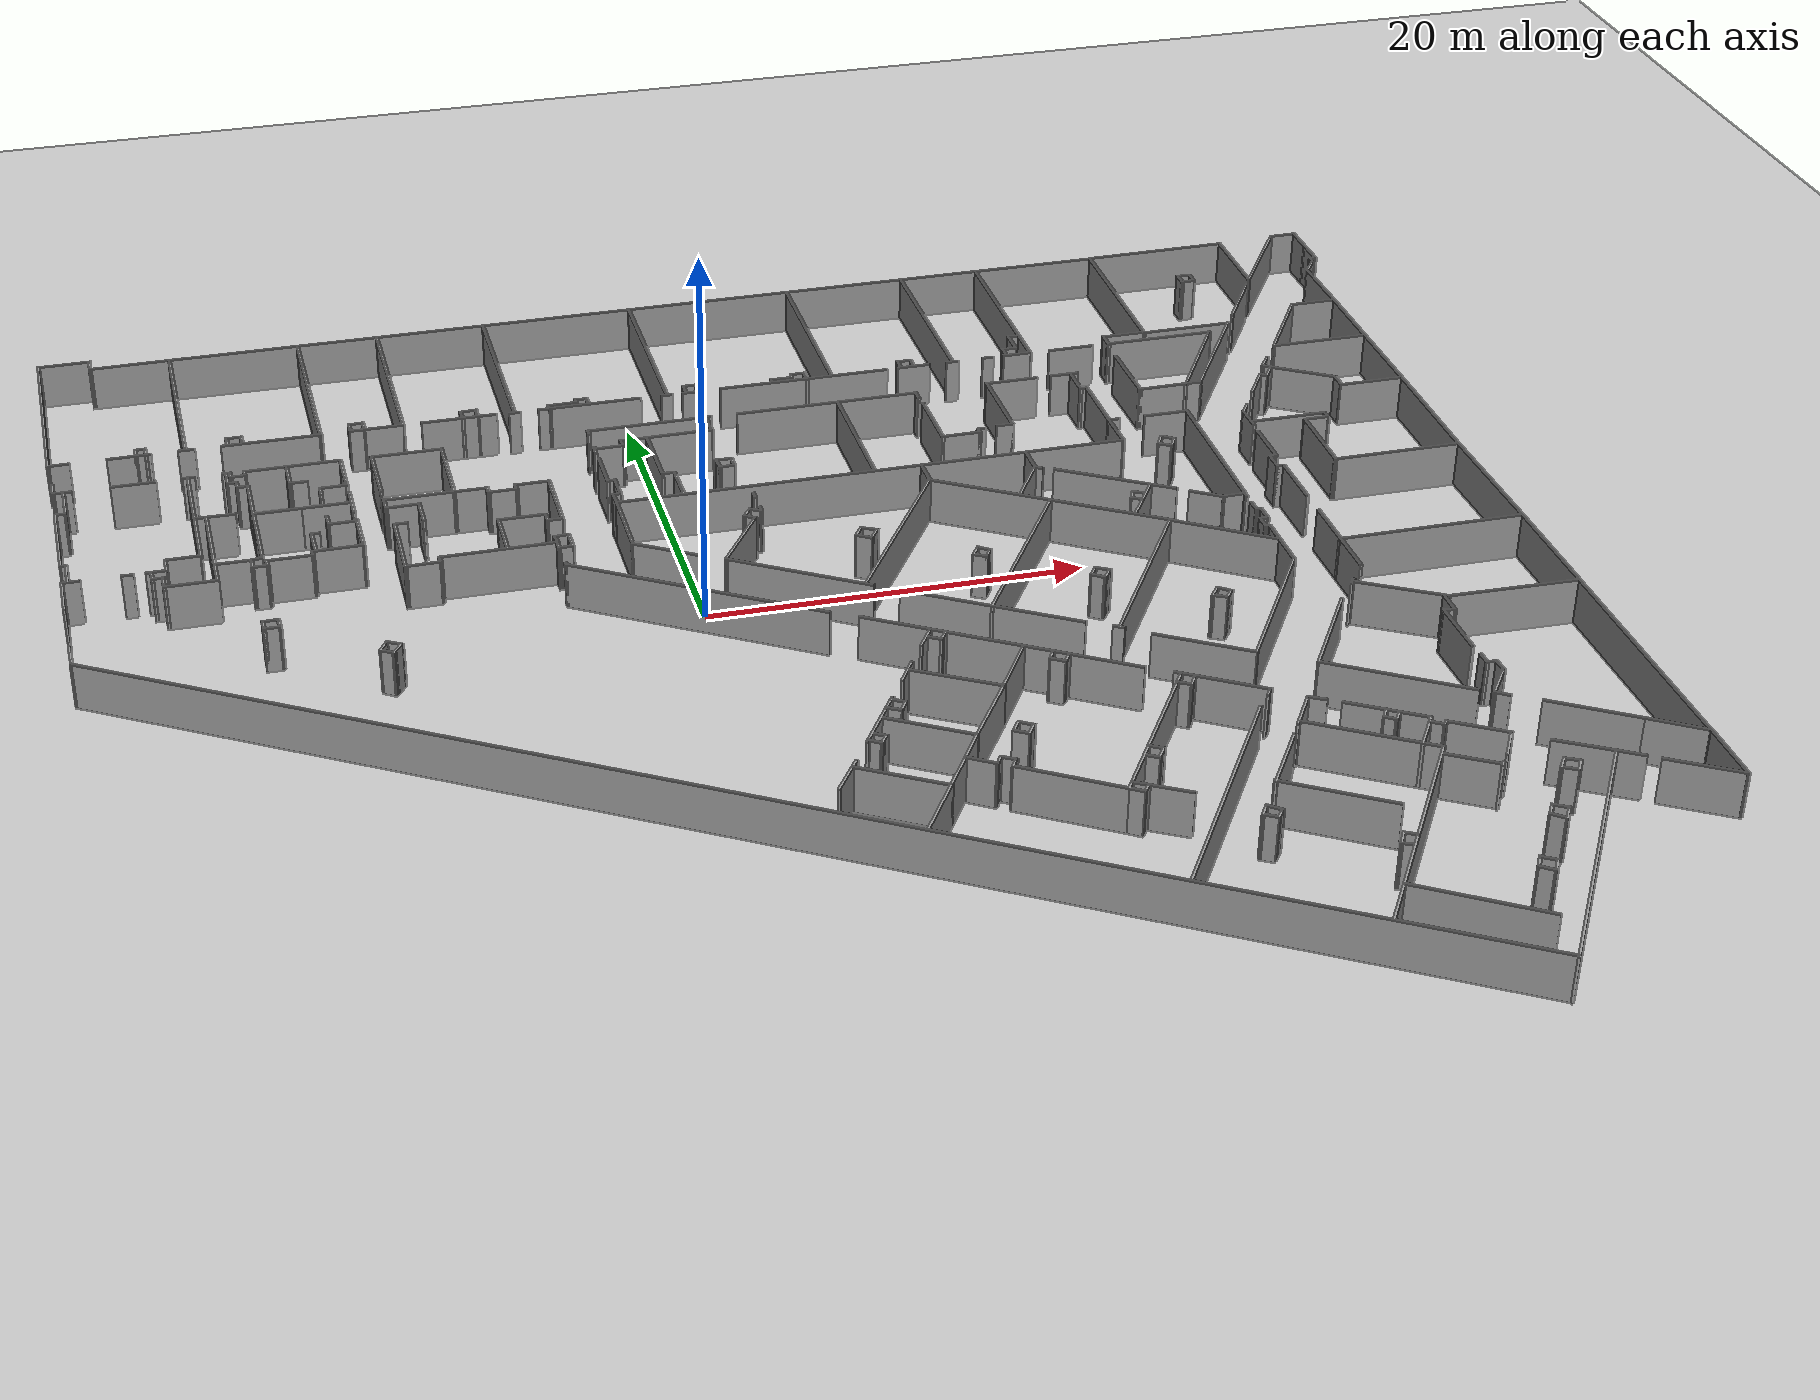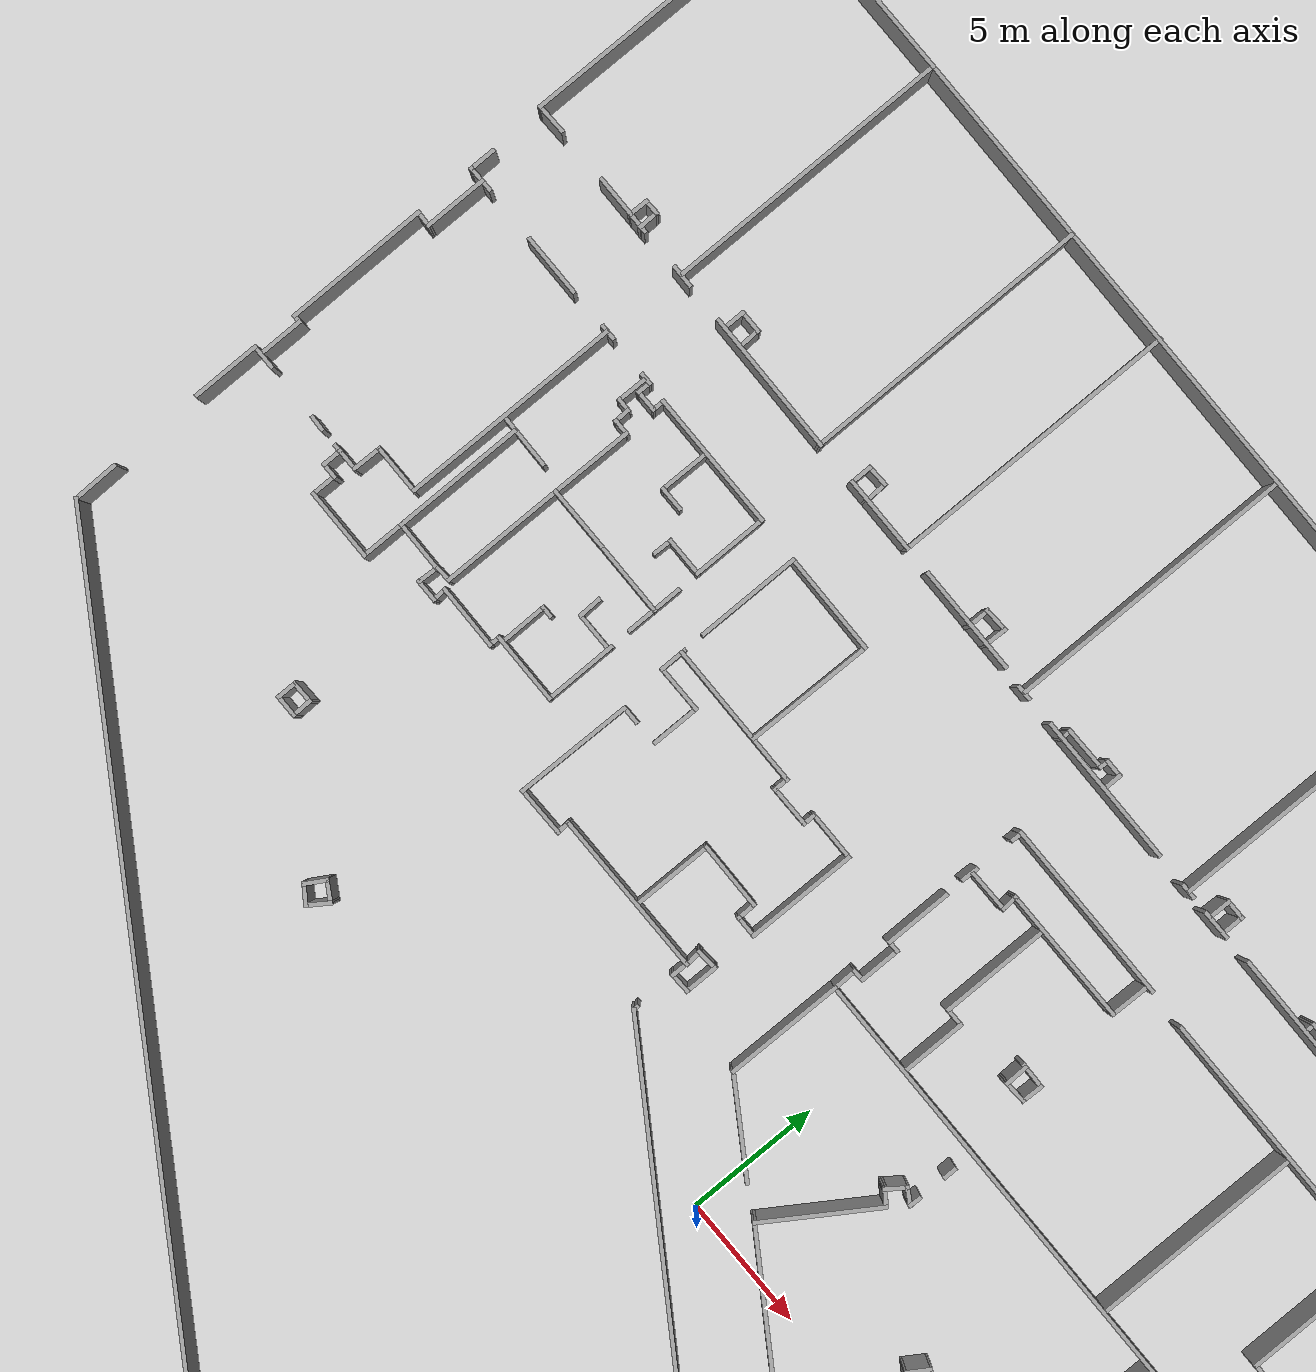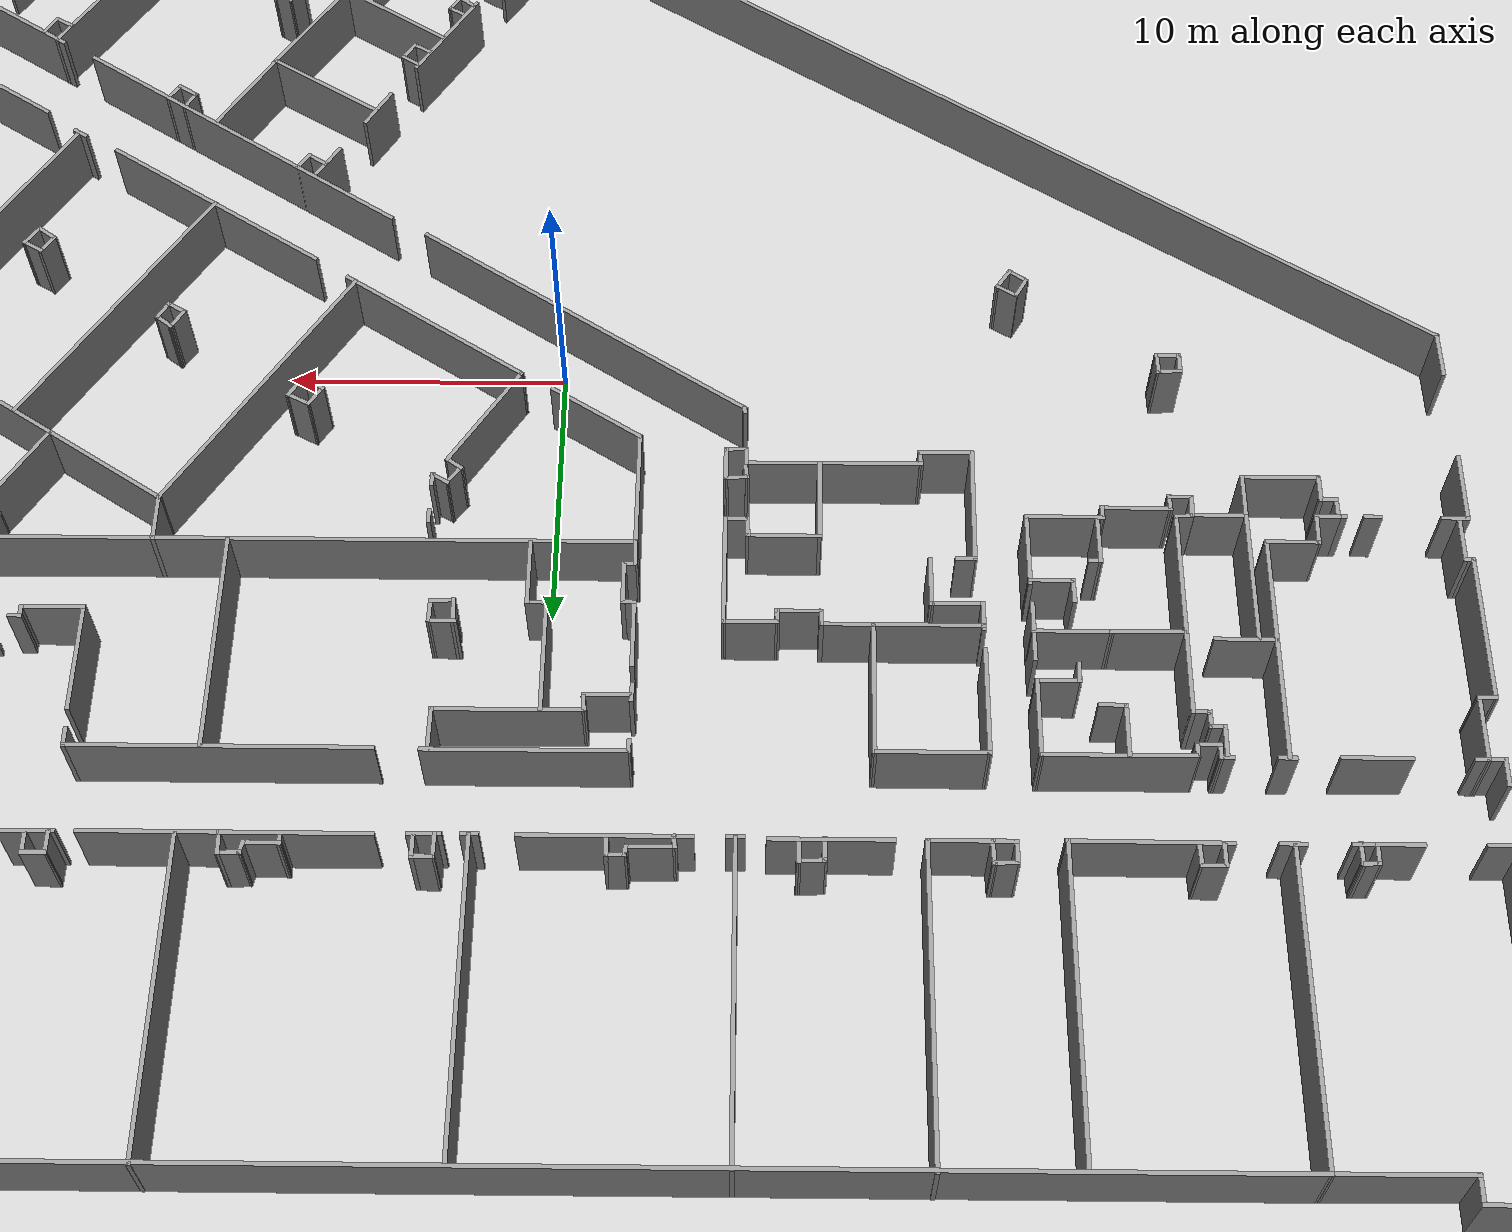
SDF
<sdf version="1.7">
 <world name="default">
  <light name="sun" type="directional">
   <pose>0 0 10 0 -0 0</pose>
   <diffuse>0.8 0.8 0.8 1</diffuse>
   <specular>0.2 0.2 0.2 1</specular>
   <attenuation>
    <range>1000</range>
    <constant>0.9</constant>
    <linear>0.01</linear>
    <quadratic>0.001</quadratic>
   </attenuation>
   <direction>-0.5 0.1 -0.9</direction>
   <spot><inner_angle>0</inner_angle><outer_angle>0</outer_angle><falloff>0</falloff></spot>
  </light>
  <model name="ground_plane">
   <static>1</static>
   <link name="link">
    <collision name="collision">
     <geometry><plane><normal>0 0 1</normal><size>100 100</size></plane></geometry>
     <surface><friction><ode><mu>100</mu><mu2>50</mu2></ode></friction></surface>
    </collision>
    <visual name="visual">
     <cast_shadows>0</cast_shadows>
     <geometry><plane><normal>0 0 1</normal><size>100 100</size></plane></geometry>
     <material>
      <script><uri>file://media/materials/scripts/gazebo.material</uri><name>Gazebo/Grey</name></script>
     </material>
    </visual>
   </link>
  </model>
  <gravity>0 0 -9.8</gravity>
  <magnetic_field>6e-06 2.3e-05 -4.2e-05</magnetic_field>
  <atmosphere type="adiabatic"/>
  <physics type="ode">
   <max_step_size>0.001</max_step_size>
   <real_time_factor>1</real_time_factor>
   <real_time_update_rate>1000</real_time_update_rate>
  </physics>
  <scene><ambient>0.4 0.4 0.4 1</ambient><background>0.7 0.7 0.7 1</background><shadows>1</shadows></scene>
  <spherical_coordinates>
   <surface_model>EARTH_WGS84</surface_model>
   <latitude_deg>0</latitude_deg>
   <longitude_deg>0</longitude_deg>
   <elevation>0</elevation>
   <heading_deg>0</heading_deg>
  </spherical_coordinates>
  <model name="HopperFloorGround_Full">
   <pose>5.96828 -4.00427 0 0 -0 0</pose>
   <link name="Wall_0">
    <collision name="Wall_0_Collision">
     <geometry><box><size>71.6402 0.15 2.5</size></box></geometry>
     <pose>0 0 1.25 0 -0 0</pose>
    </collision>
    <visual name="Wall_0_Visual">
     <pose>0 0 1.25 0 -0 0</pose>
     <geometry><box><size>71.6402 0.15 2.5</size></box></geometry>
     <material>
      <script><uri>file://media/materials/scripts/gazebo.material</uri><name>Gazebo/Grey</name></script>
      <ambient>1 1 1 1</ambient>
     </material>
     <meta><layer>0</layer></meta>
    </visual>
    <pose>-7.1575 -15.8591 0 0 -0 -0.566616</pose>
   </link>
   <link name="Wall_1">
    <collision name="Wall_1_Collision">
     <geometry><box><size>16.3063 0.15 2.5</size></box></geometry>
     <pose>0 0 1.25 0 -0 0</pose>
    </collision>
    <visual name="Wall_1_Visual">
     <pose>0 0 1.25 0 -0 0</pose>
     <geometry><box><size>16.3063 0.15 2.5</size></box></geometry>
     <material>
      <script><uri>file://media/materials/scripts/gazebo.material</uri><name>Gazebo/Grey</name></script>
      <ambient>1 1 1 1</ambient>
     </material>
     <meta><layer>0</layer></meta>
    </visual>
    <pose>27.2284 -28.2428 0 0 -0 1.02013</pose>
   </link>
   <link name="Wall_10">
    <collision name="Wall_10_Collision">
     <geometry><box><size>0.518953 0.15 2.5</size></box></geometry>
     <pose>0 0 1.25 0 -0 0</pose>
    </collision>
    <visual name="Wall_10_Visual">
     <pose>0 0 1.25 0 -0 0</pose>
     <geometry><box><size>0.518953 0.15 2.5</size></box></geometry>
     <material>
      <script><uri>file://media/materials/scripts/gazebo.material</uri><name>Gazebo/Grey</name></script>
      <ambient>1 1 1 1</ambient>
     </material>
     <meta><layer>0</layer></meta>
    </visual>
    <pose>24.1583 -16.8971 0 0 -0 1.02225</pose>
   </link>
   <link name="Wall_101">
    <collision name="Wall_101_Collision">
     <geometry><box><size>1 0.15 2.5</size></box></geometry>
     <pose>0 0 1.25 0 -0 0</pose>
    </collision>
    <visual name="Wall_101_Visual">
     <pose>0 0 1.25 0 -0 0</pose>
     <geometry><box><size>1 0.15 2.5</size></box></geometry>
     <material>
      <script><uri>file://media/materials/scripts/gazebo.material</uri><name>Gazebo/Grey</name></script>
      <ambient>1 1 1 1</ambient>
     </material>
     <meta><layer>0</layer></meta>
    </visual>
    <pose>-24.7641 18.4859 0 0 -0 3.14159</pose>
   </link>
   <link name="Wall_102">
    <collision name="Wall_102_Collision">
     <geometry><box><size>1.96918 0.15 2.5</size></box></geometry>
     <pose>0 0 1.25 0 -0 0</pose>
    </collision>
    <visual name="Wall_102_Visual">
     <pose>0 0 1.25 0 -0 0</pose>
     <geometry><box><size>1.96918 0.15 2.5</size></box></geometry>
     <material>
      <script><uri>file://media/materials/scripts/gazebo.material</uri><name>Gazebo/Grey</name></script>
      <ambient>1 1 1 1</ambient>
     </material>
     <meta><layer>0</layer></meta>
    </visual>
    <pose>-25.1838 19.3954 0 0 -0 1.56504</pose>
   </link>
   <link name="Wall_106">
    <collision name="Wall_106_Collision">
     <geometry><box><size>8.39659 0.15 2.5</size></box></geometry>
     <pose>0 0 1.25 0 -0 0</pose>
    </collision>
    <visual name="Wall_106_Visual">
     <pose>0 0 1.25 0 -0 0</pose>
     <geometry><box><size>8.39659 0.15 2.5</size></box></geometry>
     <material>
      <script><uri>file://media/materials/scripts/gazebo.material</uri><name>Gazebo/Grey</name></script>
      <ambient>1 1 1 1</ambient>
     </material>
     <meta><layer>0</layer></meta>
    </visual>
    <pose>-30.3925 16.2262 0 0 -0 1.56836</pose>
   </link>
   <link name="Wall_108">
    <collision name="Wall_108_Collision">
     <geometry><box><size>1.94011 0.15 2.5</size></box></geometry>
     <pose>0 0 1.25 0 -0 0</pose>
    </collision>
    <visual name="Wall_108_Visual">
     <pose>0 0 1.25 0 -0 0</pose>
     <geometry><box><size>1.94011 0.15 2.5</size></box></geometry>
     <material>
      <script><uri>file://media/materials/scripts/gazebo.material</uri><name>Gazebo/Grey</name></script>
      <ambient>1 1 1 1</ambient>
     </material>
     <meta><layer>0</layer></meta>
    </visual>
    <pose>-31.2976 12.103 0 0 -0 3.14159</pose>
   </link>
   <link name="Wall_109">
    <collision name="Wall_109_Collision">
     <geometry><box><size>1.1961 0.15 2.5</size></box></geometry>
     <pose>0 0 1.25 0 -0 0</pose>
    </collision>
    <visual name="Wall_109_Visual">
     <pose>0 0 1.25 0 -0 0</pose>
     <geometry><box><size>1.1961 0.15 2.5</size></box></geometry>
     <material>
      <script><uri>file://media/materials/scripts/gazebo.material</uri><name>Gazebo/Grey</name></script>
      <ambient>1 1 1 1</ambient>
     </material>
     <meta><layer>0</layer></meta>
    </visual>
    <pose>-32.2027 11.58 0 0 -0 -1.59003</pose>
   </link>
   <link name="Wall_110">
    <collision name="Wall_110_Collision">
     <geometry><box><size>0.914316 0.15 2.5</size></box></geometry>
     <pose>0 0 1.25 0 -0 0</pose>
    </collision>
    <visual name="Wall_110_Visual">
     <pose>0 0 1.25 0 -0 0</pose>
     <geometry><box><size>0.914316 0.15 2.5</size></box></geometry>
     <material>
      <script><uri>file://media/materials/scripts/gazebo.material</uri><name>Gazebo/Grey</name></script>
      <ambient>1 1 1 1</ambient>
     </material>
     <meta><layer>0</layer></meta>
    </visual>
    <pose>-32.5949 11.0571 0 0 -0 3.14159</pose>
   </link>
   <link name="Wall_112">
    <collision name="Wall_112_Collision">
     <geometry><box><size>0.75 0.15 2.5</size></box></geometry>
     <pose>0 0 1.25 0 -0 0</pose>
    </collision>
    <visual name="Wall_112_Visual">
     <pose>0 0 1.25 0 -0 0</pose>
     <geometry><box><size>0.75 0.15 2.5</size></box></geometry>
     <material>
      <script><uri>file://media/materials/scripts/gazebo.material</uri><name>Gazebo/Grey</name></script>
      <ambient>1 1 1 1</ambient>
     </material>
     <meta><layer>0</layer></meta>
    </visual>
    <pose>-20.122 12.8829 0 0 -0 3.14159</pose>
   </link>
   <link name="Wall_113">
    <collision name="Wall_113_Collision">
     <geometry><box><size>4.49402 0.15 2.5</size></box></geometry>
     <pose>0 0 1.25 0 -0 0</pose>
    </collision>
    <visual name="Wall_113_Visual">
     <pose>0 0 1.25 0 -0 0</pose>
     <geometry><box><size>4.49402 0.15 2.5</size></box></geometry>
     <material>
      <script><uri>file://media/materials/scripts/gazebo.material</uri><name>Gazebo/Grey</name></script>
      <ambient>1 1 1 1</ambient>
     </material>
     <meta><layer>0</layer></meta>
    </visual>
    <pose>-20.4432 10.711 0 0 -0 -1.58056</pose>
   </link>
   <link name="Wall_114">
    <collision name="Wall_114_Collision">
     <geometry><box><size>1.95508 0.15 2.5</size></box></geometry>
     <pose>0 0 1.25 0 -0 0</pose>
    </collision>
    <visual name="Wall_114_Visual">
     <pose>0 0 1.25 0 -0 0</pose>
     <geometry><box><size>1.95508 0.15 2.5</size></box></geometry>
     <material>
      <script><uri>file://media/materials/scripts/gazebo.material</uri><name>Gazebo/Grey</name></script>
      <ambient>1 1 1 1</ambient>
     </material>
     <meta><layer>0</layer></meta>
    </visual>
    <pose>-19.562 8.5544 0 0 -0 0.016948</pose>
   </link>
   <link name="Wall_115">
    <collision name="Wall_115_Collision">
     <geometry><box><size>0.609872 0.15 2.5</size></box></geometry>
     <pose>0 0 1.25 0 -0 0</pose>
    </collision>
    <visual name="Wall_115_Visual">
     <pose>0 0 1.25 0 -0 0</pose>
     <geometry><box><size>0.609872 0.15 2.5</size></box></geometry>
     <material>
      <script><uri>file://media/materials/scripts/gazebo.material</uri><name>Gazebo/Grey</name></script>
      <ambient>1 1 1 1</ambient>
     </material>
     <meta><layer>0</layer></meta>
    </visual>
    <pose>-18.6749 8.79912 0 0 -0 1.63736</pose>
   </link>
   <link name="Wall_116">
    <collision name="Wall_116_Collision">
     <geometry><box><size>6.23753 0.15 2.5</size></box></geometry>
     <pose>0 0 1.25 0 -0 0</pose>
    </collision>
    <visual name="Wall_116_Visual">
     <pose>0 0 1.25 0 -0 0</pose>
     <geometry><box><size>6.23753 0.15 2.5</size></box></geometry>
     <material>
      <script><uri>file://media/materials/scripts/gazebo.material</uri><name>Gazebo/Grey</name></script>
      <ambient>1 1 1 1</ambient>
     </material>
     <meta><layer>0</layer></meta>
    </visual>
    <pose>-15.6464 9.04384 0 0 -0 0.005025</pose>
   </link>
   <link name="Wall_117">
    <collision name="Wall_117_Collision">
     <geometry><box><size>0.731214 0.15 2.5</size></box></geometry>
     <pose>0 0 1.25 0 -0 0</pose>
    </collision>
    <visual name="Wall_117_Visual">
     <pose>0 0 1.25 0 -0 0</pose>
     <geometry><box><size>0.731214 0.15 2.5</size></box></geometry>
     <material>
      <script><uri>file://media/materials/scripts/gazebo.material</uri><name>Gazebo/Grey</name></script>
      <ambient>1 1 1 1</ambient>
     </material>
     <meta><layer>0</layer></meta>
    </visual>
    <pose>-12.6027 8.76853 0 0 -0 -1.5708</pose>
   </link>
   <link name="Wall_118">
    <collision name="Wall_118_Collision">
     <geometry><box><size>0.85424 0.15 2.5</size></box></geometry>
     <pose>0 0 1.25 0 -0 0</pose>
    </collision>
    <visual name="Wall_118_Visual">
     <pose>0 0 1.25 0 -0 0</pose>
     <geometry><box><size>0.85424 0.15 2.5</size></box></geometry>
     <material>
      <script><uri>file://media/materials/scripts/gazebo.material</uri><name>Gazebo/Grey</name></script>
      <ambient>1 1 1 1</ambient>
     </material>
     <meta><layer>0</layer></meta>
    </visual>
    <pose>-12.2509 8.49322 0 0 -0 0.043451</pose>
   </link>
   <link name="Wall_119">
    <collision name="Wall_119_Collision">
     <geometry><box><size>1.34302 0.15 2.5</size></box></geometry>
     <pose>0 0 1.25 0 -0 0</pose>
    </collision>
    <visual name="Wall_119_Visual">
     <pose>0 0 1.25 0 -0 0</pose>
     <geometry><box><size>1.34302 0.15 2.5</size></box></geometry>
     <material>
      <script><uri>file://media/materials/scripts/gazebo.material</uri><name>Gazebo/Grey</name></script>
      <ambient>1 1 1 1</ambient>
     </material>
     <meta><layer>0</layer></meta>
    </visual>
    <pose>-11.8991 9.10502 0 0 -0 1.5708</pose>
   </link>
   <link name="Wall_12">
    <collision name="Wall_12_Collision">
     <geometry><box><size>4.26067 0.15 2.5</size></box></geometry>
     <pose>0 0 1.25 0 -0 0</pose>
    </collision>
    <visual name="Wall_12_Visual">
     <pose>0 0 1.25 0 -0 0</pose>
     <geometry><box><size>4.26067 0.15 2.5</size></box></geometry>
     <material>
      <script><uri>file://media/materials/scripts/gazebo.material</uri><name>Gazebo/Grey</name></script>
      <ambient>1 1 1 1</ambient>
     </material>
     <meta><layer>0</layer></meta>
    </visual>
    <pose>22.5135 -15.6473 0 0 -0 2.58124</pose>
   </link>
   <link name="Wall_120">
    <collision name="Wall_120_Collision">
     <geometry><box><size>0.88671 0.15 2.5</size></box></geometry>
     <pose>0 0 1.25 0 -0 0</pose>
    </collision>
    <visual name="Wall_120_Visual">
     <pose>0 0 1.25 0 -0 0</pose>
     <geometry><box><size>0.88671 0.15 2.5</size></box></geometry>
     <material>
      <script><uri>file://media/materials/scripts/gazebo.material</uri><name>Gazebo/Grey</name></script>
      <ambient>1 1 1 1</ambient>
     </material>
     <meta><layer>0</layer></meta>
    </visual>
    <pose>-12.2662 9.67094 0 0 -0 -3.05845</pose>
   </link>
   <link name="Wall_121">
    <collision name="Wall_121_Collision">
     <geometry><box><size>0.704013 0.15 2.5</size></box></geometry>
     <pose>0 0 1.25 0 -0 0</pose>
    </collision>
    <visual name="Wall_121_Visual">
     <pose>0 0 1.25 0 -0 0</pose>
     <geometry><box><size>0.704013 0.15 2.5</size></box></geometry>
     <material>
      <script><uri>file://media/materials/scripts/gazebo.material</uri><name>Gazebo/Grey</name></script>
      <ambient>1 1 1 1</ambient>
     </material>
     <meta><layer>0</layer></meta>
    </visual>
    <pose>-12.6027 9.36504 0 0 -0 -1.46014</pose>
   </link>
   <link name="Wall_123">
    <collision name="Wall_123_Collision">
     <geometry><box><size>2.25 0.15 2.5</size></box></geometry>
     <pose>0 0 1.25 0 -0 0</pose>
    </collision>
    <visual name="Wall_123_Visual">
     <pose>0 0 1.25 0 -0 0</pose>
     <geometry><box><size>2.25 0.15 2.5</size></box></geometry>
     <material>
      <script><uri>file://media/materials/scripts/gazebo.material</uri><name>Gazebo/Grey</name></script>
      <ambient>1 1 1 1</ambient>
     </material>
     <meta><layer>0</layer></meta>
    </visual>
    <pose>-22.29 15.6966 0 0 -0 -1.5708</pose>
   </link>
   <link name="Wall_125">
    <collision name="Wall_125_Collision">
     <geometry><box><size>2.75 0.15 2.5</size></box></geometry>
     <pose>0 0 1.25 0 -0 0</pose>
    </collision>
    <visual name="Wall_125_Visual">
     <pose>0 0 1.25 0 -0 0</pose>
     <geometry><box><size>2.75 0.15 2.5</size></box></geometry>
     <material>
      <script><uri>file://media/materials/scripts/gazebo.material</uri><name>Gazebo/Grey</name></script>
      <ambient>1 1 1 1</ambient>
     </material>
     <meta><layer>0</layer></meta>
    </visual>
    <pose>-23.59 15.7001 0 0 -0 3.14159</pose>
   </link>
   <link name="Wall_126">
    <collision name="Wall_126_Collision">
     <geometry><box><size>2.64453 0.15 2.5</size></box></geometry>
     <pose>0 0 1.25 0 -0 0</pose>
    </collision>
    <visual name="Wall_126_Visual">
     <pose>0 0 1.25 0 -0 0</pose>
     <geometry><box><size>2.64453 0.15 2.5</size></box></geometry>
     <material>
      <script><uri>file://media/materials/scripts/gazebo.material</uri><name>Gazebo/Grey</name></script>
      <ambient>1 1 1 1</ambient>
     </material>
     <meta><layer>0</layer></meta>
    </visual>
    <pose>-26.1372 15.6944 0 0 -0 -3.13698</pose>
   </link>
   <link name="Wall_127">
    <collision name="Wall_127_Collision">
     <geometry><box><size>3.17459 0.15 2.5</size></box></geometry>
     <pose>0 0 1.25 0 -0 0</pose>
    </collision>
    <visual name="Wall_127_Visual">
     <pose>0 0 1.25 0 -0 0</pose>
     <geometry><box><size>3.17459 0.15 2.5</size></box></geometry>
     <material>
      <script><uri>file://media/materials/scripts/gazebo.material</uri><name>Gazebo/Grey</name></script>
      <ambient>1 1 1 1</ambient>
     </material>
     <meta><layer>0</layer></meta>
    </visual>
    <pose>-27.3787 17.2009 0 0 -0 1.56699</pose>
   </link>
   <link name="Wall_129">
    <collision name="Wall_129_Collision">
     <geometry><box><size>0.692389 0.15 2.5</size></box></geometry>
     <pose>0 0 1.25 0 -0 0</pose>
    </collision>
    <visual name="Wall_129_Visual">
     <pose>0 0 1.25 0 -0 0</pose>
     <geometry><box><size>0.692389 0.15 2.5</size></box></geometry>
     <material>
      <script><uri>file://media/materials/scripts/gazebo.material</uri><name>Gazebo/Grey</name></script>
      <ambient>1 1 1 1</ambient>
     </material>
     <meta><layer>0</layer></meta>
    </visual>
    <pose>-27.6442 18.7138 0 0 -0 3.13898</pose>
   </link>
   <link name="Wall_130">
    <collision name="Wall_130_Collision">
     <geometry><box><size>0.679125 0.15 2.5</size></box></geometry>
     <pose>0 0 1.25 0 -0 0</pose>
    </collision>
    <visual name="Wall_130_Visual">
     <pose>0 0 1.25 0 -0 0</pose>
     <geometry><box><size>0.679125 0.15 2.5</size></box></geometry>
     <material>
      <script><uri>file://media/materials/scripts/gazebo.material</uri><name>Gazebo/Grey</name></script>
      <ambient>1 1 1 1</ambient>
     </material>
     <meta><layer>0</layer></meta>
    </visual>
    <pose>-27.9211 18.979 0 0 -0 1.59253</pose>
   </link>
   <link name="Wall_131">
    <collision name="Wall_131_Collision">
     <geometry><box><size>0.598647 0.15 2.5</size></box></geometry>
     <pose>0 0 1.25 0 -0 0</pose>
    </collision>
    <visual name="Wall_131_Visual">
     <pose>0 0 1.25 0 -0 0</pose>
     <geometry><box><size>0.598647 0.15 2.5</size></box></geometry>
     <material>
      <script><uri>file://media/materials/scripts/gazebo.material</uri><name>Gazebo/Grey</name></script>
      <ambient>1 1 1 1</ambient>
     </material>
     <meta><layer>0</layer></meta>
    </visual>
    <pose>-28.1511 19.2493 0 0 -0 3.11596</pose>
   </link>
   <link name="Wall_132">
    <collision name="Wall_132_Collision">
     <geometry><box><size>1.17356 0.15 2.5</size></box></geometry>
     <pose>0 0 1.25 0 -0 0</pose>
    </collision>
    <visual name="Wall_132_Visual">
     <pose>0 0 1.25 0 -0 0</pose>
     <geometry><box><size>1.17356 0.15 2.5</size></box></geometry>
     <material>
      <script><uri>file://media/materials/scripts/gazebo.material</uri><name>Gazebo/Grey</name></script>
      <ambient>1 1 1 1</ambient>
     </material>
     <meta><layer>0</layer></meta>
    </visual>
    <pose>-28.3696 19.7668 0 0 -0 1.55956</pose>
   </link>
   <link name="Wall_134">
    <collision name="Wall_134_Collision">
     <geometry><box><size>2.16263 0.15 2.5</size></box></geometry>
     <pose>0 0 1.25 0 -0 0</pose>
    </collision>
    <visual name="Wall_134_Visual">
     <pose>0 0 1.25 0 -0 0</pose>
     <geometry><box><size>2.16263 0.15 2.5</size></box></geometry>
     <material>
      <script><uri>file://media/materials/scripts/gazebo.material</uri><name>Gazebo/Grey</name></script>
      <ambient>1 1 1 1</ambient>
     </material>
     <meta><layer>0</layer></meta>
    </visual>
    <pose>-29.3586 15.9545 0 0 -0 3.13016</pose>
   </link>
   <link name="Wall_137">
    <collision name="Wall_137_Collision">
     <geometry><box><size>5 0.15 2.5</size></box></geometry>
     <pose>0 0 1.25 0 -0 0</pose>
    </collision>
    <visual name="Wall_137_Visual">
     <pose>0 0 1.25 0 -0 0</pose>
     <geometry><box><size>5 0.15 2.5</size></box></geometry>
     <material>
      <script><uri>file://media/materials/scripts/gazebo.material</uri><name>Gazebo/Grey</name></script>
      <ambient>1 1 1 1</ambient>
     </material>
     <meta><layer>0</layer></meta>
    </visual>
    <pose>-29.7968 13.4907 0 0 -0 1.5708</pose>
   </link>
   <link name="Wall_139">
    <collision name="Wall_139_Collision">
     <geometry><box><size>4.73481 0.15 2.5</size></box></geometry>
     <pose>0 0 1.25 0 -0 0</pose>
    </collision>
    <visual name="Wall_139_Visual">
     <pose>0 0 1.25 0 -0 0</pose>
     <geometry><box><size>4.73481 0.15 2.5</size></box></geometry>
     <material>
      <script><uri>file://media/materials/scripts/gazebo.material</uri><name>Gazebo/Grey</name></script>
      <ambient>1 1 1 1</ambient>
     </material>
     <meta><layer>0</layer></meta>
    </visual>
    <pose>-27.3873 13.3962 0 0 -0 -1.57203</pose>
   </link>
   <link name="Wall_14">
    <collision name="Wall_14_Collision">
     <geometry><box><size>1.0029 0.15 2.5</size></box></geometry>
     <pose>0 0 1.25 0 -0 0</pose>
    </collision>
    <visual name="Wall_14_Visual">
     <pose>0 0 1.25 0 -0 0</pose>
     <geometry><box><size>1.0029 0.15 2.5</size></box></geometry>
     <material>
      <script><uri>file://media/materials/scripts/gazebo.material</uri><name>Gazebo/Grey</name></script>
      <ambient>1 1 1 1</ambient>
     </material>
     <meta><layer>0</layer></meta>
    </visual>
    <pose>19.6794 -13.9165 0 0 -0 2.65043</pose>
   </link>
   <link name="Wall_140">
    <collision name="Wall_140_Collision">
     <geometry><box><size>0.679661 0.15 2.5</size></box></geometry>
     <pose>0 0 1.25 0 -0 0</pose>
    </collision>
    <visual name="Wall_140_Visual">
     <pose>0 0 1.25 0 -0 0</pose>
     <geometry><box><size>0.679661 0.15 2.5</size></box></geometry>
     <material>
      <script><uri>file://media/materials/scripts/gazebo.material</uri><name>Gazebo/Grey</name></script>
      <ambient>1 1 1 1</ambient>
     </material>
     <meta><layer>0</layer></meta>
    </visual>
    <pose>-27.6546 11.0906 0 0 -0 -3.09163</pose>
   </link>
   <link name="Wall_142">
    <collision name="Wall_142_Collision">
     <geometry><box><size>4 0.15 2.5</size></box></geometry>
     <pose>0 0 1.25 0 -0 0</pose>
    </collision>
    <visual name="Wall_142_Visual">
     <pose>0 0 1.25 0 -0 0</pose>
     <geometry><box><size>4 0.15 2.5</size></box></geometry>
     <material>
      <script><uri>file://media/materials/scripts/gazebo.material</uri><name>Gazebo/Grey</name></script>
      <ambient>1 1 1 1</ambient>
     </material>
     <meta><layer>0</layer></meta>
    </visual>
    <pose>-20.6382 18.3734 0 0 -0 1.5708</pose>
   </link>
   <link name="Wall_143">
    <collision name="Wall_143_Collision">
     <geometry><box><size>3.9067 0.15 2.5</size></box></geometry>
     <pose>0 0 1.25 0 -0 0</pose>
    </collision>
    <visual name="Wall_143_Visual">
     <pose>0 0 1.25 0 -0 0</pose>
     <geometry><box><size>3.9067 0.15 2.5</size></box></geometry>
     <material>
      <script><uri>file://media/materials/scripts/gazebo.material</uri><name>Gazebo/Grey</name></script>
      <ambient>1 1 1 1</ambient>
     </material>
     <meta><layer>0</layer></meta>
    </visual>
    <pose>-18.7599 20.2897 0 0 -0 -0.004631</pose>
   </link>
   <link name="Wall_144">
    <collision name="Wall_144_Collision">
     <geometry><box><size>4.92593 0.15 2.5</size></box></geometry>
     <pose>0 0 1.25 0 -0 0</pose>
    </collision>
    <visual name="Wall_144_Visual">
     <pose>0 0 1.25 0 -0 0</pose>
     <geometry><box><size>4.92593 0.15 2.5</size></box></geometry>
     <material>
      <script><uri>file://media/materials/scripts/gazebo.material</uri><name>Gazebo/Grey</name></script>
      <ambient>1 1 1 1</ambient>
     </material>
     <meta><layer>0</layer></meta>
    </visual>
    <pose>-16.9045 17.8932 0 0 -0 -1.58035</pose>
   </link>
   <link name="Wall_145">
    <collision name="Wall_145_Collision">
     <geometry><box><size>1.89901 0.15 2.5</size></box></geometry>
     <pose>0 0 1.25 0 -0 0</pose>
    </collision>
    <visual name="Wall_145_Visual">
     <pose>0 0 1.25 0 -0 0</pose>
     <geometry><box><size>1.89901 0.15 2.5</size></box></geometry>
     <material>
      <script><uri>file://media/materials/scripts/gazebo.material</uri><name>Gazebo/Grey</name></script>
      <ambient>1 1 1 1</ambient>
     </material>
     <meta><layer>0</layer></meta>
    </visual>
    <pose>-16.0528 15.5054 0 0 -0 0</pose>
   </link>
   <link name="Wall_147">
    <collision name="Wall_147_Collision">
     <geometry><box><size>0.25 0.15 2.5</size></box></geometry>
     <pose>0 0 1.25 0 -0 0</pose>
    </collision>
    <visual name="Wall_147_Visual">
     <pose>0 0 1.25 0 -0 0</pose>
     <geometry><box><size>0.25 0.15 2.5</size></box></geometry>
     <material>
      <script><uri>file://media/materials/scripts/gazebo.material</uri><name>Gazebo/Grey</name></script>
      <ambient>1 1 1 1</ambient>
     </material>
     <meta><layer>0</layer></meta>
    </visual>
    <pose>-20.623 15.5619 0 0 -0 -1.5708</pose>
   </link>
   <link name="Wall_148">
    <collision name="Wall_148_Collision">
     <geometry><box><size>3.84573 0.15 2.5</size></box></geometry>
     <pose>0 0 1.25 0 -0 0</pose>
    </collision>
    <visual name="Wall_148_Visual">
     <pose>0 0 1.25 0 -0 0</pose>
     <geometry><box><size>3.84573 0.15 2.5</size></box></geometry>
     <material>
      <script><uri>file://media/materials/scripts/gazebo.material</uri><name>Gazebo/Grey</name></script>
      <ambient>1 1 1 1</ambient>
     </material>
     <meta><layer>0</layer></meta>
    </visual>
    <pose>-18.7751 15.5087 0 0 -0 -0.001748</pose>
   </link>
   <link name="Wall_15">
    <collision name="Wall_15_Collision">
     <geometry><box><size>2.53238 0.15 2.5</size></box></geometry>
     <pose>0 0 1.25 0 -0 0</pose>
    </collision>
    <visual name="Wall_15_Visual">
     <pose>0 0 1.25 0 -0 0</pose>
     <geometry><box><size>2.53238 0.15 2.5</size></box></geometry>
     <material>
      <script><uri>file://media/materials/scripts/gazebo.material</uri><name>Gazebo/Grey</name></script>
      <ambient>1 1 1 1</ambient>
     </material>
     <meta><layer>0</layer></meta>
    </visual>
    <pose>18.665 -14.7211 0 0 -0 -2.1364</pose>
   </link>
   <link name="Wall_150">
    <collision name="Wall_150_Collision">
     <geometry><box><size>1 0.15 2.5</size></box></geometry>
     <pose>0 0 1.25 0 -0 0</pose>
    </collision>
    <visual name="Wall_150_Visual">
     <pose>0 0 1.25 0 -0 0</pose>
     <geometry><box><size>1 0.15 2.5</size></box></geometry>
     <material>
      <script><uri>file://media/materials/scripts/gazebo.material</uri><name>Gazebo/Grey</name></script>
      <ambient>1 1 1 1</ambient>
     </material>
     <meta><layer>0</layer></meta>
    </visual>
    <pose>-20.623 15.0869 0 0 -0 -1.5708</pose>
   </link>
   <link name="Wall_152">
    <collision name="Wall_152_Collision">
     <geometry><box><size>0.651889 0.15 2.5</size></box></geometry>
     <pose>0 0 1.25 0 -0 0</pose>
    </collision>
    <visual name="Wall_152_Visual">
     <pose>0 0 1.25 0 -0 0</pose>
     <geometry><box><size>0.651889 0.15 2.5</size></box></geometry>
     <material>
      <script><uri>file://media/materials/scripts/gazebo.material</uri><name>Gazebo/Grey</name></script>
      <ambient>1 1 1 1</ambient>
     </material>
     <meta><layer>0</layer></meta>
    </visual>
    <pose>-15.1783 15.2545 0 0 -0 -1.5708</pose>
   </link>
   <link name="Wall_153">
    <collision name="Wall_153_Collision">
     <geometry><box><size>1.64054 0.15 2.5</size></box></geometry>
     <pose>0 0 1.25 0 -0 0</pose>
    </collision>
    <visual name="Wall_153_Visual">
     <pose>0 0 1.25 0 -0 0</pose>
     <geometry><box><size>1.64054 0.15 2.5</size></box></geometry>
     <material>
      <script><uri>file://media/materials/scripts/gazebo.material</uri><name>Gazebo/Grey</name></script>
      <ambient>1 1 1 1</ambient>
     </material>
     <meta><layer>0</layer></meta>
    </visual>
    <pose>-14.433 15.0112 0 0 -0 0.010204</pose>
   </link>
   <link name="Wall_154">
    <collision name="Wall_154_Collision">
     <geometry><box><size>0.576116 0.15 2.5</size></box></geometry>
     <pose>0 0 1.25 0 -0 0</pose>
    </collision>
    <visual name="Wall_154_Visual">
     <pose>0 0 1.25 0 -0 0</pose>
     <geometry><box><size>0.576116 0.15 2.5</size></box></geometry>
     <material>
      <script><uri>file://media/materials/scripts/gazebo.material</uri><name>Gazebo/Grey</name></script>
      <ambient>1 1 1 1</ambient>
     </material>
     <meta><layer>0</layer></meta>
    </visual>
    <pose>-13.6954 15.2317 0 0 -0 1.6065</pose>
   </link>
   <link name="Wall_155">
    <collision name="Wall_155_Collision">
     <geometry><box><size>1.95991 0.15 2.5</size></box></geometry>
     <pose>0 0 1.25 0 -0 0</pose>
    </collision>
    <visual name="Wall_155_Visual">
     <pose>0 0 1.25 0 -0 0</pose>
     <geometry><box><size>1.95991 0.15 2.5</size></box></geometry>
     <material>
      <script><uri>file://media/materials/scripts/gazebo.material</uri><name>Gazebo/Grey</name></script>
      <ambient>1 1 1 1</ambient>
     </material>
     <meta><layer>0</layer></meta>
    </visual>
    <pose>-12.7981 15.4446 0 0 -0 0</pose>
   </link>
   <link name="Wall_156">
    <collision name="Wall_156_Collision">
     <geometry><box><size>4.22595 0.15 2.5</size></box></geometry>
     <pose>0 0 1.25 0 -0 0</pose>
    </collision>
    <visual name="Wall_156_Visual">
     <pose>0 0 1.25 0 -0 0</pose>
     <geometry><box><size>4.22595 0.15 2.5</size></box></geometry>
     <material>
      <script><uri>file://media/materials/scripts/gazebo.material</uri><name>Gazebo/Grey</name></script>
      <ambient>1 1 1 1</ambient>
     </material>
     <meta><layer>0</layer></meta>
    </visual>
    <pose>-11.9008 13.4066 0 0 -0 -1.57453</pose>
   </link>
   <link name="Wall_157">
    <collision name="Wall_157_Collision">
     <geometry><box><size>0.910437 0.15 2.5</size></box></geometry>
     <pose>0 0 1.25 0 -0 0</pose>
    </collision>
    <visual name="Wall_157_Visual">
     <pose>0 0 1.25 0 -0 0</pose>
     <geometry><box><size>0.910437 0.15 2.5</size></box></geometry>
     <material>
      <script><uri>file://media/materials/scripts/gazebo.material</uri><name>Gazebo/Grey</name></script>
      <ambient>1 1 1 1</ambient>
     </material>
     <meta><layer>0</layer></meta>
    </visual>
    <pose>-12.2886 11.3687 0 0 -0 3.14159</pose>
   </link>
   <link name="Wall_158">
    <collision name="Wall_158_Collision">
     <geometry><box><size>0.804683 0.15 2.5</size></box></geometry>
     <pose>0 0 1.25 0 -0 0</pose>
    </collision>
    <visual name="Wall_158_Visual">
     <pose>0 0 1.25 0 -0 0</pose>
     <geometry><box><size>0.804683 0.15 2.5</size></box></geometry>
     <material>
      <script><uri>file://media/materials/scripts/gazebo.material</uri><name>Gazebo/Grey</name></script>
      <ambient>1 1 1 1</ambient>
     </material>
     <meta><layer>0</layer></meta>
    </visual>
    <pose>-12.6764 11.6956 0 0 -0 1.59405</pose>
   </link>
   <link name="Wall_159">
    <collision name="Wall_159_Collision">
     <geometry><box><size>2.61386 0.15 2.5</size></box></geometry>
     <pose>0 0 1.25 0 -0 0</pose>
    </collision>
    <visual name="Wall_159_Visual">
     <pose>0 0 1.25 0 -0 0</pose>
     <geometry><box><size>2.61386 0.15 2.5</size></box></geometry>
     <material>
      <script><uri>file://media/materials/scripts/gazebo.material</uri><name>Gazebo/Grey</name></script>
      <ambient>1 1 1 1</ambient>
     </material>
     <meta><layer>0</layer></meta>
    </visual>
    <pose>-13.916 12.0302 0 0 -0 3.13542</pose>
   </link>
   <link name="Wall_161">
    <collision name="Wall_161_Collision">
     <geometry><box><size>3.11574 0.15 2.5</size></box></geometry>
     <pose>0 0 1.25 0 -0 0</pose>
    </collision>
    <visual name="Wall_161_Visual">
     <pose>0 0 1.25 0 -0 0</pose>
     <geometry><box><size>3.11574 0.15 2.5</size></box></geometry>
     <material>
      <script><uri>file://media/materials/scripts/gazebo.material</uri><name>Gazebo/Grey</name></script>
      <ambient>1 1 1 1</ambient>
     </material>
     <meta><layer>0</layer></meta>
    </visual>
    <pose>-15.1555 10.555 0 0 -0 -1.57593</pose>
   </link>
   <link name="Wall_163">
    <collision name="Wall_163_Collision">
     <geometry><box><size>0.293821 0.15 2.5</size></box></geometry>
     <pose>0 0 1.25 0 -0 0</pose>
    </collision>
    <visual name="Wall_163_Visual">
     <pose>0 0 1.25 0 -0 0</pose>
     <geometry><box><size>0.293821 0.15 2.5</size></box></geometry>
     <material>
      <script><uri>file://media/materials/scripts/gazebo.material</uri><name>Gazebo/Grey</name></script>
      <ambient>1 1 1 1</ambient>
     </material>
     <meta><layer>0</layer></meta>
    </visual>
    <pose>-12.5366 6.82613 0 0 -0 -1.42643</pose>
   </link>
   <link name="Wall_164">
    <collision name="Wall_164_Collision">
     <geometry><box><size>14.1631 0.15 2.5</size></box></geometry>
     <pose>0 0 1.25 0 -0 0</pose>
    </collision>
    <visual name="Wall_164_Visual">
     <pose>0 0 1.25 0 -0 0</pose>
     <geometry><box><size>14.1631 0.15 2.5</size></box></geometry>
     <material>
      <script><uri>file://media/materials/scripts/gazebo.material</uri><name>Gazebo/Grey</name></script>
      <ambient>1 1 1 1</ambient>
     </material>
     <meta><layer>0</layer></meta>
    </visual>
    <pose>-6.67032 2.93967 0 0 -0 -0.575834</pose>
   </link>
   <link name="Wall_166">
    <collision name="Wall_166_Collision">
     <geometry><box><size>14.443 0.15 2.5</size></box></geometry>
     <pose>0 0 1.25 0 -0 0</pose>
    </collision>
    <visual name="Wall_166_Visual">
     <pose>0 0 1.25 0 -0 0</pose>
     <geometry><box><size>14.443 0.15 2.5</size></box></geometry>
     <material>
      <script><uri>file://media/materials/scripts/gazebo.material</uri><name>Gazebo/Grey</name></script>
      <ambient>1 1 1 1</ambient>
     </material>
     <meta><layer>0</layer></meta>
    </visual>
    <pose>6.60464 -5.5119 0 0 -0 -0.570014</pose>
   </link>
   <link name="Wall_168">
    <collision name="Wall_168_Collision">
     <geometry><box><size>1.67737 0.15 2.5</size></box></geometry>
     <pose>0 0 1.25 0 -0 0</pose>
    </collision>
    <visual name="Wall_168_Visual">
     <pose>0 0 1.25 0 -0 0</pose>
     <geometry><box><size>1.67737 0.15 2.5</size></box></geometry>
     <material>
      <script><uri>file://media/materials/scripts/gazebo.material</uri><name>Gazebo/Grey</name></script>
      <ambient>1 1 1 1</ambient>
     </material>
     <meta><layer>0</layer></meta>
    </visual>
    <pose>3.20221 -4.27331 0 0 -0 -2.14213</pose>
   </link>
   <link name="Wall_17">
    <collision name="Wall_17_Collision">
     <geometry><box><size>4.18126 0.15 2.5</size></box></geometry>
     <pose>0 0 1.25 0 -0 0</pose>
    </collision>
    <visual name="Wall_17_Visual">
     <pose>0 0 1.25 0 -0 0</pose>
     <geometry><box><size>4.18126 0.15 2.5</size></box></geometry>
     <material>
      <script><uri>file://media/materials/scripts/gazebo.material</uri><name>Gazebo/Grey</name></script>
      <ambient>1 1 1 1</ambient>
     </material>
     <meta><layer>0</layer></meta>
    </visual>
    <pose>16.4 -18.2366 0 0 -0 -2.14917</pose>
   </link>
   <link name="Wall_170">
    <collision name="Wall_170_Collision">
     <geometry><box><size>0.850577 0.15 2.5</size></box></geometry>
     <pose>0 0 1.25 0 -0 0</pose>
    </collision>
    <visual name="Wall_170_Visual">
     <pose>0 0 1.25 0 -0 0</pose>
     <geometry><box><size>0.850577 0.15 2.5</size></box></geometry>
     <material>
      <script><uri>file://media/materials/scripts/gazebo.material</uri><name>Gazebo/Grey</name></script>
      <ambient>1 1 1 1</ambient>
     </material>
     <meta><layer>0</layer></meta>
    </visual>
    <pose>4.09227 -4.31899 0 0 -0 -2.16423</pose>
   </link>
   <link name="Wall_171">
    <collision name="Wall_171_Collision">
     <geometry><box><size>0.905243 0.15 2.5</size></box></geometry>
     <pose>0 0 1.25 0 -0 0</pose>
    </collision>
    <visual name="Wall_171_Visual">
     <pose>0 0 1.25 0 -0 0</pose>
     <geometry><box><size>0.905243 0.15 2.5</size></box></geometry>
     <material>
      <script><uri>file://media/materials/scripts/gazebo.material</uri><name>Gazebo/Grey</name></script>
      <ambient>1 1 1 1</ambient>
     </material>
     <meta><layer>0</layer></meta>
    </visual>
    <pose>3.59044 -4.4109 0 0 -0 2.58813</pose>
   </link>
   <link name="Wall_176">
    <collision name="Wall_176_Collision">
     <geometry><box><size>3.85464 0.15 2.5</size></box></geometry>
     <pose>0 0 1.25 0 -0 0</pose>
    </collision>
    <visual name="Wall_176_Visual">
     <pose>0 0 1.25 0 -0 0</pose>
     <geometry><box><size>3.85464 0.15 2.5</size></box></geometry>
     <material>
      <script><uri>file://media/materials/scripts/gazebo.material</uri><name>Gazebo/Grey</name></script>
      <ambient>1 1 1 1</ambient>
     </material>
     <meta><layer>0</layer></meta>
    </visual>
    <pose>6.61117 -7.72263 0 0 -0 -2.13246</pose>
   </link>
   <link name="Wall_177">
    <collision name="Wall_177_Collision">
     <geometry><box><size>4.87161 0.15 2.5</size></box></geometry>
     <pose>0 0 1.25 0 -0 0</pose>
    </collision>
    <visual name="Wall_177_Visual">
     <pose>0 0 1.25 0 -0 0</pose>
     <geometry><box><size>4.87161 0.15 2.5</size></box></geometry>
     <material>
      <script><uri>file://media/materials/scripts/gazebo.material</uri><name>Gazebo/Grey</name></script>
      <ambient>1 1 1 1</ambient>
     </material>
     <meta><layer>0</layer></meta>
    </visual>
    <pose>3.60568 -8.06677 0 0 -0 2.59673</pose>
   </link>
   <link name="Wall_179">
    <collision name="Wall_179_Collision">
     <geometry><box><size>1.77632 0.15 2.5</size></box></geometry>
     <pose>0 0 1.25 0 -0 0</pose>
    </collision>
    <visual name="Wall_179_Visual">
     <pose>0 0 1.25 0 -0 0</pose>
     <geometry><box><size>1.77632 0.15 2.5</size></box></geometry>
     <material>
      <script><uri>file://media/materials/scripts/gazebo.material</uri><name>Gazebo/Grey</name></script>
      <ambient>1 1 1 1</ambient>
     </material>
     <meta><layer>0</layer></meta>
    </visual>
    <pose>1.50261 -6.95788 0 0 -0 -2.11444</pose>
   </link>
   <link name="Wall_18">
    <collision name="Wall_18_Collision">
     <geometry><box><size>5.9215 0.15 2.5</size></box></geometry>
     <pose>0 0 1.25 0 -0 0</pose>
    </collision>
    <visual name="Wall_18_Visual">
     <pose>0 0 1.25 0 -0 0</pose>
     <geometry><box><size>5.9215 0.15 2.5</size></box></geometry>
     <material>
      <script><uri>file://media/materials/scripts/gazebo.material</uri><name>Gazebo/Grey</name></script>
      <ambient>1 1 1 1</ambient>
     </material>
     <meta><layer>0</layer></meta>
    </visual>
    <pose>17.7293 -21.3954 0 0 -0 -0.568971</pose>
   </link>
   <link name="Wall_181">
    <collision name="Wall_181_Collision">
     <geometry><box><size>4.06223 0.15 2.5</size></box></geometry>
     <pose>0 0 1.25 0 -0 0</pose>
    </collision>
    <visual name="Wall_181_Visual">
     <pose>0 0 1.25 0 -0 0</pose>
     <geometry><box><size>4.06223 0.15 2.5</size></box></geometry>
     <material>
      <script><uri>file://media/materials/scripts/gazebo.material</uri><name>Gazebo/Grey</name></script>
      <ambient>1 1 1 1</ambient>
     </material>
     <meta><layer>0</layer></meta>
    </visual>
    <pose>-0.852842 -10.6822 0 0 -0 -2.13603</pose>
   </link>
   <link name="Wall_184">
    <collision name="Wall_184_Collision">
     <geometry><box><size>0.83743 0.15 2.5</size></box></geometry>
     <pose>0 0 1.25 0 -0 0</pose>
    </collision>
    <visual name="Wall_184_Visual">
     <pose>0 0 1.25 0 -0 0</pose>
     <geometry><box><size>0.83743 0.15 2.5</size></box></geometry>
     <material>
      <script><uri>file://media/materials/scripts/gazebo.material</uri><name>Gazebo/Grey</name></script>
      <ambient>1 1 1 1</ambient>
     </material>
     <meta><layer>0</layer></meta>
    </visual>
    <pose>0.439595 -9.35156 0 0 -0 -0.563316</pose>
   </link>
   <link name="Wall_185">
    <collision name="Wall_185_Collision">
     <geometry><box><size>0.871469 0.15 2.5</size></box></geometry>
     <pose>0 0 1.25 0 -0 0</pose>
    </collision>
    <visual name="Wall_185_Visual">
     <pose>0 0 1.25 0 -0 0</pose>
     <geometry><box><size>0.871469 0.15 2.5</size></box></geometry>
     <material>
      <script><uri>file://media/materials/scripts/gazebo.material</uri><name>Gazebo/Grey</name></script>
      <ambient>1 1 1 1</ambient>
     </material>
     <meta><layer>0</layer></meta>
    </visual>
    <pose>0.539013 -9.84101 0 0 -0 -2.1294</pose>
   </link>
   <link name="Wall_186">
    <collision name="Wall_186_Collision">
     <geometry><box><size>0.814062 0.15 2.5</size></box></geometry>
     <pose>0 0 1.25 0 -0 0</pose>
    </collision>
    <visual name="Wall_186_Visual">
     <pose>0 0 1.25 0 -0 0</pose>
     <geometry><box><size>0.814062 0.15 2.5</size></box></geometry>
     <material>
      <script><uri>file://media/materials/scripts/gazebo.material</uri><name>Gazebo/Grey</name></script>
      <ambient>1 1 1 1</ambient>
     </material>
     <meta><layer>0</layer></meta>
    </visual>
    <pose>0.057217 -9.98631 0 0 -0 2.63673</pose>
   </link>
   <link name="Wall_188">
    <collision name="Wall_188_Collision">
     <geometry><box><size>0.777845 0.15 2.5</size></box></geometry>
     <pose>0 0 1.25 0 -0 0</pose>
    </collision>
    <visual name="Wall_188_Visual">
     <pose>0 0 1.25 0 -0 0</pose>
     <geometry><box><size>0.777845 0.15 2.5</size></box></geometry>
     <material>
      <script><uri>file://media/materials/scripts/gazebo.material</uri><name>Gazebo/Grey</name></script>
      <ambient>1 1 1 1</ambient>
     </material>
     <meta><layer>0</layer></meta>
    </visual>
    <pose>-1.51818 -12.4182 0 0 -0 -0.594759</pose>
   </link>
   <link name="Wall_189">
    <collision name="Wall_189_Collision">
     <geometry><box><size>0.790571 0.15 2.5</size></box></geometry>
     <pose>0 0 1.25 0 -0 0</pose>
    </collision>
    <visual name="Wall_189_Visual">
     <pose>0 0 1.25 0 -0 0</pose>
     <geometry><box><size>0.790571 0.15 2.5</size></box></geometry>
     <material>
      <script><uri>file://media/materials/scripts/gazebo.material</uri><name>Gazebo/Grey</name></script>
      <ambient>1 1 1 1</ambient>
     </material>
     <meta><layer>0</layer></meta>
    </visual>
    <pose>-1.08227 -12.3265 0 0 -0 0.989416</pose>
   </link>
   <link name="Wall_190">
    <collision name="Wall_190_Collision">
     <geometry><box><size>0.800717 0.15 2.5</size></box></geometry>
     <pose>0 0 1.25 0 -0 0</pose>
    </collision>
    <visual name="Wall_190_Visual">
     <pose>0 0 1.25 0 -0 0</pose>
     <geometry><box><size>0.800717 0.15 2.5</size></box></geometry>
     <material>
      <script><uri>file://media/materials/scripts/gazebo.material</uri><name>Gazebo/Grey</name></script>
      <ambient>1 1 1 1</ambient>
     </material>
     <meta><layer>0</layer></meta>
    </visual>
    <pose>-1.18934 -11.8982 0 0 -0 2.62536</pose>
   </link>
   <link name="Wall_192">
    <collision name="Wall_192_Collision">
     <geometry><box><size>2.49652 0.15 2.5</size></box></geometry>
     <pose>0 0 1.25 0 -0 0</pose>
    </collision>
    <visual name="Wall_192_Visual">
     <pose>0 0 1.25 0 -0 0</pose>
     <geometry><box><size>2.49652 0.15 2.5</size></box></geometry>
     <material>
      <script><uri>file://media/materials/scripts/gazebo.material</uri><name>Gazebo/Grey</name></script>
      <ambient>1 1 1 1</ambient>
     </material>
     <meta><layer>0</layer></meta>
    </visual>
    <pose>-3.46067 -14.7159 0 0 -0 0.982794</pose>
   </link>
   <link name="Wall_194">
    <collision name="Wall_194_Collision">
     <geometry><box><size>4.81119 0.15 2.5</size></box></geometry>
     <pose>0 0 1.25 0 -0 0</pose>
    </collision>
    <visual name="Wall_194_Visual">
     <pose>0 0 1.25 0 -0 0</pose>
     <geometry><box><size>4.81119 0.15 2.5</size></box></geometry>
     <material>
      <script><uri>file://media/materials/scripts/gazebo.material</uri><name>Gazebo/Grey</name></script>
      <ambient>1 1 1 1</ambient>
     </material>
     <meta><layer>0</layer></meta>
    </visual>
    <pose>-1.07731 -15.393 0 0 -0 -0.556599</pose>
   </link>
   <link name="Wall_195">
    <collision name="Wall_195_Collision">
     <geometry><box><size>4.45886 0.15 2.5</size></box></geometry>
     <pose>0 0 1.25 0 -0 0</pose>
    </collision>
    <visual name="Wall_195_Visual">
     <pose>0 0 1.25 0 -0 0</pose>
     <geometry><box><size>4.45886 0.15 2.5</size></box></geometry>
     <material>
      <script><uri>file://media/materials/scripts/gazebo.material</uri><name>Gazebo/Grey</name></script>
      <ambient>1 1 1 1</ambient>
     </material>
     <meta><layer>0</layer></meta>
    </visual>
    <pose>2.0536 -14.8038 0 0 -0 1.00657</pose>
   </link>
   <link name="Wall_196">
    <collision name="Wall_196_Collision">
     <geometry><box><size>4.73287 0.15 2.5</size></box></geometry>
     <pose>0 0 1.25 0 -0 0</pose>
    </collision>
    <visual name="Wall_196_Visual">
     <pose>0 0 1.25 0 -0 0</pose>
     <geometry><box><size>4.73287 0.15 2.5</size></box></geometry>
     <material>
      <script><uri>file://media/materials/scripts/gazebo.material</uri><name>Gazebo/Grey</name></script>
      <ambient>1 1 1 1</ambient>
     </material>
     <meta><layer>0</layer></meta>
    </visual>
    <pose>1.26208 -11.7696 0 0 -0 2.5834</pose>
   </link>
   <link name="Wall_198">
    <collision name="Wall_198_Collision">
     <geometry><box><size>4.56994 0.15 2.5</size></box></geometry>
     <pose>0 0 1.25 0 -0 0</pose>
    </collision>
    <visual name="Wall_198_Visual">
     <pose>0 0 1.25 0 -0 0</pose>
     <geometry><box><size>4.56994 0.15 2.5</size></box></geometry>
     <material>
      <script><uri>file://media/materials/scripts/gazebo.material</uri><name>Gazebo/Grey</name></script>
      <ambient>1 1 1 1</ambient>
     </material>
     <meta><layer>0</layer></meta>
    </visual>
    <pose>4.41937 -11.1364 0 0 -0 0.989416</pose>
   </link>
   <link name="Wall_20">
    <collision name="Wall_20_Collision">
     <geometry><box><size>13.9697 0.15 2.5</size></box></geometry>
     <pose>0 0 1.25 0 -0 0</pose>
    </collision>
    <visual name="Wall_20_Visual">
     <pose>0 0 1.25 0 -0 0</pose>
     <geometry><box><size>13.9697 0.15 2.5</size></box></geometry>
     <material>
      <script><uri>file://media/materials/scripts/gazebo.material</uri><name>Gazebo/Grey</name></script>
      <ambient>1 1 1 1</ambient>
     </material>
     <meta><layer>0</layer></meta>
    </visual>
    <pose>20.145 -25.001 0 0 -0 1.0068</pose>
   </link>
   <link name="Wall_200">
    <collision name="Wall_200_Collision">
     <geometry><box><size>0.835083 0.15 2.5</size></box></geometry>
     <pose>0 0 1.25 0 -0 0</pose>
    </collision>
    <visual name="Wall_200_Visual">
     <pose>0 0 1.25 0 -0 0</pose>
     <geometry><box><size>0.835083 0.15 2.5</size></box></geometry>
     <material>
      <script><uri>file://media/materials/scripts/gazebo.material</uri><name>Gazebo/Grey</name></script>
      <ambient>1 1 1 1</ambient>
     </material>
     <meta><layer>0</layer></meta>
    </visual>
    <pose>8.6848 -7.24916 0 0 -0 -2.08039</pose>
   </link>
   <link name="Wall_201">
    <collision name="Wall_201_Collision">
     <geometry><box><size>0.901419 0.15 2.5</size></box></geometry>
     <pose>0 0 1.25 0 -0 0</pose>
    </collision>
    <visual name="Wall_201_Visual">
     <pose>0 0 1.25 0 -0 0</pose>
     <geometry><box><size>0.901419 0.15 2.5</size></box></geometry>
     <material>
      <script><uri>file://media/materials/scripts/gazebo.material</uri><name>Gazebo/Grey</name></script>
      <ambient>1 1 1 1</ambient>
     </material>
     <meta><layer>0</layer></meta>
    </visual>
    <pose>8.83431 -7.75046 0 0 -0 -0.568525</pose>
   </link>
   <link name="Wall_202">
    <collision name="Wall_202_Collision">
     <geometry><box><size>0.833048 0.15 2.5</size></box></geometry>
     <pose>0 0 1.25 0 -0 0</pose>
    </collision>
    <visual name="Wall_202_Visual">
     <pose>0 0 1.25 0 -0 0</pose>
     <geometry><box><size>0.833048 0.15 2.5</size></box></geometry>
     <material>
      <script><uri>file://media/materials/scripts/gazebo.material</uri><name>Gazebo/Grey</name></script>
      <ambient>1 1 1 1</ambient>
     </material>
     <meta><layer>0</layer></meta>
    </visual>
    <pose>9.3444 -7.6713 0 0 -0 0.968509</pose>
   </link>
   <link name="Wall_204">
    <collision name="Wall_204_Collision">
     <geometry><box><size>0.886657 0.15 2.5</size></box></geometry>
     <pose>0 0 1.25 0 -0 0</pose>
    </collision>
    <visual name="Wall_204_Visual">
     <pose>0 0 1.25 0 -0 0</pose>
     <geometry><box><size>0.886657 0.15 2.5</size></box></geometry>
     <material>
      <script><uri>file://media/materials/scripts/gazebo.material</uri><name>Gazebo/Grey</name></script>
      <ambient>1 1 1 1</ambient>
     </material>
     <meta><layer>0</layer></meta>
    </visual>
    <pose>5.18451 -12.7458 0 0 -0 0.989416</pose>
   </link>
   <link name="Wall_205">
    <collision name="Wall_205_Collision">
     <geometry><box><size>0.901419 0.15 2.5</size></box></geometry>
     <pose>0 0 1.25 0 -0 0</pose>
    </collision>
    <visual name="Wall_205_Visual">
     <pose>0 0 1.25 0 -0 0</pose>
     <geometry><box><size>0.901419 0.15 2.5</size></box></geometry>
     <material>
      <script><uri>file://media/materials/scripts/gazebo.material</uri><name>Gazebo/Grey</name></script>
      <ambient>1 1 1 1</ambient>
     </material>
     <meta><layer>0</layer></meta>
    </visual>
    <pose>5.7034 -12.6403 0 0 -0 -0.568525</pose>
   </link>
   <link name="Wall_206">
    <collision name="Wall_206_Collision">
     <geometry><box><size>0.911033 0.15 2.5</size></box></geometry>
     <pose>0 0 1.25 0 -0 0</pose>
    </collision>
    <visual name="Wall_206_Visual">
     <pose>0 0 1.25 0 -0 0</pose>
     <geometry><box><size>0.911033 0.15 2.5</size></box></geometry>
     <material>
      <script><uri>file://media/materials/scripts/gazebo.material</uri><name>Gazebo/Grey</name></script>
      <ambient>1 1 1 1</ambient>
     </material>
     <meta><layer>0</layer></meta>
    </visual>
    <pose>5.80893 -13.1592 0 0 -0 -2.1588</pose>
   </link>
   <link name="Wall_207">
    <collision name="Wall_207_Collision">
     <geometry><box><size>0.901419 0.15 2.5</size></box></geometry>
     <pose>0 0 1.25 0 -0 0</pose>
    </collision>
    <visual name="Wall_207_Visual">
     <pose>0 0 1.25 0 -0 0</pose>
     <geometry><box><size>0.901419 0.15 2.5</size></box></geometry>
     <material>
      <script><uri>file://media/materials/scripts/gazebo.material</uri><name>Gazebo/Grey</name></script>
      <ambient>1 1 1 1</ambient>
     </material>
     <meta><layer>0</layer></meta>
    </visual>
    <pose>5.28125 -13.2735 0 0 -0 2.57307</pose>
   </link>
   <link name="Wall_209">
    <collision name="Wall_209_Collision">
     <geometry><box><size>1.66238 0.15 2.5</size></box></geometry>
     <pose>0 0 1.25 0 -0 0</pose>
    </collision>
    <visual name="Wall_209_Visual">
     <pose>0 0 1.25 0 -0 0</pose>
     <geometry><box><size>1.66238 0.15 2.5</size></box></geometry>
     <material>
      <script><uri>file://media/materials/scripts/gazebo.material</uri><name>Gazebo/Grey</name></script>
      <ambient>1 1 1 1</ambient>
     </material>
     <meta><layer>0</layer></meta>
    </visual>
    <pose>2.81874 -15.0676 0 0 -0 -0.578325</pose>
   </link>
   <link name="Wall_21">
    <collision name="Wall_21_Collision">
     <geometry><box><size>6.82507 0.15 2.5</size></box></geometry>
     <pose>0 0 1.25 0 -0 0</pose>
    </collision>
    <visual name="Wall_21_Visual">
     <pose>0 0 1.25 0 -0 0</pose>
     <geometry><box><size>6.82507 0.15 2.5</size></box></geometry>
     <material>
      <script><uri>file://media/materials/scripts/gazebo.material</uri><name>Gazebo/Grey</name></script>
      <ambient>1 1 1 1</ambient>
     </material>
     <meta><layer>0</layer></meta>
    </visual>
    <pose>21.0245 -17.3672 0 0 -0 2.57405</pose>
   </link>
   <link name="Wall_210">
    <collision name="Wall_210_Collision">
     <geometry><box><size>0.72617 0.15 2.5</size></box></geometry>
     <pose>0 0 1.25 0 -0 0</pose>
    </collision>
    <visual name="Wall_210_Visual">
     <pose>0 0 1.25 0 -0 0</pose>
     <geometry><box><size>0.72617 0.15 2.5</size></box></geometry>
     <material>
      <script><uri>file://media/materials/scripts/gazebo.material</uri><name>Gazebo/Grey</name></script>
      <ambient>1 1 1 1</ambient>
     </material>
     <meta><layer>0</layer></meta>
    </visual>
    <pose>3.60147 -15.2347 0 0 -0 1.02514</pose>
   </link>
   <link name="Wall_211">
    <collision name="Wall_211_Collision">
     <geometry><box><size>0.877146 0.15 2.5</size></box></geometry>
     <pose>0 0 1.25 0 -0 0</pose>
    </collision>
    <visual name="Wall_211_Visual">
     <pose>0 0 1.25 0 -0 0</pose>
     <geometry><box><size>0.877146 0.15 2.5</size></box></geometry>
     <material>
      <script><uri>file://media/materials/scripts/gazebo.material</uri><name>Gazebo/Grey</name></script>
      <ambient>1 1 1 1</ambient>
     </material>
     <meta><layer>0</layer></meta>
    </visual>
    <pose>4.05879 -15.182 0 0 -0 -0.561163</pose>
   </link>
   <link name="Wall_212">
    <collision name="Wall_212_Collision">
     <geometry><box><size>0.711209 0.15 2.5</size></box></geometry>
     <pose>0 0 1.25 0 -0 0</pose>
    </collision>
    <visual name="Wall_212_Visual">
     <pose>0 0 1.25 0 -0 0</pose>
     <geometry><box><size>0.711209 0.15 2.5</size></box></geometry>
     <material>
      <script><uri>file://media/materials/scripts/gazebo.material</uri><name>Gazebo/Grey</name></script>
      <ambient>1 1 1 1</ambient>
     </material>
     <meta><layer>0</layer></meta>
    </visual>
    <pose>4.2171 -15.6129 0 0 -0 -2.13272</pose>
   </link>
   <link name="Wall_213">
    <collision name="Wall_213_Collision">
     <geometry><box><size>5.6192 0.15 2.5</size></box></geometry>
     <pose>0 0 1.25 0 -0 0</pose>
    </collision>
    <visual name="Wall_213_Visual">
     <pose>0 0 1.25 0 -0 0</pose>
     <geometry><box><size>5.6192 0.15 2.5</size></box></geometry>
     <material>
      <script><uri>file://media/materials/scripts/gazebo.material</uri><name>Gazebo/Grey</name></script>
      <ambient>1 1 1 1</ambient>
     </material>
     <meta><layer>0</layer></meta>
    </visual>
    <pose>6.363 -17.3367 0 0 -0 -0.574623</pose>
   </link>
   <link name="Wall_214">
    <collision name="Wall_214_Collision">
     <geometry><box><size>10.3075 0.15 2.5</size></box></geometry>
     <pose>0 0 1.25 0 -0 0</pose>
    </collision>
    <visual name="Wall_214_Visual">
     <pose>0 0 1.25 0 -0 0</pose>
     <geometry><box><size>10.3075 0.15 2.5</size></box></geometry>
     <material>
      <script><uri>file://media/materials/scripts/gazebo.material</uri><name>Gazebo/Grey</name></script>
      <ambient>1 1 1 1</ambient>
     </material>
     <meta><layer>0</layer></meta>
    </visual>
    <pose>11.4287 -14.5663 0 0 -0 0.99384</pose>
   </link>
   <link name="Wall_217">
    <collision name="Wall_217_Collision">
     <geometry><box><size>4.78533 0.15 2.5</size></box></geometry>
     <pose>0 0 1.25 0 -0 0</pose>
    </collision>
    <visual name="Wall_217_Visual">
     <pose>0 0 1.25 0 -0 0</pose>
     <geometry><box><size>4.78533 0.15 2.5</size></box></geometry>
     <material>
      <script><uri>file://media/materials/scripts/gazebo.material</uri><name>Gazebo/Grey</name></script>
      <ambient>1 1 1 1</ambient>
     </material>
     <meta><layer>0</layer></meta>
    </visual>
    <pose>15.8877 -11.4003 0 0 -0 -0.569058</pose>
   </link>
   <link name="Wall_219">
    <collision name="Wall_219_Collision">
     <geometry><box><size>0.657355 0.15 2.5</size></box></geometry>
     <pose>0 0 1.25 0 -0 0</pose>
    </collision>
    <visual name="Wall_219_Visual">
     <pose>0 0 1.25 0 -0 0</pose>
     <geometry><box><size>0.657355 0.15 2.5</size></box></geometry>
     <material>
      <script><uri>file://media/materials/scripts/gazebo.material</uri><name>Gazebo/Grey</name></script>
      <ambient>1 1 1 1</ambient>
     </material>
     <meta><layer>0</layer></meta>
    </visual>
    <pose>17.6994 -12.8602 0 0 -0 -2.1588</pose>
   </link>
   <link name="Wall_221">
    <collision name="Wall_221_Collision">
     <geometry><box><size>0.922332 0.15 2.5</size></box></geometry>
     <pose>0 0 1.25 0 -0 0</pose>
    </collision>
    <visual name="Wall_221_Visual">
     <pose>0 0 1.25 0 -0 0</pose>
     <geometry><box><size>0.922332 0.15 2.5</size></box></geometry>
     <material>
      <script><uri>file://media/materials/scripts/gazebo.material</uri><name>Gazebo/Grey</name></script>
      <ambient>1 1 1 1</ambient>
     </material>
     <meta><layer>0</layer></meta>
    </visual>
    <pose>14.5509 -11.0309 0 0 -0 -2.09559</pose>
   </link>
   <link name="Wall_222">
    <collision name="Wall_222_Collision">
     <geometry><box><size>0.843834 0.15 2.5</size></box></geometry>
     <pose>0 0 1.25 0 -0 0</pose>
    </collision>
    <visual name="Wall_222_Visual">
     <pose>0 0 1.25 0 -0 0</pose>
     <geometry><box><size>0.843834 0.15 2.5</size></box></geometry>
     <material>
      <script><uri>file://media/materials/scripts/gazebo.material</uri><name>Gazebo/Grey</name></script>
      <ambient>1 1 1 1</ambient>
     </material>
     <meta><layer>0</layer></meta>
    </visual>
    <pose>14.0584 -11.1892 0 0 -0 2.60987</pose>
   </link>
   <link name="Wall_224">
    <collision name="Wall_224_Collision">
     <geometry><box><size>0.804599 0.15 2.5</size></box></geometry>
     <pose>0 0 1.25 0 -0 0</pose>
    </collision>
    <visual name="Wall_224_Visual">
     <pose>0 0 1.25 0 -0 0</pose>
     <geometry><box><size>0.804599 0.15 2.5</size></box></geometry>
     <material>
      <script><uri>file://media/materials/scripts/gazebo.material</uri><name>Gazebo/Grey</name></script>
      <ambient>1 1 1 1</ambient>
     </material>
     <meta><layer>0</layer></meta>
    </visual>
    <pose>10.9626 -15.9823 0 0 -0 -0.535811</pose>
   </link>
   <link name="Wall_225">
    <collision name="Wall_225_Collision">
     <geometry><box><size>0.940544 0.15 2.5</size></box></geometry>
     <pose>0 0 1.25 0 -0 0</pose>
    </collision>
    <visual name="Wall_225_Visual">
     <pose>0 0 1.25 0 -0 0</pose>
     <geometry><box><size>0.940544 0.15 2.5</size></box></geometry>
     <material>
      <script><uri>file://media/materials/scripts/gazebo.material</uri><name>Gazebo/Grey</name></script>
      <ambient>1 1 1 1</ambient>
     </material>
     <meta><layer>0</layer></meta>
    </visual>
    <pose>11.033 -16.4836 0 0 -0 -2.13411</pose>
   </link>
   <link name="Wall_226">
    <collision name="Wall_226_Collision">
     <geometry><box><size>0.828731 0.15 2.5</size></box></geometry>
     <pose>0 0 1.25 0 -0 0</pose>
    </collision>
    <visual name="Wall_226_Visual">
     <pose>0 0 1.25 0 -0 0</pose>
     <geometry><box><size>0.828731 0.15 2.5</size></box></geometry>
     <material>
      <script><uri>file://media/materials/scripts/gazebo.material</uri><name>Gazebo/Grey</name></script>
      <ambient>1 1 1 1</ambient>
     </material>
     <meta><layer>0</layer></meta>
    </visual>
    <pose>10.5317 -16.6419 0 0 -0 2.59673</pose>
   </link>
   <link name="Wall_228">
    <collision name="Wall_228_Collision">
     <geometry><box><size>0.896462 0.15 2.5</size></box></geometry>
     <pose>0 0 1.25 0 -0 0</pose>
    </collision>
    <visual name="Wall_228_Visual">
     <pose>0 0 1.25 0 -0 0</pose>
     <geometry><box><size>0.896462 0.15 2.5</size></box></geometry>
     <material>
      <script><uri>file://media/materials/scripts/gazebo.material</uri><name>Gazebo/Grey</name></script>
      <ambient>1 1 1 1</ambient>
     </material>
     <meta><layer>0</layer></meta>
    </visual>
    <pose>8.96623 -19.034 0 0 -0 -0.601074</pose>
   </link>
   <link name="Wall_229">
    <collision name="Wall_229_Collision">
     <geometry><box><size>0.614373 0.15 2.5</size></box></geometry>
     <pose>0 0 1.25 0 -0 0</pose>
    </collision>
    <visual name="Wall_229_Visual">
     <pose>0 0 1.25 0 -0 0</pose>
     <geometry><box><size>0.614373 0.15 2.5</size></box></geometry>
     <material>
      <script><uri>file://media/materials/scripts/gazebo.material</uri><name>Gazebo/Grey</name></script>
      <ambient>1 1 1 1</ambient>
     </material>
     <meta><layer>0</layer></meta>
    </visual>
    <pose>9.41476 -19.0604 0 0 -0 0.91972</pose>
   </link>
   <link name="Wall_23">
    <collision name="Wall_23_Collision">
     <geometry><box><size>0.813752 0.15 2.5</size></box></geometry>
     <pose>0 0 1.25 0 -0 0</pose>
    </collision>
    <visual name="Wall_23_Visual">
     <pose>0 0 1.25 0 -0 0</pose>
     <geometry><box><size>0.813752 0.15 2.5</size></box></geometry>
     <material>
      <script><uri>file://media/materials/scripts/gazebo.material</uri><name>Gazebo/Grey</name></script>
      <ambient>1 1 1 1</ambient>
     </material>
     <meta><layer>0</layer></meta>
    </visual>
    <pose>22.3261 -15.8897 0 0 -0 -2.1294</pose>
   </link>
   <link name="Wall_231">
    <collision name="Wall_231_Collision">
     <geometry><box><size>2.98866 0.15 2.5</size></box></geometry>
     <pose>0 0 1.25 0 -0 0</pose>
    </collision>
    <visual name="Wall_231_Visual">
     <pose>0 0 1.25 0 -0 0</pose>
     <geometry><box><size>2.98866 0.15 2.5</size></box></geometry>
     <material>
      <script><uri>file://media/materials/scripts/gazebo.material</uri><name>Gazebo/Grey</name></script>
      <ambient>1 1 1 1</ambient>
     </material>
     <meta><layer>0</layer></meta>
    </visual>
    <pose>10.1799 -19.122 0 0 -0 -0.532981</pose>
   </link>
   <link name="Wall_233">
    <collision name="Wall_233_Collision">
     <geometry><box><size>14.5973 0.15 2.5</size></box></geometry>
     <pose>0 0 1.25 0 -0 0</pose>
    </collision>
    <visual name="Wall_233_Visual">
     <pose>0 0 1.25 0 -0 0</pose>
     <geometry><box><size>14.5973 0.15 2.5</size></box></geometry>
     <material>
      <script><uri>file://media/materials/scripts/gazebo.material</uri><name>Gazebo/Grey</name></script>
      <ambient>1 1 1 1</ambient>
     </material>
     <meta><layer>0</layer></meta>
    </visual>
    <pose>12.9141 -20.0381 0 0 -0 0.999331</pose>
   </link>
   <link name="Wall_235">
    <collision name="Wall_235_Collision">
     <geometry><box><size>0.883834 0.15 2.5</size></box></geometry>
     <pose>0 0 1.25 0 -0 0</pose>
    </collision>
    <visual name="Wall_235_Visual">
     <pose>0 0 1.25 0 -0 0</pose>
     <geometry><box><size>0.883834 0.15 2.5</size></box></geometry>
     <material>
      <script><uri>file://media/materials/scripts/gazebo.material</uri><name>Gazebo/Grey</name></script>
      <ambient>1 1 1 1</ambient>
     </material>
     <meta><layer>0</layer></meta>
    </visual>
    <pose>14.0063 -21.8993 0 0 -0 -2.14717</pose>
   </link>
   <link name="Wall_236">
    <collision name="Wall_236_Collision">
     <geometry><box><size>0.867532 0.15 2.5</size></box></geometry>
     <pose>0 0 1.25 0 -0 0</pose>
    </collision>
    <visual name="Wall_236_Visual">
     <pose>0 0 1.25 0 -0 0</pose>
     <geometry><box><size>0.867532 0.15 2.5</size></box></geometry>
     <material>
      <script><uri>file://media/materials/scripts/gazebo.material</uri><name>Gazebo/Grey</name></script>
      <ambient>1 1 1 1</ambient>
     </material>
     <meta><layer>0</layer></meta>
    </visual>
    <pose>14.1139 -22.3915 0 0 -0 -0.54042</pose>
   </link>
   <link name="Wall_237">
    <collision name="Wall_237_Collision">
     <geometry><box><size>0.765279 0.15 2.5</size></box></geometry>
     <pose>0 0 1.25 0 -0 0</pose>
    </collision>
    <visual name="Wall_237_Visual">
     <pose>0 0 1.25 0 -0 0</pose>
     <geometry><box><size>0.765279 0.15 2.5</size></box></geometry>
     <material>
      <script><uri>file://media/materials/scripts/gazebo.material</uri><name>Gazebo/Grey</name></script>
      <ambient>1 1 1 1</ambient>
     </material>
     <meta><layer>0</layer></meta>
    </visual>
    <pose>14.6062 -22.33 0 0 -0 0.927295</pose>
   </link>
   <link name="Wall_238">
    <collision name="Wall_238_Collision">
     <geometry><box><size>0.91416 0.15 2.5</size></box></geometry>
     <pose>0 0 1.25 0 -0 0</pose>
    </collision>
    <visual name="Wall_238_Visual">
     <pose>0 0 1.25 0 -0 0</pose>
     <geometry><box><size>0.91416 0.15 2.5</size></box></geometry>
     <material>
      <script><uri>file://media/materials/scripts/gazebo.material</uri><name>Gazebo/Grey</name></script>
      <ambient>1 1 1 1</ambient>
     </material>
     <meta><layer>0</layer></meta>
    </visual>
    <pose>14.4985 -21.8377 0 0 -0 2.4417</pose>
   </link>
   <link name="Wall_24">
    <collision name="Wall_24_Collision">
     <geometry><box><size>0.755238 0.15 2.5</size></box></geometry>
     <pose>0 0 1.25 0 -0 0</pose>
    </collision>
    <visual name="Wall_24_Visual">
     <pose>0 0 1.25 0 -0 0</pose>
     <geometry><box><size>0.755238 0.15 2.5</size></box></geometry>
     <material>
      <script><uri>file://media/materials/scripts/gazebo.material</uri><name>Gazebo/Grey</name></script>
      <ambient>1 1 1 1</ambient>
     </material>
     <meta><layer>0</layer></meta>
    </visual>
    <pose>22.3964 -16.347 0 0 -0 -0.620249</pose>
   </link>
   <link name="Wall_240">
    <collision name="Wall_240_Collision">
     <geometry><box><size>0.75 0.15 2.5</size></box></geometry>
     <pose>0 0 1.25 0 -0 0</pose>
    </collision>
    <visual name="Wall_240_Visual">
     <pose>0 0 1.25 0 -0 0</pose>
     <geometry><box><size>0.75 0.15 2.5</size></box></geometry>
     <material>
      <script><uri>file://media/materials/scripts/gazebo.material</uri><name>Gazebo/Grey</name></script>
      <ambient>1 1 1 1</ambient>
     </material>
     <meta><layer>0</layer></meta>
    </visual>
    <pose>19.6378 -25.1641 0 0 -0 2.61799</pose>
   </link>
   <link name="Wall_241">
    <collision name="Wall_241_Collision">
     <geometry><box><size>1 0.15 2.5</size></box></geometry>
     <pose>0 0 1.25 0 -0 0</pose>
    </collision>
    <visual name="Wall_241_Visual">
     <pose>0 0 1.25 0 -0 0</pose>
     <geometry><box><size>1 0.15 2.5</size></box></geometry>
     <material>
      <script><uri>file://media/materials/scripts/gazebo.material</uri><name>Gazebo/Grey</name></script>
      <ambient>1 1 1 1</ambient>
     </material>
     <meta><layer>0</layer></meta>
    </visual>
    <pose>19.1654 -25.3821 0 0 -0 -2.0944</pose>
   </link>
   <link name="Wall_242">
    <collision name="Wall_242_Collision">
     <geometry><box><size>0.745491 0.15 2.5</size></box></geometry>
     <pose>0 0 1.25 0 -0 0</pose>
    </collision>
    <visual name="Wall_242_Visual">
     <pose>0 0 1.25 0 -0 0</pose>
     <geometry><box><size>0.745491 0.15 2.5</size></box></geometry>
     <material>
      <script><uri>file://media/materials/scripts/gazebo.material</uri><name>Gazebo/Grey</name></script>
      <ambient>1 1 1 1</ambient>
     </material>
     <meta><layer>0</layer></meta>
    </visual>
    <pose>19.2253 -25.8705 0 0 -0 -0.416081</pose>
   </link>
   <link name="Wall_244">
    <collision name="Wall_244_Collision">
     <geometry><box><size>0.907395 0.15 2.5</size></box></geometry>
     <pose>0 0 1.25 0 -0 0</pose>
    </collision>
    <visual name="Wall_244_Visual">
     <pose>0 0 1.25 0 -0 0</pose>
     <geometry><box><size>0.907395 0.15 2.5</size></box></geometry>
     <material>
      <script><uri>file://media/materials/scripts/gazebo.material</uri><name>Gazebo/Grey</name></script>
      <ambient>1 1 1 1</ambient>
     </material>
     <meta><layer>0</layer></meta>
    </visual>
    <pose>28.621 -21.6812 0 0 -0 -2.16621</pose>
   </link>
   <link name="Wall_245">
    <collision name="Wall_245_Collision">
     <geometry><box><size>0.947909 0.15 2.5</size></box></geometry>
     <pose>0 0 1.25 0 -0 0</pose>
    </collision>
    <visual name="Wall_245_Visual">
     <pose>0 0 1.25 0 -0 0</pose>
     <geometry><box><size>0.947909 0.15 2.5</size></box></geometry>
     <material>
      <script><uri>file://media/materials/scripts/gazebo.material</uri><name>Gazebo/Grey</name></script>
      <ambient>1 1 1 1</ambient>
     </material>
     <meta><layer>0</layer></meta>
    </visual>
    <pose>28.7525 -22.197 0 0 -0 -0.531724</pose>
   </link>
   <link name="Wall_246">
    <collision name="Wall_246_Collision">
     <geometry><box><size>0.930541 0.15 2.5</size></box></geometry>
     <pose>0 0 1.25 0 -0 0</pose>
    </collision>
    <visual name="Wall_246_Visual">
     <pose>0 0 1.25 0 -0 0</pose>
     <geometry><box><size>0.930541 0.15 2.5</size></box></geometry>
     <material>
      <script><uri>file://media/materials/scripts/gazebo.material</uri><name>Gazebo/Grey</name></script>
      <ambient>1 1 1 1</ambient>
     </material>
     <meta><layer>0</layer></meta>
    </visual>
    <pose>29.2986 -22.0656 0 0 -0 1.02593</pose>
   </link>
   <link name="Wall_247">
    <collision name="Wall_247_Collision">
     <geometry><box><size>0.882961 0.15 2.5</size></box></geometry>
     <pose>0 0 1.25 0 -0 0</pose>
    </collision>
    <visual name="Wall_247_Visual">
     <pose>0 0 1.25 0 -0 0</pose>
     <geometry><box><size>0.882961 0.15 2.5</size></box></geometry>
     <material>
      <script><uri>file://media/materials/scripts/gazebo.material</uri><name>Gazebo/Grey</name></script>
      <ambient>1 1 1 1</ambient>
     </material>
     <meta><layer>0</layer></meta>
    </visual>
    <pose>29.1773 -21.5599 0 0 -0 2.65326</pose>
   </link>
   <link name="Wall_249">
    <collision name="Wall_249_Collision">
     <geometry><box><size>0.8683 0.15 2.5</size></box></geometry>
     <pose>0 0 1.25 0 -0 0</pose>
    </collision>
    <visual name="Wall_249_Visual">
     <pose>0 0 1.25 0 -0 0</pose>
     <geometry><box><size>0.8683 0.15 2.5</size></box></geometry>
     <material>
      <script><uri>file://media/materials/scripts/gazebo.material</uri><name>Gazebo/Grey</name></script>
      <ambient>1 1 1 1</ambient>
     </material>
     <meta><layer>0</layer></meta>
    </visual>
    <pose>26.4971 -24.9682 0 0 -0 -2.13537</pose>
   </link>
   <link name="Wall_25">
    <collision name="Wall_25_Collision">
     <geometry><box><size>0.784194 0.15 2.5</size></box></geometry>
     <pose>0 0 1.25 0 -0 0</pose>
    </collision>
    <visual name="Wall_25_Visual">
     <pose>0 0 1.25 0 -0 0</pose>
     <geometry><box><size>0.784194 0.15 2.5</size></box></geometry>
     <material>
      <script><uri>file://media/materials/scripts/gazebo.material</uri><name>Gazebo/Grey</name></script>
      <ambient>1 1 1 1</ambient>
     </material>
     <meta><layer>0</layer></meta>
    </visual>
    <pose>22.8186 -16.2591 0 0 -0 0.982794</pose>
   </link>
   <link name="Wall_250">
    <collision name="Wall_250_Collision">
     <geometry><box><size>0.927126 0.15 2.5</size></box></geometry>
     <pose>0 0 1.25 0 -0 0</pose>
    </collision>
    <visual name="Wall_250_Visual">
     <pose>0 0 1.25 0 -0 0</pose>
     <geometry><box><size>0.927126 0.15 2.5</size></box></geometry>
     <material>
      <script><uri>file://media/materials/scripts/gazebo.material</uri><name>Gazebo/Grey</name></script>
      <ambient>1 1 1 1</ambient>
     </material>
     <meta><layer>0</layer></meta>
    </visual>
    <pose>26.6083 -25.5144 0 0 -0 -0.674741</pose>
   </link>
   <link name="Wall_251">
    <collision name="Wall_251_Collision">
     <geometry><box><size>1.00341 0.15 2.5</size></box></geometry>
     <pose>0 0 1.25 0 -0 0</pose>
    </collision>
    <visual name="Wall_251_Visual">
     <pose>0 0 1.25 0 -0 0</pose>
     <geometry><box><size>1.00341 0.15 2.5</size></box></geometry>
     <material>
      <script><uri>file://media/materials/scripts/gazebo.material</uri><name>Gazebo/Grey</name></script>
      <ambient>1 1 1 1</ambient>
     </material>
     <meta><layer>0</layer></meta>
    </visual>
    <pose>27.1343 -25.393 0 0 -0 1.02225</pose>
   </link>
   <link name="Wall_252">
    <collision name="Wall_252_Collision">
     <geometry><box><size>0.902789 0.15 2.5</size></box></geometry>
     <pose>0 0 1.25 0 -0 0</pose>
    </collision>
    <visual name="Wall_252_Visual">
     <pose>0 0 1.25 0 -0 0</pose>
     <geometry><box><size>0.902789 0.15 2.5</size></box></geometry>
     <material>
      <script><uri>file://media/materials/scripts/gazebo.material</uri><name>Gazebo/Grey</name></script>
      <ambient>1 1 1 1</ambient>
     </material>
     <meta><layer>0</layer></meta>
    </visual>
    <pose>27.0331 -24.8368 0 0 -0 2.60578</pose>
   </link>
   <link name="Wall_254">
    <collision name="Wall_254_Collision">
     <geometry><box><size>0.892666 0.15 2.5</size></box></geometry>
     <pose>0 0 1.25 0 -0 0</pose>
    </collision>
    <visual name="Wall_254_Visual">
     <pose>0 0 1.25 0 -0 0</pose>
     <geometry><box><size>0.892666 0.15 2.5</size></box></geometry>
     <material>
      <script><uri>file://media/materials/scripts/gazebo.material</uri><name>Gazebo/Grey</name></script>
      <ambient>1 1 1 1</ambient>
     </material>
     <meta><layer>0</layer></meta>
    </visual>
    <pose>24.2822 -28.4879 0 0 -0 -2.08319</pose>
   </link>
   <link name="Wall_255">
    <collision name="Wall_255_Collision">
     <geometry><box><size>0.918922 0.15 2.5</size></box></geometry>
     <pose>0 0 1.25 0 -0 0</pose>
    </collision>
    <visual name="Wall_255_Visual">
     <pose>0 0 1.25 0 -0 0</pose>
     <geometry><box><size>0.918922 0.15 2.5</size></box></geometry>
     <material>
      <script><uri>file://media/materials/scripts/gazebo.material</uri><name>Gazebo/Grey</name></script>
      <ambient>1 1 1 1</ambient>
     </material>
     <meta><layer>0</layer></meta>
    </visual>
    <pose>24.4136 -29.034 0 0 -0 -0.617191</pose>
   </link>
   <link name="Wall_256">
    <collision name="Wall_256_Collision">
     <geometry><box><size>0.930541 0.15 2.5</size></box></geometry>
     <pose>0 0 1.25 0 -0 0</pose>
    </collision>
    <visual name="Wall_256_Visual">
     <pose>0 0 1.25 0 -0 0</pose>
     <geometry><box><size>0.930541 0.15 2.5</size></box></geometry>
     <material>
      <script><uri>file://media/materials/scripts/gazebo.material</uri><name>Gazebo/Grey</name></script>
      <ambient>1 1 1 1</ambient>
     </material>
     <meta><layer>0</layer></meta>
    </visual>
    <pose>24.9294 -28.9228 0 0 -0 1.02593</pose>
   </link>
   <link name="Wall_257">
    <collision name="Wall_257_Collision">
     <geometry><box><size>0.941214 0.15 2.5</size></box></geometry>
     <pose>0 0 1.25 0 -0 0</pose>
    </collision>
    <visual name="Wall_257_Visual">
     <pose>0 0 1.25 0 -0 0</pose>
     <geometry><box><size>0.941214 0.15 2.5</size></box></geometry>
     <material>
      <script><uri>file://media/materials/scripts/gazebo.material</uri><name>Gazebo/Grey</name></script>
      <ambient>1 1 1 1</ambient>
     </material>
     <meta><layer>0</layer></meta>
    </visual>
    <pose>24.798 -28.3766 0 0 -0 2.57486</pose>
   </link>
   <link name="Wall_259">
    <collision name="Wall_259_Collision">
     <geometry><box><size>14 0.15 2.5</size></box></geometry>
     <pose>0 0 1.25 0 -0 0</pose>
    </collision>
    <visual name="Wall_259_Visual">
     <pose>0 0 1.25 0 -0 0</pose>
     <geometry><box><size>14 0.15 2.5</size></box></geometry>
     <material>
      <script><uri>file://media/materials/scripts/gazebo.material</uri><name>Gazebo/Grey</name></script>
      <ambient>1 1 1 1</ambient>
     </material>
     <meta><layer>0</layer></meta>
    </visual>
    <pose>36.4807 -13.966 0 0 -0 1.5708</pose>
   </link>
   <link name="Wall_261">
    <collision name="Wall_261_Collision">
     <geometry><box><size>2.28231 0.15 2.5</size></box></geometry>
     <pose>0 0 1.25 0 -0 0</pose>
    </collision>
    <visual name="Wall_261_Visual">
     <pose>0 0 1.25 0 -0 0</pose>
     <geometry><box><size>2.28231 0.15 2.5</size></box></geometry>
     <material>
      <script><uri>file://media/materials/scripts/gazebo.material</uri><name>Gazebo/Grey</name></script>
      <ambient>1 1 1 1</ambient>
     </material>
     <meta><layer>0</layer></meta>
    </visual>
    <pose>28.6808 -14.6108 0 0 -0 0.950645</pose>
   </link>
   <link name="Wall_262">
    <collision name="Wall_262_Collision">
     <geometry><box><size>0.945934 0.15 2.5</size></box></geometry>
     <pose>0 0 1.25 0 -0 0</pose>
    </collision>
    <visual name="Wall_262_Visual">
     <pose>0 0 1.25 0 -0 0</pose>
     <geometry><box><size>0.945934 0.15 2.5</size></box></geometry>
     <material>
      <script><uri>file://media/materials/scripts/gazebo.material</uri><name>Gazebo/Grey</name></script>
      <ambient>1 1 1 1</ambient>
     </material>
     <meta><layer>0</layer></meta>
    </visual>
    <pose>29.2851 -13.3455 0 0 -0 1.60924</pose>
   </link>
   <link name="Wall_263">
    <collision name="Wall_263_Collision">
     <geometry><box><size>0.624395 0.15 2.5</size></box></geometry>
     <pose>0 0 1.25 0 -0 0</pose>
    </collision>
    <visual name="Wall_263_Visual">
     <pose>0 0 1.25 0 -0 0</pose>
     <geometry><box><size>0.624395 0.15 2.5</size></box></geometry>
     <material>
      <script><uri>file://media/materials/scripts/gazebo.material</uri><name>Gazebo/Grey</name></script>
      <ambient>1 1 1 1</ambient>
     </material>
     <meta><layer>0</layer></meta>
    </visual>
    <pose>29.0327 -12.9478 0 0 -0 3.14159</pose>
   </link>
   <link name="Wall_264">
    <collision name="Wall_264_Collision">
     <geometry><box><size>0.86887 0.15 2.5</size></box></geometry>
     <pose>0 0 1.25 0 -0 0</pose>
    </collision>
    <visual name="Wall_264_Visual">
     <pose>0 0 1.25 0 -0 0</pose>
     <geometry><box><size>0.86887 0.15 2.5</size></box></geometry>
     <material>
      <script><uri>file://media/materials/scripts/gazebo.material</uri><name>Gazebo/Grey</name></script>
      <ambient>1 1 1 1</ambient>
     </material>
     <meta><layer>0</layer></meta>
    </visual>
    <pose>28.7956 -12.5884 0 0 -0 1.5708</pose>
   </link>
   <link name="Wall_266">
    <collision name="Wall_266_Collision">
     <geometry><box><size>0.825407 0.15 2.5</size></box></geometry>
     <pose>0 0 1.25 0 -0 0</pose>
    </collision>
    <visual name="Wall_266_Visual">
     <pose>0 0 1.25 0 -0 0</pose>
     <geometry><box><size>0.825407 0.15 2.5</size></box></geometry>
     <material>
      <script><uri>file://media/materials/scripts/gazebo.material</uri><name>Gazebo/Grey</name></script>
      <ambient>1 1 1 1</ambient>
     </material>
     <meta><layer>0</layer></meta>
    </visual>
    <pose>8.02918 2.5641 0 0 -0 -0.524796</pose>
   </link>
   <link name="Wall_267">
    <collision name="Wall_267_Collision">
     <geometry><box><size>0.825407 0.15 2.5</size></box></geometry>
     <pose>0 0 1.25 0 -0 0</pose>
    </collision>
    <visual name="Wall_267_Visual">
     <pose>0 0 1.25 0 -0 0</pose>
     <geometry><box><size>0.825407 0.15 2.5</size></box></geometry>
     <material>
      <script><uri>file://media/materials/scripts/gazebo.material</uri><name>Gazebo/Grey</name></script>
      <ambient>1 1 1 1</ambient>
     </material>
     <meta><layer>0</layer></meta>
    </visual>
    <pose>8.49064 2.68716 0 0 -0 1.046</pose>
   </link>
   <link name="Wall_268">
    <collision name="Wall_268_Collision">
     <geometry><box><size>0.808377 0.15 2.5</size></box></geometry>
     <pose>0 0 1.25 0 -0 0</pose>
    </collision>
    <visual name="Wall_268_Visual">
     <pose>0 0 1.25 0 -0 0</pose>
     <geometry><box><size>0.808377 0.15 2.5</size></box></geometry>
     <material>
      <script><uri>file://media/materials/scripts/gazebo.material</uri><name>Gazebo/Grey</name></script>
      <ambient>1 1 1 1</ambient>
     </material>
     <meta><layer>0</layer></meta>
    </visual>
    <pose>8.39835 3.17938 0 0 -0 2.48875</pose>
   </link>
   <link name="Wall_269">
    <collision name="Wall_269_Collision">
     <geometry><box><size>0.883834 0.15 2.5</size></box></geometry>
     <pose>0 0 1.25 0 -0 0</pose>
    </collision>
    <visual name="Wall_269_Visual">
     <pose>0 0 1.25 0 -0 0</pose>
     <geometry><box><size>0.883834 0.15 2.5</size></box></geometry>
     <material>
      <script><uri>file://media/materials/scripts/gazebo.material</uri><name>Gazebo/Grey</name></script>
      <ambient>1 1 1 1</ambient>
     </material>
     <meta><layer>0</layer></meta>
    </visual>
    <pose>7.93689 3.0717 0 0 -0 -2.14717</pose>
   </link>
   <link name="Wall_27">
    <collision name="Wall_27_Collision">
     <geometry><box><size>1.98379 0.15 2.5</size></box></geometry>
     <pose>0 0 1.25 0 -0 0</pose>
    </collision>
    <visual name="Wall_27_Visual">
     <pose>0 0 1.25 0 -0 0</pose>
     <geometry><box><size>1.98379 0.15 2.5</size></box></geometry>
     <material>
      <script><uri>file://media/materials/scripts/gazebo.material</uri><name>Gazebo/Grey</name></script>
      <ambient>1 1 1 1</ambient>
     </material>
     <meta><layer>0</layer></meta>
    </visual>
    <pose>23.5307 -17.8849 0 0 -0 0.99602</pose>
   </link>
   <link name="Wall_271">
    <collision name="Wall_271_Collision">
     <geometry><box><size>9.55491 0.15 2.5</size></box></geometry>
     <pose>0 0 1.25 0 -0 0</pose>
    </collision>
    <visual name="Wall_271_Visual">
     <pose>0 0 1.25 0 -0 0</pose>
     <geometry><box><size>9.55491 0.15 2.5</size></box></geometry>
     <material>
      <script><uri>file://media/materials/scripts/gazebo.material</uri><name>Gazebo/Grey</name></script>
      <ambient>1 1 1 1</ambient>
     </material>
     <meta><layer>0</layer></meta>
    </visual>
    <pose>7.18317 -2.25046 0 0 -0 -0.566227</pose>
   </link>
   <link name="Wall_273">
    <collision name="Wall_273_Collision">
     <geometry><box><size>0.619591 0.15 2.5</size></box></geometry>
     <pose>0 0 1.25 0 -0 0</pose>
    </collision>
    <visual name="Wall_273_Visual">
     <pose>0 0 1.25 0 -0 0</pose>
     <geometry><box><size>0.619591 0.15 2.5</size></box></geometry>
     <material>
      <script><uri>file://media/materials/scripts/gazebo.material</uri><name>Gazebo/Grey</name></script>
      <ambient>1 1 1 1</ambient>
     </material>
     <meta><layer>0</layer></meta>
    </visual>
    <pose>12.6438 -5.60373 0 0 -0 -0.551655</pose>
   </link>
   <link name="Wall_276">
    <collision name="Wall_276_Collision">
     <geometry><box><size>0.883834 0.15 2.5</size></box></geometry>
     <pose>0 0 1.25 0 -0 0</pose>
    </collision>
    <visual name="Wall_276_Visual">
     <pose>0 0 1.25 0 -0 0</pose>
     <geometry><box><size>0.883834 0.15 2.5</size></box></geometry>
     <material>
      <script><uri>file://media/materials/scripts/gazebo.material</uri><name>Gazebo/Grey</name></script>
      <ambient>1 1 1 1</ambient>
     </material>
     <meta><layer>0</layer></meta>
    </visual>
    <pose>13.1094 -0.277168 0 0 -0 -2.14717</pose>
   </link>
   <link name="Wall_277">
    <collision name="Wall_277_Collision">
     <geometry><box><size>0.876055 0.15 2.5</size></box></geometry>
     <pose>0 0 1.25 0 -0 0</pose>
    </collision>
    <visual name="Wall_277_Visual">
     <pose>0 0 1.25 0 -0 0</pose>
     <geometry><box><size>0.876055 0.15 2.5</size></box></geometry>
     <material>
      <script><uri>file://media/materials/scripts/gazebo.material</uri><name>Gazebo/Grey</name></script>
      <ambient>1 1 1 1</ambient>
     </material>
     <meta><layer>0</layer></meta>
    </visual>
    <pose>13.2017 -0.800155 0 0 -0 -0.635027</pose>
   </link>
   <link name="Wall_278">
    <collision name="Wall_278_Collision">
     <geometry><box><size>0.943924 0.15 2.5</size></box></geometry>
     <pose>0 0 1.25 0 -0 0</pose>
    </collision>
    <visual name="Wall_278_Visual">
     <pose>0 0 1.25 0 -0 0</pose>
     <geometry><box><size>0.943924 0.15 2.5</size></box></geometry>
     <material>
      <script><uri>file://media/materials/scripts/gazebo.material</uri><name>Gazebo/Grey</name></script>
      <ambient>1 1 1 1</ambient>
     </material>
     <meta><layer>0</layer></meta>
    </visual>
    <pose>13.7247 -0.692481 0 0 -0 0.950547</pose>
   </link>
   <link name="Wall_279">
    <collision name="Wall_279_Collision">
     <geometry><box><size>0.89408 0.15 2.5</size></box></geometry>
     <pose>0 0 1.25 0 -0 0</pose>
    </collision>
    <visual name="Wall_279_Visual">
     <pose>0 0 1.25 0 -0 0</pose>
     <geometry><box><size>0.89408 0.15 2.5</size></box></geometry>
     <material>
      <script><uri>file://media/materials/scripts/gazebo.material</uri><name>Gazebo/Grey</name></script>
      <ambient>1 1 1 1</ambient>
     </material>
     <meta><layer>0</layer></meta>
    </visual>
    <pose>13.6324 -0.184876 0 0 -0 2.62245</pose>
   </link>
   <link name="Wall_281">
    <collision name="Wall_281_Collision">
     <geometry><box><size>0.876055 0.15 2.5</size></box></geometry>
     <pose>0 0 1.25 0 -0 0</pose>
    </collision>
    <visual name="Wall_281_Visual">
     <pose>0 0 1.25 0 -0 0</pose>
     <geometry><box><size>0.876055 0.15 2.5</size></box></geometry>
     <material>
      <script><uri>file://media/materials/scripts/gazebo.material</uri><name>Gazebo/Grey</name></script>
      <ambient>1 1 1 1</ambient>
     </material>
     <meta><layer>0</layer></meta>
    </visual>
    <pose>18.3547 -3.64582 0 0 -0 -2.20582</pose>
   </link>
   <link name="Wall_282">
    <collision name="Wall_282_Collision">
     <geometry><box><size>0.879307 0.15 2.5</size></box></geometry>
     <pose>0 0 1.25 0 -0 0</pose>
    </collision>
    <visual name="Wall_282_Visual">
     <pose>0 0 1.25 0 -0 0</pose>
     <geometry><box><size>0.879307 0.15 2.5</size></box></geometry>
     <material>
      <script><uri>file://media/materials/scripts/gazebo.material</uri><name>Gazebo/Grey</name></script>
      <ambient>1 1 1 1</ambient>
     </material>
     <meta><layer>0</layer></meta>
    </visual>
    <pose>18.4624 -4.10728 0 0 -0 -0.482513</pose>
   </link>
   <link name="Wall_283">
    <collision name="Wall_283_Collision">
     <geometry><box><size>0.808377 0.15 2.5</size></box></geometry>
     <pose>0 0 1.25 0 -0 0</pose>
    </collision>
    <visual name="Wall_283_Visual">
     <pose>0 0 1.25 0 -0 0</pose>
     <geometry><box><size>0.808377 0.15 2.5</size></box></geometry>
     <material>
      <script><uri>file://media/materials/scripts/gazebo.material</uri><name>Gazebo/Grey</name></script>
      <ambient>1 1 1 1</ambient>
     </material>
     <meta><layer>0</layer></meta>
    </visual>
    <pose>18.9854 -4.01499 0 0 -0 0.91795</pose>
   </link>
   <link name="Wall_284">
    <collision name="Wall_284_Collision">
     <geometry><box><size>0.894716 0.15 2.5</size></box></geometry>
     <pose>0 0 1.25 0 -0 0</pose>
    </collision>
    <visual name="Wall_284_Visual">
     <pose>0 0 1.25 0 -0 0</pose>
     <geometry><box><size>0.894716 0.15 2.5</size></box></geometry>
     <material>
      <script><uri>file://media/materials/scripts/gazebo.material</uri><name>Gazebo/Grey</name></script>
      <ambient>1 1 1 1</ambient>
     </material>
     <meta><layer>0</layer></meta>
    </visual>
    <pose>18.8931 -3.52276 0 0 -0 2.4733</pose>
   </link>
   <link name="Wall_286">
    <collision name="Wall_286_Collision">
     <geometry><box><size>1.87846 0.15 2.5</size></box></geometry>
     <pose>0 0 1.25 0 -0 0</pose>
    </collision>
    <visual name="Wall_286_Visual">
     <pose>0 0 1.25 0 -0 0</pose>
     <geometry><box><size>1.87846 0.15 2.5</size></box></geometry>
     <material>
      <script><uri>file://media/materials/scripts/gazebo.material</uri><name>Gazebo/Grey</name></script>
      <ambient>1 1 1 1</ambient>
     </material>
     <meta><layer>0</layer></meta>
    </visual>
    <pose>-19.759 14.6693 0 0 -0 0.008549</pose>
   </link>
   <link name="Wall_287">
    <collision name="Wall_287_Collision">
     <geometry><box><size>1.88883 0.15 2.5</size></box></geometry>
     <pose>0 0 1.25 0 -0 0</pose>
    </collision>
    <visual name="Wall_287_Visual">
     <pose>0 0 1.25 0 -0 0</pose>
     <geometry><box><size>1.88883 0.15 2.5</size></box></geometry>
     <material>
      <script><uri>file://media/materials/scripts/gazebo.material</uri><name>Gazebo/Grey</name></script>
      <ambient>1 1 1 1</ambient>
     </material>
     <meta><layer>0</layer></meta>
    </visual>
    <pose>-18.895 13.8073 0 0 -0 -1.5708</pose>
   </link>
   <link name="Wall_289">
    <collision name="Wall_289_Collision">
     <geometry><box><size>1.21738 0.15 2.5</size></box></geometry>
     <pose>0 0 1.25 0 -0 0</pose>
    </collision>
    <visual name="Wall_289_Visual">
     <pose>0 0 1.25 0 -0 0</pose>
     <geometry><box><size>1.21738 0.15 2.5</size></box></geometry>
     <material>
      <script><uri>file://media/materials/scripts/gazebo.material</uri><name>Gazebo/Grey</name></script>
      <ambient>1 1 1 1</ambient>
     </material>
     <meta><layer>0</layer></meta>
    </visual>
    <pose>-36.9815 23.4312 0 0 -0 -3.10827</pose>
   </link>
   <link name="Wall_29">
    <collision name="Wall_29_Collision">
     <geometry><box><size>2.90684 0.15 2.5</size></box></geometry>
     <pose>0 0 1.25 0 -0 0</pose>
    </collision>
    <visual name="Wall_29_Visual">
     <pose>0 0 1.25 0 -0 0</pose>
     <geometry><box><size>2.90684 0.15 2.5</size></box></geometry>
     <material>
      <script><uri>file://media/materials/scripts/gazebo.material</uri><name>Gazebo/Grey</name></script>
      <ambient>1 1 1 1</ambient>
     </material>
     <meta><layer>0</layer></meta>
    </visual>
    <pose>24.7287 -20.3947 0 0 -0 -0.554564</pose>
   </link>
   <link name="Wall_290">
    <collision name="Wall_290_Collision">
     <geometry><box><size>11.8914 0.15 2.5</size></box></geometry>
     <pose>0 0 1.25 0 -0 0</pose>
    </collision>
    <visual name="Wall_290_Visual">
     <pose>0 0 1.25 0 -0 0</pose>
     <geometry><box><size>11.8914 0.15 2.5</size></box></geometry>
     <material>
      <script><uri>file://media/materials/scripts/gazebo.material</uri><name>Gazebo/Grey</name></script>
      <ambient>1 1 1 1</ambient>
     </material>
     <meta><layer>0</layer></meta>
    </visual>
    <pose>-37.4974 29.2841 0 0 -0 1.56777</pose>
   </link>
   <link name="Wall_291">
    <collision name="Wall_291_Collision">
     <geometry><box><size>2.96077 0.15 2.5</size></box></geometry>
     <pose>0 0 1.25 0 -0 0</pose>
    </collision>
    <visual name="Wall_291_Visual">
     <pose>0 0 1.25 0 -0 0</pose>
     <geometry><box><size>2.96077 0.15 2.5</size></box></geometry>
     <material>
      <script><uri>file://media/materials/scripts/gazebo.material</uri><name>Gazebo/Grey</name></script>
      <ambient>1 1 1 1</ambient>
     </material>
     <meta><layer>0</layer></meta>
    </visual>
    <pose>-36.0742 35.1547 0 0 -0 0</pose>
   </link>
   <link name="Wall_292">
    <collision name="Wall_292_Collision">
     <geometry><box><size>1.07506 0.15 2.5</size></box></geometry>
     <pose>0 0 1.25 0 -0 0</pose>
    </collision>
    <visual name="Wall_292_Visual">
     <pose>0 0 1.25 0 -0 0</pose>
     <geometry><box><size>1.07506 0.15 2.5</size></box></geometry>
     <material>
      <script><uri>file://media/materials/scripts/gazebo.material</uri><name>Gazebo/Grey</name></script>
      <ambient>1 1 1 1</ambient>
     </material>
     <meta><layer>0</layer></meta>
    </visual>
    <pose>-34.6688 34.6921 0 0 -0 -1.5708</pose>
   </link>
   <link name="Wall_293">
    <collision name="Wall_293_Collision">
     <geometry><box><size>4.56242 0.15 2.5</size></box></geometry>
     <pose>0 0 1.25 0 -0 0</pose>
    </collision>
    <visual name="Wall_293_Visual">
     <pose>0 0 1.25 0 -0 0</pose>
     <geometry><box><size>4.56242 0.15 2.5</size></box></geometry>
     <material>
      <script><uri>file://media/materials/scripts/gazebo.material</uri><name>Gazebo/Grey</name></script>
      <ambient>1 1 1 1</ambient>
     </material>
     <meta><layer>0</layer></meta>
    </visual>
    <pose>-32.4629 34.2474 0 0 -0 0.008064</pose>
   </link>
   <link name="Wall_294">
    <collision name="Wall_294_Collision">
     <geometry><box><size>10.895 0.15 2.5</size></box></geometry>
     <pose>0 0 1.25 0 -0 0</pose>
    </collision>
    <visual name="Wall_294_Visual">
     <pose>0 0 1.25 0 -0 0</pose>
     <geometry><box><size>10.895 0.15 2.5</size></box></geometry>
     <material>
      <script><uri>file://media/materials/scripts/gazebo.material</uri><name>Gazebo/Grey</name></script>
      <ambient>1 1 1 1</ambient>
     </material>
     <meta><layer>0</layer></meta>
    </visual>
    <pose>-30.257 28.8927 0 0 -0 -1.5708</pose>
   </link>
   <link name="Wall_296">
    <collision name="Wall_296_Collision">
     <geometry><box><size>1.63469 0.15 2.5</size></box></geometry>
     <pose>0 0 1.25 0 -0 0</pose>
    </collision>
    <visual name="Wall_296_Visual">
     <pose>0 0 1.25 0 -0 0</pose>
     <geometry><box><size>1.63469 0.15 2.5</size></box></geometry>
     <material>
      <script><uri>file://media/materials/scripts/gazebo.material</uri><name>Gazebo/Grey</name></script>
      <ambient>1 1 1 1</ambient>
     </material>
     <meta><layer>0</layer></meta>
    </visual>
    <pose>-33.6172 23.4485 0 0 -0 0</pose>
   </link>
   <link name="Wall_297">
    <collision name="Wall_297_Collision">
     <geometry><box><size>0.818915 0.15 2.5</size></box></geometry>
     <pose>0 0 1.25 0 -0 0</pose>
    </collision>
    <visual name="Wall_297_Visual">
     <pose>0 0 1.25 0 -0 0</pose>
     <geometry><box><size>0.818915 0.15 2.5</size></box></geometry>
     <material>
      <script><uri>file://media/materials/scripts/gazebo.material</uri><name>Gazebo/Grey</name></script>
      <ambient>1 1 1 1</ambient>
     </material>
     <meta><layer>0</layer></meta>
    </visual>
    <pose>-32.8682 23.7829 0 0 -0 1.5508</pose>
   </link>
   <link name="Wall_298">
    <collision name="Wall_298_Collision">
     <geometry><box><size>0.65845 0.15 2.5</size></box></geometry>
     <pose>0 0 1.25 0 -0 0</pose>
    </collision>
    <visual name="Wall_298_Visual">
     <pose>0 0 1.25 0 -0 0</pose>
     <geometry><box><size>0.65845 0.15 2.5</size></box></geometry>
     <material>
      <script><uri>file://media/materials/scripts/gazebo.material</uri><name>Gazebo/Grey</name></script>
      <ambient>1 1 1 1</ambient>
     </material>
     <meta><layer>0</layer></meta>
    </visual>
    <pose>-32.6074 24.124 0 0 -0 0.02631</pose>
   </link>
   <link name="Wall_299">
    <collision name="Wall_299_Collision">
     <geometry><box><size>0.846047 0.15 2.5</size></box></geometry>
     <pose>0 0 1.25 0 -0 0</pose>
    </collision>
    <visual name="Wall_299_Visual">
     <pose>0 0 1.25 0 -0 0</pose>
     <geometry><box><size>0.846047 0.15 2.5</size></box></geometry>
     <material>
      <script><uri>file://media/materials/scripts/gazebo.material</uri><name>Gazebo/Grey</name></script>
      <ambient>1 1 1 1</ambient>
     </material>
     <meta><layer>0</layer></meta>
    </visual>
    <pose>-32.3465 23.7829 0 0 -0 -1.55157</pose>
   </link>
   <link name="Wall_301">
    <collision name="Wall_301_Collision">
     <geometry><box><size>0.885659 0.15 2.5</size></box></geometry>
     <pose>0 0 1.25 0 -0 0</pose>
    </collision>
    <visual name="Wall_301_Visual">
     <pose>0 0 1.25 0 -0 0</pose>
     <geometry><box><size>0.885659 0.15 2.5</size></box></geometry>
     <material>
      <script><uri>file://media/materials/scripts/gazebo.material</uri><name>Gazebo/Grey</name></script>
      <ambient>1 1 1 1</ambient>
     </material>
     <meta><layer>0</layer></meta>
    </visual>
    <pose>-32.5071 23.4485 0 0 -0 0</pose>
   </link>
   <link name="Wall_303">
    <collision name="Wall_303_Collision">
     <geometry><box><size>0.925902 0.15 2.5</size></box></geometry>
     <pose>0 0 1.25 0 -0 0</pose>
    </collision>
    <visual name="Wall_303_Visual">
     <pose>0 0 1.25 0 -0 0</pose>
     <geometry><box><size>0.925902 0.15 2.5</size></box></geometry>
     <material>
      <script><uri>file://media/materials/scripts/gazebo.material</uri><name>Gazebo/Grey</name></script>
      <ambient>1 1 1 1</ambient>
     </material>
     <meta><layer>0</layer></meta>
    </visual>
    <pose>-30.1998 23.4552 0 0 -0 -0.01724</pose>
   </link>
   <link name="Wall_305">
    <collision name="Wall_305_Collision">
     <geometry><box><size>5.47154 0.15 2.5</size></box></geometry>
     <pose>0 0 1.25 0 -0 0</pose>
    </collision>
    <visual name="Wall_305_Visual">
     <pose>0 0 1.25 0 -0 0</pose>
     <geometry><box><size>5.47154 0.15 2.5</size></box></geometry>
     <material>
      <script><uri>file://media/materials/scripts/gazebo.material</uri><name>Gazebo/Grey</name></script>
      <ambient>1 1 1 1</ambient>
     </material>
     <meta><layer>0</layer></meta>
    </visual>
    <pose>-25.641 23.4371 0 0 -0 -0.005814</pose>
   </link>
   <link name="Wall_306">
    <collision name="Wall_306_Collision">
     <geometry><box><size>10.9786 0.15 2.5</size></box></geometry>
     <pose>0 0 1.25 0 -0 0</pose>
    </collision>
    <visual name="Wall_306_Visual">
     <pose>0 0 1.25 0 -0 0</pose>
     <geometry><box><size>10.9786 0.15 2.5</size></box></geometry>
     <material>
      <script><uri>file://media/materials/scripts/gazebo.material</uri><name>Gazebo/Grey</name></script>
      <ambient>1 1 1 1</ambient>
     </material>
     <meta><layer>0</layer></meta>
    </visual>
    <pose>-23.0267 28.8359 0 0 -0 1.57365</pose>
   </link>
   <link name="Wall_308">
    <collision name="Wall_308_Collision">
     <geometry><box><size>0.861589 0.15 2.5</size></box></geometry>
     <pose>0 0 1.25 0 -0 0</pose>
    </collision>
    <visual name="Wall_308_Visual">
     <pose>0 0 1.25 0 -0 0</pose>
     <geometry><box><size>0.861589 0.15 2.5</size></box></geometry>
     <material>
      <script><uri>file://media/materials/scripts/gazebo.material</uri><name>Gazebo/Grey</name></script>
      <ambient>1 1 1 1</ambient>
     </material>
     <meta><layer>0</layer></meta>
    </visual>
    <pose>-27.9923 23.8703 0 0 -0 1.5708</pose>
   </link>
   <link name="Wall_309">
    <collision name="Wall_309_Collision">
     <geometry><box><size>0.923466 0.15 2.5</size></box></geometry>
     <pose>0 0 1.25 0 -0 0</pose>
    </collision>
    <visual name="Wall_309_Visual">
     <pose>0 0 1.25 0 -0 0</pose>
     <geometry><box><size>0.923466 0.15 2.5</size></box></geometry>
     <material>
      <script><uri>file://media/materials/scripts/gazebo.material</uri><name>Gazebo/Grey</name></script>
      <ambient>1 1 1 1</ambient>
     </material>
     <meta><layer>0</layer></meta>
    </visual>
    <pose>-27.6056 24.2261 0 0 -0 0</pose>
   </link>
   <link name="Wall_310">
    <collision name="Wall_310_Collision">
     <geometry><box><size>0.893171 0.15 2.5</size></box></geometry>
     <pose>0 0 1.25 0 -0 0</pose>
    </collision>
    <visual name="Wall_310_Visual">
     <pose>0 0 1.25 0 -0 0</pose>
     <geometry><box><size>0.893171 0.15 2.5</size></box></geometry>
     <material>
      <script><uri>file://media/materials/scripts/gazebo.material</uri><name>Gazebo/Grey</name></script>
      <ambient>1 1 1 1</ambient>
     </material>
     <meta><layer>0</layer></meta>
    </visual>
    <pose>-27.2034 23.8548 0 0 -0 -1.52915</pose>
   </link>
   <link name="Wall_312">
    <collision name="Wall_312_Collision">
     <geometry><box><size>3 0.15 2.5</size></box></geometry>
     <pose>0 0 1.25 0 -0 0</pose>
    </collision>
    <visual name="Wall_312_Visual">
     <pose>0 0 1.25 0 -0 0</pose>
     <geometry><box><size>3 0.15 2.5</size></box></geometry>
     <material>
      <script><uri>file://media/materials/scripts/gazebo.material</uri><name>Gazebo/Grey</name></script>
      <ambient>1 1 1 1</ambient>
     </material>
     <meta><layer>0</layer></meta>
    </visual>
    <pose>-19.9465 23.4526 0 0 -0 0</pose>
   </link>
   <link name="Wall_314">
    <collision name="Wall_314_Collision">
     <geometry><box><size>4.15469 0.15 2.5</size></box></geometry>
     <pose>0 0 1.25 0 -0 0</pose>
    </collision>
    <visual name="Wall_314_Visual">
     <pose>0 0 1.25 0 -0 0</pose>
     <geometry><box><size>4.15469 0.15 2.5</size></box></geometry>
     <material>
      <script><uri>file://media/materials/scripts/gazebo.material</uri><name>Gazebo/Grey</name></script>
      <ambient>1 1 1 1</ambient>
     </material>
     <meta><layer>0</layer></meta>
    </visual>
    <pose>-15.4399 23.4526 0 0 -0 0</pose>
   </link>
   <link name="Wall_316">
    <collision name="Wall_316_Collision">
     <geometry><box><size>0.892527 0.15 2.5</size></box></geometry>
     <pose>0 0 1.25 0 -0 0</pose>
    </collision>
    <visual name="Wall_316_Visual">
     <pose>0 0 1.25 0 -0 0</pose>
     <geometry><box><size>0.892527 0.15 2.5</size></box></geometry>
     <material>
      <script><uri>file://media/materials/scripts/gazebo.material</uri><name>Gazebo/Grey</name></script>
      <ambient>1 1 1 1</ambient>
     </material>
     <meta><layer>0</layer></meta>
    </visual>
    <pose>-21.3715 23.8239 0 0 -0 1.5708</pose>
   </link>
   <link name="Wall_317">
    <collision name="Wall_317_Collision">
     <geometry><box><size>0.893171 0.15 2.5</size></box></geometry>
     <pose>0 0 1.25 0 -0 0</pose>
    </collision>
    <visual name="Wall_317_Visual">
     <pose>0 0 1.25 0 -0 0</pose>
     <geometry><box><size>0.893171 0.15 2.5</size></box></geometry>
     <material>
      <script><uri>file://media/materials/scripts/gazebo.material</uri><name>Gazebo/Grey</name></script>
      <ambient>1 1 1 1</ambient>
     </material>
     <meta><layer>0</layer></meta>
    </visual>
    <pose>-21.0002 24.2106 0 0 -0 0.041643</pose>
   </link>
   <link name="Wall_318">
    <collision name="Wall_318_Collision">
     <geometry><box><size>0.924084 0.15 2.5</size></box></geometry>
     <pose>0 0 1.25 0 -0 0</pose>
    </collision>
    <visual name="Wall_318_Visual">
     <pose>0 0 1.25 0 -0 0</pose>
     <geometry><box><size>0.924084 0.15 2.5</size></box></geometry>
     <material>
      <script><uri>file://media/materials/scripts/gazebo.material</uri><name>Gazebo/Grey</name></script>
      <ambient>1 1 1 1</ambient>
     </material>
     <meta><layer>0</layer></meta>
    </visual>
    <pose>-20.6135 23.8393 0 0 -0 -1.53082</pose>
   </link>
   <link name="Wall_320">
    <collision name="Wall_320_Collision">
     <geometry><box><size>0.516732 0.15 2.5</size></box></geometry>
     <pose>0 0 1.25 0 -0 0</pose>
    </collision>
    <visual name="Wall_320_Visual">
     <pose>0 0 1.25 0 -0 0</pose>
     <geometry><box><size>0.516732 0.15 2.5</size></box></geometry>
     <material>
      <script><uri>file://media/materials/scripts/gazebo.material</uri><name>Gazebo/Grey</name></script>
      <ambient>1 1 1 1</ambient>
     </material>
     <meta><layer>0</layer></meta>
    </visual>
    <pose>-8.86715 20.1664 0 0 -0 1.5153</pose>
   </link>
   <link name="Wall_321">
    <collision name="Wall_321_Collision">
     <geometry><box><size>6.94445 0.15 2.5</size></box></geometry>
     <pose>0 0 1.25 0 -0 0</pose>
    </collision>
    <visual name="Wall_321_Visual">
     <pose>0 0 1.25 0 -0 0</pose>
     <geometry><box><size>6.94445 0.15 2.5</size></box></geometry>
     <material>
      <script><uri>file://media/materials/scripts/gazebo.material</uri><name>Gazebo/Grey</name></script>
      <ambient>1 1 1 1</ambient>
     </material>
     <meta><layer>0</layer></meta>
    </visual>
    <pose>-5.48009 20.3494 0 0 -0 0</pose>
   </link>
   <link name="Wall_324">
    <collision name="Wall_324_Collision">
     <geometry><box><size>1.61481 0.15 2.5</size></box></geometry>
     <pose>0 0 1.25 0 -0 0</pose>
    </collision>
    <visual name="Wall_324_Visual">
     <pose>0 0 1.25 0 -0 0</pose>
     <geometry><box><size>1.61481 0.15 2.5</size></box></geometry>
     <material>
      <script><uri>file://media/materials/scripts/gazebo.material</uri><name>Gazebo/Grey</name></script>
      <ambient>1 1 1 1</ambient>
     </material>
     <meta><layer>0</layer></meta>
    </visual>
    <pose>-2.31681 19.5968 0 0 -0 -1.58468</pose>
   </link>
   <link name="Wall_325">
    <collision name="Wall_325_Collision">
     <geometry><box><size>5.17468 0.15 2.5</size></box></geometry>
     <pose>0 0 1.25 0 -0 0</pose>
    </collision>
    <visual name="Wall_325_Visual">
     <pose>0 0 1.25 0 -0 0</pose>
     <geometry><box><size>5.17468 0.15 2.5</size></box></geometry>
     <material>
      <script><uri>file://media/materials/scripts/gazebo.material</uri><name>Gazebo/Grey</name></script>
      <ambient>1 1 1 1</ambient>
     </material>
     <meta><layer>0</layer></meta>
    </visual>
    <pose>-4.8393 18.8543 0 0 -0 -3.13754</pose>
   </link>
   <link name="Wall_326">
    <collision name="Wall_326_Collision">
     <geometry><box><size>0.700756 0.15 2.5</size></box></geometry>
     <pose>0 0 1.25 0 -0 0</pose>
    </collision>
    <visual name="Wall_326_Visual">
     <pose>0 0 1.25 0 -0 0</pose>
     <geometry><box><size>0.700756 0.15 2.5</size></box></geometry>
     <material>
      <script><uri>file://media/materials/scripts/gazebo.material</uri><name>Gazebo/Grey</name></script>
      <ambient>1 1 1 1</ambient>
     </material>
     <meta><layer>0</layer></meta>
    </visual>
    <pose>-7.33128 18.5695 0 0 -0 -1.49686</pose>
   </link>
   <link name="Wall_327">
    <collision name="Wall_327_Collision">
     <geometry><box><size>1.67583 0.15 2.5</size></box></geometry>
     <pose>0 0 1.25 0 -0 0</pose>
    </collision>
    <visual name="Wall_327_Visual">
     <pose>0 0 1.25 0 -0 0</pose>
     <geometry><box><size>1.67583 0.15 2.5</size></box></geometry>
     <material>
      <script><uri>file://media/materials/scripts/gazebo.material</uri><name>Gazebo/Grey</name></script>
      <ambient>1 1 1 1</ambient>
     </material>
     <meta><layer>0</layer></meta>
    </visual>
    <pose>-8.07378 18.2847 0 0 -0 -3.12826</pose>
   </link>
   <link name="Wall_329">
    <collision name="Wall_329_Collision">
     <geometry><box><size>0.699628 0.15 2.5</size></box></geometry>
     <pose>0 0 1.25 0 -0 0</pose>
    </collision>
    <visual name="Wall_329_Visual">
     <pose>0 0 1.25 0 -0 0</pose>
     <geometry><box><size>0.699628 0.15 2.5</size></box></geometry>
     <material>
      <script><uri>file://media/materials/scripts/gazebo.material</uri><name>Gazebo/Grey</name></script>
      <ambient>1 1 1 1</ambient>
     </material>
     <meta><layer>0</layer></meta>
    </visual>
    <pose>-8.90783 18.1626 0 0 -0 1.53378</pose>
   </link>
   <link name="Wall_33">
    <collision name="Wall_33_Collision">
     <geometry><box><size>3.943 0.15 2.5</size></box></geometry>
     <pose>0 0 1.25 0 -0 0</pose>
    </collision>
    <visual name="Wall_33_Visual">
     <pose>0 0 1.25 0 -0 0</pose>
     <geometry><box><size>3.943 0.15 2.5</size></box></geometry>
     <material>
      <script><uri>file://media/materials/scripts/gazebo.material</uri><name>Gazebo/Grey</name></script>
      <ambient>1 1 1 1</ambient>
     </material>
     <meta><layer>0</layer></meta>
    </visual>
    <pose>34.85 -23.5163 0 0 -0 -0.559246</pose>
   </link>
   <link name="Wall_331">
    <collision name="Wall_331_Collision">
     <geometry><box><size>2.59112 0.15 2.5</size></box></geometry>
     <pose>0 0 1.25 0 -0 0</pose>
    </collision>
    <visual name="Wall_331_Visual">
     <pose>0 0 1.25 0 -0 0</pose>
     <geometry><box><size>2.59112 0.15 2.5</size></box></geometry>
     <material>
      <script><uri>file://media/materials/scripts/gazebo.material</uri><name>Gazebo/Grey</name></script>
      <ambient>1 1 1 1</ambient>
     </material>
     <meta><layer>0</layer></meta>
    </visual>
    <pose>-8.87732 15.9147 0 0 -0 -1.5708</pose>
   </link>
   <link name="Wall_332">
    <collision name="Wall_332_Collision">
     <geometry><box><size>0.53651 0.15 2.5</size></box></geometry>
     <pose>0 0 1.25 0 -0 0</pose>
    </collision>
    <visual name="Wall_332_Visual">
     <pose>0 0 1.25 0 -0 0</pose>
     <geometry><box><size>0.53651 0.15 2.5</size></box></geometry>
     <material>
      <script><uri>file://media/materials/scripts/gazebo.material</uri><name>Gazebo/Grey</name></script>
      <ambient>1 1 1 1</ambient>
     </material>
     <meta><layer>0</layer></meta>
    </visual>
    <pose>-8.68406 14.6942 0 0 -0 0</pose>
   </link>
   <link name="Wall_333">
    <collision name="Wall_333_Collision">
     <geometry><box><size>1.63501 0.15 2.5</size></box></geometry>
     <pose>0 0 1.25 0 -0 0</pose>
    </collision>
    <visual name="Wall_333_Visual">
     <pose>0 0 1.25 0 -0 0</pose>
     <geometry><box><size>1.63501 0.15 2.5</size></box></geometry>
     <material>
      <script><uri>file://media/materials/scripts/gazebo.material</uri><name>Gazebo/Grey</name></script>
      <ambient>1 1 1 1</ambient>
     </material>
     <meta><layer>0</layer></meta>
    </visual>
    <pose>-8.49081 13.9517 0 0 -0 -1.5708</pose>
   </link>
   <link name="Wall_334">
    <collision name="Wall_334_Collision">
     <geometry><box><size>0.537045 0.15 2.5</size></box></geometry>
     <pose>0 0 1.25 0 -0 0</pose>
    </collision>
    <visual name="Wall_334_Visual">
     <pose>0 0 1.25 0 -0 0</pose>
     <geometry><box><size>0.537045 0.15 2.5</size></box></geometry>
     <material>
      <script><uri>file://media/materials/scripts/gazebo.material</uri><name>Gazebo/Grey</name></script>
      <ambient>1 1 1 1</ambient>
     </material>
     <meta><layer>0</layer></meta>
    </visual>
    <pose>-8.68406 13.199 0 0 -0 -3.08901</pose>
   </link>
   <link name="Wall_335">
    <collision name="Wall_335_Collision">
     <geometry><box><size>1.00463 0.15 2.5</size></box></geometry>
     <pose>0 0 1.25 0 -0 0</pose>
    </collision>
    <visual name="Wall_335_Visual">
     <pose>0 0 1.25 0 -0 0</pose>
     <geometry><box><size>1.00463 0.15 2.5</size></box></geometry>
     <material>
      <script><uri>file://media/materials/scripts/gazebo.material</uri><name>Gazebo/Grey</name></script>
      <ambient>1 1 1 1</ambient>
     </material>
     <meta><layer>0</layer></meta>
    </visual>
    <pose>-8.86715 12.7616 0 0 -0 -1.54699</pose>
   </link>
   <link name="Wall_337">
    <collision name="Wall_337_Collision">
     <geometry><box><size>4.50338 0.15 2.5</size></box></geometry>
     <pose>0 0 1.25 0 -0 0</pose>
    </collision>
    <visual name="Wall_337_Visual">
     <pose>0 0 1.25 0 -0 0</pose>
     <geometry><box><size>4.50338 0.15 2.5</size></box></geometry>
     <material>
      <script><uri>file://media/materials/scripts/gazebo.material</uri><name>Gazebo/Grey</name></script>
      <ambient>1 1 1 1</ambient>
     </material>
     <meta><layer>0</layer></meta>
    </visual>
    <pose>-8.86715 10.1578 0 0 -0 1.56612</pose>
   </link>
   <link name="Wall_339">
    <collision name="Wall_339_Collision">
     <geometry><box><size>3.8633 0.15 2.5</size></box></geometry>
     <pose>0 0 1.25 0 -0 0</pose>
    </collision>
    <visual name="Wall_339_Visual">
     <pose>0 0 1.25 0 -0 0</pose>
     <geometry><box><size>3.8633 0.15 2.5</size></box></geometry>
     <material>
      <script><uri>file://media/materials/scripts/gazebo.material</uri><name>Gazebo/Grey</name></script>
      <ambient>1 1 1 1</ambient>
     </material>
     <meta><layer>0</layer></meta>
    </visual>
    <pose>-7.31093 6.98431 0 0 -0 -0.566729</pose>
   </link>
   <link name="Wall_34">
    <collision name="Wall_34_Collision">
     <geometry><box><size>3.75867 0.15 2.5</size></box></geometry>
     <pose>0 0 1.25 0 -0 0</pose>
    </collision>
    <visual name="Wall_34_Visual">
     <pose>0 0 1.25 0 -0 0</pose>
     <geometry><box><size>3.75867 0.15 2.5</size></box></geometry>
     <material>
      <script><uri>file://media/materials/scripts/gazebo.material</uri><name>Gazebo/Grey</name></script>
      <ambient>1 1 1 1</ambient>
     </material>
     <meta><layer>0</layer></meta>
    </visual>
    <pose>36.4807 -22.7183 0 0 -0 1.55798</pose>
   </link>
   <link name="Wall_341">
    <collision name="Wall_341_Collision">
     <geometry><box><size>0.556853 0.15 2.5</size></box></geometry>
     <pose>0 0 1.25 0 -0 0</pose>
    </collision>
    <visual name="Wall_341_Visual">
     <pose>0 0 1.25 0 -0 0</pose>
     <geometry><box><size>0.556853 0.15 2.5</size></box></geometry>
     <material>
      <script><uri>file://media/materials/scripts/gazebo.material</uri><name>Gazebo/Grey</name></script>
      <ambient>1 1 1 1</ambient>
     </material>
     <meta><layer>0</layer></meta>
    </visual>
    <pose>-1.7167 11.358 0 0 -0 -1.5708</pose>
   </link>
   <link name="Wall_343">
    <collision name="Wall_343_Collision">
     <geometry><box><size>0.53651 0.15 2.5</size></box></geometry>
     <pose>0 0 1.25 0 -0 0</pose>
    </collision>
    <visual name="Wall_343_Visual">
     <pose>0 0 1.25 0 -0 0</pose>
     <geometry><box><size>0.53651 0.15 2.5</size></box></geometry>
     <material>
      <script><uri>file://media/materials/scripts/gazebo.material</uri><name>Gazebo/Grey</name></script>
      <ambient>1 1 1 1</ambient>
     </material>
     <meta><layer>0</layer></meta>
    </visual>
    <pose>-1.72687 9.8628 0 0 -0 -1.62338</pose>
   </link>
   <link name="Wall_344">
    <collision name="Wall_344_Collision">
     <geometry><box><size>0.75 0.15 2.5</size></box></geometry>
     <pose>0 0 1.25 0 -0 0</pose>
    </collision>
    <visual name="Wall_344_Visual">
     <pose>0 0 1.25 0 -0 0</pose>
     <geometry><box><size>0.75 0.15 2.5</size></box></geometry>
     <material>
      <script><uri>file://media/materials/scripts/gazebo.material</uri><name>Gazebo/Grey</name></script>
      <ambient>1 1 1 1</ambient>
     </material>
     <meta><layer>0</layer></meta>
    </visual>
    <pose>-1.99685 9.81954 0 0 -0 2.61799</pose>
   </link>
   <link name="Wall_345">
    <collision name="Wall_345_Collision">
     <geometry><box><size>0.896135 0.15 2.5</size></box></geometry>
     <pose>0 0 1.25 0 -0 0</pose>
    </collision>
    <visual name="Wall_345_Visual">
     <pose>0 0 1.25 0 -0 0</pose>
     <geometry><box><size>0.896135 0.15 2.5</size></box></geometry>
     <material>
      <script><uri>file://media/materials/scripts/gazebo.material</uri><name>Gazebo/Grey</name></script>
      <ambient>1 1 1 1</ambient>
     </material>
     <meta><layer>0</layer></meta>
    </visual>
    <pose>-2.47491 9.66697 0 0 -0 -2.19568</pose>
   </link>
   <link name="Wall_346">
    <collision name="Wall_346_Collision">
     <geometry><box><size>0.748295 0.15 2.5</size></box></geometry>
     <pose>0 0 1.25 0 -0 0</pose>
    </collision>
    <visual name="Wall_346_Visual">
     <pose>0 0 1.25 0 -0 0</pose>
     <geometry><box><size>0.748295 0.15 2.5</size></box></geometry>
     <material>
      <script><uri>file://media/materials/scripts/gazebo.material</uri><name>Gazebo/Grey</name></script>
      <ambient>1 1 1 1</ambient>
     </material>
     <meta><layer>0</layer></meta>
    </visual>
    <pose>-2.44904 9.19149 0 0 -0 -0.616297</pose>
   </link>
   <link name="Wall_347">
    <collision name="Wall_347_Collision">
     <geometry><box><size>4.5343 0.15 2.5</size></box></geometry>
     <pose>0 0 1.25 0 -0 0</pose>
    </collision>
    <visual name="Wall_347_Visual">
     <pose>0 0 1.25 0 -0 0</pose>
     <geometry><box><size>4.5343 0.15 2.5</size></box></geometry>
     <material>
      <script><uri>file://media/materials/scripts/gazebo.material</uri><name>Gazebo/Grey</name></script>
      <ambient>1 1 1 1</ambient>
     </material>
     <meta><layer>0</layer></meta>
    </visual>
    <pose>-3.39497 7.17757 0 0 -0 -2.14464</pose>
   </link>
   <link name="Wall_349">
    <collision name="Wall_349_Collision">
     <geometry><box><size>16.7089 0.15 2.5</size></box></geometry>
     <pose>0 0 1.25 0 -0 0</pose>
    </collision>
    <visual name="Wall_349_Visual">
     <pose>0 0 1.25 0 -0 0</pose>
     <geometry><box><size>16.7089 0.15 2.5</size></box></geometry>
     <material>
      <script><uri>file://media/materials/scripts/gazebo.material</uri><name>Gazebo/Grey</name></script>
      <ambient>1 1 1 1</ambient>
     </material>
     <meta><layer>0</layer></meta>
    </visual>
    <pose>-0.577515 12.3344 0 0 -0 0</pose>
   </link>
   <link name="Wall_35">
    <collision name="Wall_35_Collision">
     <geometry><box><size>3.17162 0.15 2.5</size></box></geometry>
     <pose>0 0 1.25 0 -0 0</pose>
    </collision>
    <visual name="Wall_35_Visual">
     <pose>0 0 1.25 0 -0 0</pose>
     <geometry><box><size>3.17162 0.15 2.5</size></box></geometry>
     <material>
      <script><uri>file://media/materials/scripts/gazebo.material</uri><name>Gazebo/Grey</name></script>
      <ambient>1 1 1 1</ambient>
     </material>
     <meta><layer>0</layer></meta>
    </visual>
    <pose>35.2201 -20.0583 0 0 -0 2.55784</pose>
   </link>
   <link name="Wall_351">
    <collision name="Wall_351_Collision">
     <geometry><box><size>1.79826 0.15 2.5</size></box></geometry>
     <pose>0 0 1.25 0 -0 0</pose>
    </collision>
    <visual name="Wall_351_Visual">
     <pose>0 0 1.25 0 -0 0</pose>
     <geometry><box><size>1.79826 0.15 2.5</size></box></geometry>
     <material>
      <script><uri>file://media/materials/scripts/gazebo.material</uri><name>Gazebo/Grey</name></script>
      <ambient>1 1 1 1</ambient>
     </material>
     <meta><layer>0</layer></meta>
    </visual>
    <pose>7.66126 11.5106 0 0 -0 -1.5708</pose>
   </link>
   <link name="Wall_352">
    <collision name="Wall_352_Collision">
     <geometry><box><size>11.2837 0.15 2.5</size></box></geometry>
     <pose>0 0 1.25 0 -0 0</pose>
    </collision>
    <visual name="Wall_352_Visual">
     <pose>0 0 1.25 0 -0 0</pose>
     <geometry><box><size>11.2837 0.15 2.5</size></box></geometry>
     <material>
      <script><uri>file://media/materials/scripts/gazebo.material</uri><name>Gazebo/Grey</name></script>
      <ambient>1 1 1 1</ambient>
     </material>
     <meta><layer>0</layer></meta>
    </visual>
    <pose>4.66072 5.9977 0 0 -0 -2.14005</pose>
   </link>
   <link name="Wall_354">
    <collision name="Wall_354_Collision">
     <geometry><box><size>7.94811 0.15 2.5</size></box></geometry>
     <pose>0 0 1.25 0 -0 0</pose>
    </collision>
    <visual name="Wall_354_Visual">
     <pose>0 0 1.25 0 -0 0</pose>
     <geometry><box><size>7.94811 0.15 2.5</size></box></geometry>
     <material>
      <script><uri>file://media/materials/scripts/gazebo.material</uri><name>Gazebo/Grey</name></script>
      <ambient>1 1 1 1</ambient>
     </material>
     <meta><layer>0</layer></meta>
    </visual>
    <pose>-1.30985 3.22092 0 0 -0 -0.573532</pose>
   </link>
   <link name="Wall_356">
    <collision name="Wall_356_Collision">
     <geometry><box><size>0.945707 0.15 2.5</size></box></geometry>
     <pose>0 0 1.25 0 -0 0</pose>
    </collision>
    <visual name="Wall_356_Visual">
     <pose>0 0 1.25 0 -0 0</pose>
     <geometry><box><size>0.945707 0.15 2.5</size></box></geometry>
     <material>
      <script><uri>file://media/materials/scripts/gazebo.material</uri><name>Gazebo/Grey</name></script>
      <ambient>1 1 1 1</ambient>
     </material>
     <meta><layer>0</layer></meta>
    </visual>
    <pose>2.6468 6.3842 0 0 -0 -2.13753</pose>
   </link>
   <link name="Wall_357">
    <collision name="Wall_357_Collision">
     <geometry><box><size>0.973815 0.15 2.5</size></box></geometry>
     <pose>0 0 1.25 0 -0 0</pose>
    </collision>
    <visual name="Wall_357_Visual">
     <pose>0 0 1.25 0 -0 0</pose>
     <geometry><box><size>0.973815 0.15 2.5</size></box></geometry>
     <material>
      <script><uri>file://media/materials/scripts/gazebo.material</uri><name>Gazebo/Grey</name></script>
      <ambient>1 1 1 1</ambient>
     </material>
     <meta><layer>0</layer></meta>
    </visual>
    <pose>2.77902 5.82478 0 0 -0 -0.574305</pose>
   </link>
   <link name="Wall_358">
    <collision name="Wall_358_Collision">
     <geometry><box><size>1.03016 0.15 2.5</size></box></geometry>
     <pose>0 0 1.25 0 -0 0</pose>
    </collision>
    <visual name="Wall_358_Visual">
     <pose>0 0 1.25 0 -0 0</pose>
     <geometry><box><size>1.03016 0.15 2.5</size></box></geometry>
     <material>
      <script><uri>file://media/materials/scripts/gazebo.material</uri><name>Gazebo/Grey</name></script>
      <ambient>1 1 1 1</ambient>
     </material>
     <meta><layer>0</layer></meta>
    </visual>
    <pose>3.36896 5.96718 0 0 -0 0.982794</pose>
   </link>
   <link name="Wall_359">
    <collision name="Wall_359_Collision">
     <geometry><box><size>0.996117 0.15 2.5</size></box></geometry>
     <pose>0 0 1.25 0 -0 0</pose>
    </collision>
    <visual name="Wall_359_Visual">
     <pose>0 0 1.25 0 -0 0</pose>
     <geometry><box><size>0.996117 0.15 2.5</size></box></geometry>
     <material>
      <script><uri>file://media/materials/scripts/gazebo.material</uri><name>Gazebo/Grey</name></script>
      <ambient>1 1 1 1</ambient>
     </material>
     <meta><layer>0</layer></meta>
    </visual>
    <pose>3.23673 6.5266 0 0 -0 2.66719</pose>
   </link>
   <link name="Wall_361">
    <collision name="Wall_361_Collision">
     <geometry><box><size>11.4809 0.15 2.5</size></box></geometry>
     <pose>0 0 1.25 0 -0 0</pose>
    </collision>
    <visual name="Wall_361_Visual">
     <pose>0 0 1.25 0 -0 0</pose>
     <geometry><box><size>11.4809 0.15 2.5</size></box></geometry>
     <material>
      <script><uri>file://media/materials/scripts/gazebo.material</uri><name>Gazebo/Grey</name></script>
      <ambient>1 1 1 1</ambient>
     </material>
     <meta><layer>0</layer></meta>
    </visual>
    <pose>13.3267 12.3548 0 0 -0 0.003591</pose>
   </link>
   <link name="Wall_362">
    <collision name="Wall_362_Collision">
     <geometry><box><size>2.48949 0.15 2.5</size></box></geometry>
     <pose>0 0 1.25 0 -0 0</pose>
    </collision>
    <visual name="Wall_362_Visual">
     <pose>0 0 1.25 0 -0 0</pose>
     <geometry><box><size>2.48949 0.15 2.5</size></box></geometry>
     <material>
      <script><uri>file://media/materials/scripts/gazebo.material</uri><name>Gazebo/Grey</name></script>
      <ambient>1 1 1 1</ambient>
     </material>
     <meta><layer>0</layer></meta>
    </visual>
    <pose>18.9819 13.5448 0 0 -0 1.57949</pose>
   </link>
   <link name="Wall_363">
    <collision name="Wall_363_Collision">
     <geometry><box><size>0.6793 0.15 2.5</size></box></geometry>
     <pose>0 0 1.25 0 -0 0</pose>
    </collision>
    <visual name="Wall_363_Visual">
     <pose>0 0 1.25 0 -0 0</pose>
     <geometry><box><size>0.6793 0.15 2.5</size></box></geometry>
     <material>
      <script><uri>file://media/materials/scripts/gazebo.material</uri><name>Gazebo/Grey</name></script>
      <ambient>1 1 1 1</ambient>
     </material>
     <meta><layer>0</layer></meta>
    </visual>
    <pose>19.2362 14.7145 0 0 -0 0</pose>
   </link>
   <link name="Wall_365">
    <collision name="Wall_365_Collision">
     <geometry><box><size>13.2638 0.15 2.5</size></box></geometry>
     <pose>0 0 1.25 0 -0 0</pose>
    </collision>
    <visual name="Wall_365_Visual">
     <pose>0 0 1.25 0 -0 0</pose>
     <geometry><box><size>13.2638 0.15 2.5</size></box></geometry>
     <material>
      <script><uri>file://media/materials/scripts/gazebo.material</uri><name>Gazebo/Grey</name></script>
      <ambient>1 1 1 1</ambient>
     </material>
     <meta><layer>0</layer></meta>
    </visual>
    <pose>13.1741 7.13688 0 0 -0 -0.572083</pose>
   </link>
   <link name="Wall_367">
    <collision name="Wall_367_Collision">
     <geometry><box><size>1.83844 0.15 2.5</size></box></geometry>
     <pose>0 0 1.25 0 -0 0</pose>
    </collision>
    <visual name="Wall_367_Visual">
     <pose>0 0 1.25 0 -0 0</pose>
     <geometry><box><size>1.83844 0.15 2.5</size></box></geometry>
     <material>
      <script><uri>file://media/materials/scripts/gazebo.material</uri><name>Gazebo/Grey</name></script>
      <ambient>1 1 1 1</ambient>
     </material>
     <meta><layer>0</layer></meta>
    </visual>
    <pose>13.4793 11.5106 0 0 -0 -1.5708</pose>
   </link>
   <link name="Wall_368">
    <collision name="Wall_368_Collision">
     <geometry><box><size>3.20336 0.15 2.5</size></box></geometry>
     <pose>0 0 1.25 0 -0 0</pose>
    </collision>
    <visual name="Wall_368_Visual">
     <pose>0 0 1.25 0 -0 0</pose>
     <geometry><box><size>3.20336 0.15 2.5</size></box></geometry>
     <material>
      <script><uri>file://media/materials/scripts/gazebo.material</uri><name>Gazebo/Grey</name></script>
      <ambient>1 1 1 1</ambient>
     </material>
     <meta><layer>0</layer></meta>
    </visual>
    <pose>12.6656 9.37458 0 0 -0 -2.13293</pose>
   </link>
   <link name="Wall_37">
    <collision name="Wall_37_Collision">
     <geometry><box><size>4.83359 0.15 2.5</size></box></geometry>
     <pose>0 0 1.25 0 -0 0</pose>
    </collision>
    <visual name="Wall_37_Visual">
     <pose>0 0 1.25 0 -0 0</pose>
     <geometry><box><size>4.83359 0.15 2.5</size></box></geometry>
     <material>
      <script><uri>file://media/materials/scripts/gazebo.material</uri><name>Gazebo/Grey</name></script>
      <ambient>1 1 1 1</ambient>
     </material>
     <meta><layer>0</layer></meta>
    </visual>
    <pose>31.9934 -17.9534 0 0 -0 2.56729</pose>
   </link>
   <link name="Wall_370">
    <collision name="Wall_370_Collision">
     <geometry><box><size>0.516732 0.15 2.5</size></box></geometry>
     <pose>0 0 1.25 0 -0 0</pose>
    </collision>
    <visual name="Wall_370_Visual">
     <pose>0 0 1.25 0 -0 0</pose>
     <geometry><box><size>0.516732 0.15 2.5</size></box></geometry>
     <material>
      <script><uri>file://media/materials/scripts/gazebo.material</uri><name>Gazebo/Grey</name></script>
      <ambient>1 1 1 1</ambient>
     </material>
     <meta><layer>0</layer></meta>
    </visual>
    <pose>13.6318 10.5646 0 0 -0 -0.588003</pose>
   </link>
   <link name="Wall_372">
    <collision name="Wall_372_Collision">
     <geometry><box><size>6.68582 0.15 2.5</size></box></geometry>
     <pose>0 0 1.25 0 -0 0</pose>
    </collision>
    <visual name="Wall_372_Visual">
     <pose>0 0 1.25 0 -0 0</pose>
     <geometry><box><size>6.68582 0.15 2.5</size></box></geometry>
     <material>
      <script><uri>file://media/materials/scripts/gazebo.material</uri><name>Gazebo/Grey</name></script>
      <ambient>1 1 1 1</ambient>
     </material>
     <meta><layer>0</layer></meta>
    </visual>
    <pose>17.202 8.43881 0 0 -0 -0.561239</pose>
   </link>
   <link name="Wall_374">
    <collision name="Wall_374_Collision">
     <geometry><box><size>3.38301 0.15 2.5</size></box></geometry>
     <pose>0 0 1.25 0 -0 0</pose>
    </collision>
    <visual name="Wall_374_Visual">
     <pose>0 0 1.25 0 -0 0</pose>
     <geometry><box><size>3.38301 0.15 2.5</size></box></geometry>
     <material>
      <script><uri>file://media/materials/scripts/gazebo.material</uri><name>Gazebo/Grey</name></script>
      <ambient>1 1 1 1</ambient>
     </material>
     <meta><layer>0</layer></meta>
    </visual>
    <pose>17.9445 6.05872 0 0 -0 0.99152</pose>
   </link>
   <link name="Wall_376">
    <collision name="Wall_376_Collision">
     <geometry><box><size>0.832313 0.15 2.5</size></box></geometry>
     <pose>0 0 1.25 0 -0 0</pose>
    </collision>
    <visual name="Wall_376_Visual">
     <pose>0 0 1.25 0 -0 0</pose>
     <geometry><box><size>0.832313 0.15 2.5</size></box></geometry>
     <material>
      <script><uri>file://media/materials/scripts/gazebo.material</uri><name>Gazebo/Grey</name></script>
      <ambient>1 1 1 1</ambient>
     </material>
     <meta><layer>0</layer></meta>
    </visual>
    <pose>17.9546 6.75037 0 0 -0 2.67794</pose>
   </link>
   <link name="Wall_377">
    <collision name="Wall_377_Collision">
     <geometry><box><size>0.815115 0.15 2.5</size></box></geometry>
     <pose>0 0 1.25 0 -0 0</pose>
    </collision>
    <visual name="Wall_377_Visual">
     <pose>0 0 1.25 0 -0 0</pose>
     <geometry><box><size>0.815115 0.15 2.5</size></box></geometry>
     <material>
      <script><uri>file://media/materials/scripts/gazebo.material</uri><name>Gazebo/Grey</name></script>
      <ambient>1 1 1 1</ambient>
     </material>
     <meta><layer>0</layer></meta>
    </visual>
    <pose>17.5173 6.5978 0 0 -0 -1.9797</pose>
   </link>
   <link name="Wall_378">
    <collision name="Wall_378_Collision">
     <geometry><box><size>0.705246 0.15 2.5</size></box></geometry>
     <pose>0 0 1.25 0 -0 0</pose>
    </collision>
    <visual name="Wall_378_Visual">
     <pose>0 0 1.25 0 -0 0</pose>
     <geometry><box><size>0.705246 0.15 2.5</size></box></geometry>
     <material>
      <script><uri>file://media/materials/scripts/gazebo.material</uri><name>Gazebo/Grey</name></script>
      <ambient>1 1 1 1</ambient>
     </material>
     <meta><layer>0</layer></meta>
    </visual>
    <pose>17.6292 6.16044 0 0 -0 -0.496423</pose>
   </link>
   <link name="Wall_380">
    <collision name="Wall_380_Collision">
     <geometry><box><size>1.91618 0.15 2.5</size></box></geometry>
     <pose>0 0 1.25 0 -0 0</pose>
    </collision>
    <visual name="Wall_380_Visual">
     <pose>0 0 1.25 0 -0 0</pose>
     <geometry><box><size>1.91618 0.15 2.5</size></box></geometry>
     <material>
      <script><uri>file://media/materials/scripts/gazebo.material</uri><name>Gazebo/Grey</name></script>
      <ambient>1 1 1 1</ambient>
     </material>
     <meta><layer>0</layer></meta>
    </visual>
    <pose>21.362 5.75358 0 0 -0 -0.57203</pose>
   </link>
   <link name="Wall_381">
    <collision name="Wall_381_Collision">
     <geometry><box><size>1.33005 0.15 2.5</size></box></geometry>
     <pose>0 0 1.25 0 -0 0</pose>
    </collision>
    <visual name="Wall_381_Visual">
     <pose>0 0 1.25 0 -0 0</pose>
     <geometry><box><size>1.33005 0.15 2.5</size></box></geometry>
     <material>
      <script><uri>file://media/materials/scripts/gazebo.material</uri><name>Gazebo/Grey</name></script>
      <ambient>1 1 1 1</ambient>
     </material>
     <meta><layer>0</layer></meta>
    </visual>
    <pose>22.6945 5.2857 0 0 -0 0.01724</pose>
   </link>
   <link name="Wall_382">
    <collision name="Wall_382_Collision">
     <geometry><box><size>0.435523 0.15 2.5</size></box></geometry>
     <pose>0 0 1.25 0 -0 0</pose>
    </collision>
    <visual name="Wall_382_Visual">
     <pose>0 0 1.25 0 -0 0</pose>
     <geometry><box><size>0.435523 0.15 2.5</size></box></geometry>
     <material>
      <script><uri>file://media/materials/scripts/gazebo.material</uri><name>Gazebo/Grey</name></script>
      <ambient>1 1 1 1</ambient>
     </material>
     <meta><layer>0</layer></meta>
    </visual>
    <pose>23.2844 5.15348 0 0 -0 -1.5708</pose>
   </link>
   <link name="Wall_384">
    <collision name="Wall_384_Collision">
     <geometry><box><size>0.882618 0.15 2.5</size></box></geometry>
     <pose>0 0 1.25 0 -0 0</pose>
    </collision>
    <visual name="Wall_384_Visual">
     <pose>0 0 1.25 0 -0 0</pose>
     <geometry><box><size>0.882618 0.15 2.5</size></box></geometry>
     <material>
      <script><uri>file://media/materials/scripts/gazebo.material</uri><name>Gazebo/Grey</name></script>
      <ambient>1 1 1 1</ambient>
     </material>
     <meta><layer>0</layer></meta>
    </visual>
    <pose>23.2946 3.93292 0 0 -0 -1.54303</pose>
   </link>
   <link name="Wall_385">
    <collision name="Wall_385_Collision">
     <geometry><box><size>0.394958 0.15 2.5</size></box></geometry>
     <pose>0 0 1.25 0 -0 0</pose>
    </collision>
    <visual name="Wall_385_Visual">
     <pose>0 0 1.25 0 -0 0</pose>
     <geometry><box><size>0.394958 0.15 2.5</size></box></geometry>
     <material>
      <script><uri>file://media/materials/scripts/gazebo.material</uri><name>Gazebo/Grey</name></script>
      <ambient>1 1 1 1</ambient>
     </material>
     <meta><layer>0</layer></meta>
    </visual>
    <pose>23.4268 3.57692 0 0 -0 0.083141</pose>
   </link>
   <link name="Wall_386">
    <collision name="Wall_386_Collision">
     <geometry><box><size>1.1061 0.15 2.5</size></box></geometry>
     <pose>0 0 1.25 0 -0 0</pose>
    </collision>
    <visual name="Wall_386_Visual">
     <pose>0 0 1.25 0 -0 0</pose>
     <geometry><box><size>1.1061 0.15 2.5</size></box></geometry>
     <material>
      <script><uri>file://media/materials/scripts/gazebo.material</uri><name>Gazebo/Grey</name></script>
      <ambient>1 1 1 1</ambient>
     </material>
     <meta><layer>0</layer></meta>
    </visual>
    <pose>23.5489 3.10904 0 0 -0 -1.5708</pose>
   </link>
   <link name="Wall_387">
    <collision name="Wall_387_Collision">
     <geometry><box><size>0.537045 0.15 2.5</size></box></geometry>
     <pose>0 0 1.25 0 -0 0</pose>
    </collision>
    <visual name="Wall_387_Visual">
     <pose>0 0 1.25 0 -0 0</pose>
     <geometry><box><size>0.537045 0.15 2.5</size></box></geometry>
     <material>
      <script><uri>file://media/materials/scripts/gazebo.material</uri><name>Gazebo/Grey</name></script>
      <ambient>1 1 1 1</ambient>
     </material>
     <meta><layer>0</layer></meta>
    </visual>
    <pose>23.3556 2.64116 0 0 -0 3.08901</pose>
   </link>
   <link name="Wall_388">
    <collision name="Wall_388_Collision">
     <geometry><box><size>0.96396 0.15 2.5</size></box></geometry>
     <pose>0 0 1.25 0 -0 0</pose>
    </collision>
    <visual name="Wall_388_Visual">
     <pose>0 0 1.25 0 -0 0</pose>
     <geometry><box><size>0.96396 0.15 2.5</size></box></geometry>
     <material>
      <script><uri>file://media/materials/scripts/gazebo.material</uri><name>Gazebo/Grey</name></script>
      <ambient>1 1 1 1</ambient>
     </material>
     <meta><layer>0</layer></meta>
    </visual>
    <pose>23.1522 2.24447 0 0 -0 -1.59579</pose>
   </link>
   <link name="Wall_389">
    <collision name="Wall_389_Collision">
     <geometry><box><size>0.374692 0.15 2.5</size></box></geometry>
     <pose>0 0 1.25 0 -0 0</pose>
    </collision>
    <visual name="Wall_389_Visual">
     <pose>0 0 1.25 0 -0 0</pose>
     <geometry><box><size>0.374692 0.15 2.5</size></box></geometry>
     <material>
      <script><uri>file://media/materials/scripts/gazebo.material</uri><name>Gazebo/Grey</name></script>
      <ambient>1 1 1 1</ambient>
     </material>
     <meta><layer>0</layer></meta>
    </visual>
    <pose>23.2539 1.84779 0 0 -0 0.09066</pose>
   </link>
   <link name="Wall_39">
    <collision name="Wall_39_Collision">
     <geometry><box><size>0.849295 0.15 2.5</size></box></geometry>
     <pose>0 0 1.25 0 -0 0</pose>
    </collision>
    <visual name="Wall_39_Visual">
     <pose>0 0 1.25 0 -0 0</pose>
     <geometry><box><size>0.849295 0.15 2.5</size></box></geometry>
     <material>
      <script><uri>file://media/materials/scripts/gazebo.material</uri><name>Gazebo/Grey</name></script>
      <ambient>1 1 1 1</ambient>
     </material>
     <meta><layer>0</layer></meta>
    </visual>
    <pose>28.3503 -15.675 0 0 -0 2.54442</pose>
   </link>
   <link name="Wall_390">
    <collision name="Wall_390_Collision">
     <geometry><box><size>3.60831 0.15 2.5</size></box></geometry>
     <pose>0 0 1.25 0 -0 0</pose>
    </collision>
    <visual name="Wall_390_Visual">
     <pose>0 0 1.25 0 -0 0</pose>
     <geometry><box><size>3.60831 0.15 2.5</size></box></geometry>
     <material>
      <script><uri>file://media/materials/scripts/gazebo.material</uri><name>Gazebo/Grey</name></script>
      <ambient>1 1 1 1</ambient>
     </material>
     <meta><layer>0</layer></meta>
    </visual>
    <pose>23.3556 0.128839 0 0 -0 -1.57668</pose>
   </link>
   <link name="Wall_392">
    <collision name="Wall_392_Collision">
     <geometry><box><size>9.38801 0.15 2.5</size></box></geometry>
     <pose>0 0 1.25 0 -0 0</pose>
    </collision>
    <visual name="Wall_392_Visual">
     <pose>0 0 1.25 0 -0 0</pose>
     <geometry><box><size>9.38801 0.15 2.5</size></box></geometry>
     <material>
      <script><uri>file://media/materials/scripts/gazebo.material</uri><name>Gazebo/Grey</name></script>
      <ambient>1 1 1 1</ambient>
     </material>
     <meta><layer>0</layer></meta>
    </visual>
    <pose>20.8636 -5.4959 0 0 -0 -2.13803</pose>
   </link>
   <link name="Wall_393">
    <collision name="Wall_393_Collision">
     <geometry><box><size>5.27998 0.15 2.5</size></box></geometry>
     <pose>0 0 1.25 0 -0 0</pose>
    </collision>
    <visual name="Wall_393_Visual">
     <pose>0 0 1.25 0 -0 0</pose>
     <geometry><box><size>5.27998 0.15 2.5</size></box></geometry>
     <material>
      <script><uri>file://media/materials/scripts/gazebo.material</uri><name>Gazebo/Grey</name></script>
      <ambient>1 1 1 1</ambient>
     </material>
     <meta><layer>0</layer></meta>
    </visual>
    <pose>16.2153 -8.01839 0 0 -0 2.57669</pose>
   </link>
   <link name="Wall_396">
    <collision name="Wall_396_Collision">
     <geometry><box><size>11.1152 0.15 2.5</size></box></geometry>
     <pose>0 0 1.25 0 -0 0</pose>
    </collision>
    <visual name="Wall_396_Visual">
     <pose>0 0 1.25 0 -0 0</pose>
     <geometry><box><size>11.1152 0.15 2.5</size></box></geometry>
     <material>
      <script><uri>file://media/materials/scripts/gazebo.material</uri><name>Gazebo/Grey</name></script>
      <ambient>1 1 1 1</ambient>
     </material>
     <meta><layer>0</layer></meta>
    </visual>
    <pose>15.6254 -1.00018 0 0 -0 1.00492</pose>
   </link>
   <link name="Wall_398">
    <collision name="Wall_398_Collision">
     <geometry><box><size>5.87103 0.15 2.5</size></box></geometry>
     <pose>0 0 1.25 0 -0 0</pose>
    </collision>
    <visual name="Wall_398_Visual">
     <pose>0 0 1.25 0 -0 0</pose>
     <geometry><box><size>5.87103 0.15 2.5</size></box></geometry>
     <material>
      <script><uri>file://media/materials/scripts/gazebo.material</uri><name>Gazebo/Grey</name></script>
      <ambient>1 1 1 1</ambient>
     </material>
     <meta><layer>0</layer></meta>
    </visual>
    <pose>20.945 2.04105 0 0 -0 -0.588003</pose>
   </link>
   <link name="Wall_4">
    <collision name="Wall_4_Collision">
     <geometry><box><size>0.39298 0.15 2.5</size></box></geometry>
     <pose>0 0 1.25 0 -0 0</pose>
    </collision>
    <visual name="Wall_4_Visual">
     <pose>0 0 1.25 0 -0 0</pose>
     <geometry><box><size>0.39298 0.15 2.5</size></box></geometry>
     <material>
      <script><uri>file://media/materials/scripts/gazebo.material</uri><name>Gazebo/Grey</name></script>
      <ambient>1 1 1 1</ambient>
     </material>
     <meta><layer>0</layer></meta>
    </visual>
    <pose>25.9248 -21.1122 0 0 -0 1.04272</pose>
   </link>
   <link name="Wall_400">
    <collision name="Wall_400_Collision">
     <geometry><box><size>0.977105 0.15 2.5</size></box></geometry>
     <pose>0 0 1.25 0 -0 0</pose>
    </collision>
    <visual name="Wall_400_Visual">
     <pose>0 0 1.25 0 -0 0</pose>
     <geometry><box><size>0.977105 0.15 2.5</size></box></geometry>
     <material>
      <script><uri>file://media/materials/scripts/gazebo.material</uri><name>Gazebo/Grey</name></script>
      <ambient>1 1 1 1</ambient>
     </material>
     <meta><layer>0</layer></meta>
    </visual>
    <pose>20.918 11.8836 0 0 -0 -2.0724</pose>
   </link>
   <link name="Wall_401">
    <collision name="Wall_401_Collision">
     <geometry><box><size>0.884216 0.15 2.5</size></box></geometry>
     <pose>0 0 1.25 0 -0 0</pose>
    </collision>
    <visual name="Wall_401_Visual">
     <pose>0 0 1.25 0 -0 0</pose>
     <geometry><box><size>0.884216 0.15 2.5</size></box></geometry>
     <material>
      <script><uri>file://media/materials/scripts/gazebo.material</uri><name>Gazebo/Grey</name></script>
      <ambient>1 1 1 1</ambient>
     </material>
     <meta><layer>0</layer></meta>
    </visual>
    <pose>21.035 11.3338 0 0 -0 -0.534955</pose>
   </link>
   <link name="Wall_402">
    <collision name="Wall_402_Collision">
     <geometry><box><size>0.945398 0.15 2.5</size></box></geometry>
     <pose>0 0 1.25 0 -0 0</pose>
    </collision>
    <visual name="Wall_402_Visual">
     <pose>0 0 1.25 0 -0 0</pose>
     <geometry><box><size>0.945398 0.15 2.5</size></box></geometry>
     <material>
      <script><uri>file://media/materials/scripts/gazebo.material</uri><name>Gazebo/Grey</name></script>
      <ambient>1 1 1 1</ambient>
     </material>
     <meta><layer>0</layer></meta>
    </visual>
    <pose>21.538 11.4976 0 0 -0 1.08084</pose>
   </link>
   <link name="Wall_403">
    <collision name="Wall_403_Collision">
     <geometry><box><size>0.870674 0.15 2.5</size></box></geometry>
     <pose>0 0 1.25 0 -0 0</pose>
    </collision>
    <visual name="Wall_403_Visual">
     <pose>0 0 1.25 0 -0 0</pose>
     <geometry><box><size>0.870674 0.15 2.5</size></box></geometry>
     <material>
      <script><uri>file://media/materials/scripts/gazebo.material</uri><name>Gazebo/Grey</name></script>
      <ambient>1 1 1 1</ambient>
     </material>
     <meta><layer>0</layer></meta>
    </visual>
    <pose>21.4327 12.059 0 0 -0 2.51757</pose>
   </link>
   <link name="Wall_405">
    <collision name="Wall_405_Collision">
     <geometry><box><size>2.53631 0.15 2.5</size></box></geometry>
     <pose>0 0 1.25 0 -0 0</pose>
    </collision>
    <visual name="Wall_405_Visual">
     <pose>0 0 1.25 0 -0 0</pose>
     <geometry><box><size>2.53631 0.15 2.5</size></box></geometry>
     <material>
      <script><uri>file://media/materials/scripts/gazebo.material</uri><name>Gazebo/Grey</name></script>
      <ambient>1 1 1 1</ambient>
     </material>
     <meta><layer>0</layer></meta>
    </visual>
    <pose>22.2632 14.6791 0 0 -0 0</pose>
   </link>
   <link name="Wall_406">
    <collision name="Wall_406_Collision">
     <geometry><box><size>9.50835 0.15 2.5</size></box></geometry>
     <pose>0 0 1.25 0 -0 0</pose>
    </collision>
    <visual name="Wall_406_Visual">
     <pose>0 0 1.25 0 -0 0</pose>
     <geometry><box><size>9.50835 0.15 2.5</size></box></geometry>
     <material>
      <script><uri>file://media/materials/scripts/gazebo.material</uri><name>Gazebo/Grey</name></script>
      <ambient>1 1 1 1</ambient>
     </material>
     <meta><layer>0</layer></meta>
    </visual>
    <pose>23.3861 10.0003 0 0 -0 -1.5858</pose>
   </link>
   <link name="Wall_408">
    <collision name="Wall_408_Collision">
     <geometry><box><size>4 0.15 2.5</size></box></geometry>
     <pose>0 0 1.25 0 -0 0</pose>
    </collision>
    <visual name="Wall_408_Visual">
     <pose>0 0 1.25 0 -0 0</pose>
     <geometry><box><size>4 0.15 2.5</size></box></geometry>
     <material>
      <script><uri>file://media/materials/scripts/gazebo.material</uri><name>Gazebo/Grey</name></script>
      <ambient>1 1 1 1</ambient>
     </material>
     <meta><layer>0</layer></meta>
    </visual>
    <pose>18.9718 16.6395 0 0 -0 1.5708</pose>
   </link>
   <link name="Wall_409">
    <collision name="Wall_409_Collision">
     <geometry><box><size>0.5 0.15 2.5</size></box></geometry>
     <pose>0 0 1.25 0 -0 0</pose>
    </collision>
    <visual name="Wall_409_Visual">
     <pose>0 0 1.25 0 -0 0</pose>
     <geometry><box><size>0.5 0.15 2.5</size></box></geometry>
     <material>
      <script><uri>file://media/materials/scripts/gazebo.material</uri><name>Gazebo/Grey</name></script>
      <ambient>1 1 1 1</ambient>
     </material>
     <meta><layer>0</layer></meta>
    </visual>
    <pose>18.7968 18.5645 0 0 -0 3.14159</pose>
   </link>
   <link name="Wall_41">
    <collision name="Wall_41_Collision">
     <geometry><box><size>7.79798 0.15 2.5</size></box></geometry>
     <pose>0 0 1.25 0 -0 0</pose>
    </collision>
    <visual name="Wall_41_Visual">
     <pose>0 0 1.25 0 -0 0</pose>
     <geometry><box><size>7.79798 0.15 2.5</size></box></geometry>
     <material>
      <script><uri>file://media/materials/scripts/gazebo.material</uri><name>Gazebo/Grey</name></script>
      <ambient>1 1 1 1</ambient>
     </material>
     <meta><layer>0</layer></meta>
    </visual>
    <pose>24.1752 -13.015 0 0 -0 2.56953</pose>
   </link>
   <link name="Wall_410">
    <collision name="Wall_410_Collision">
     <geometry><box><size>2 0.15 2.5</size></box></geometry>
     <pose>0 0 1.25 0 -0 0</pose>
    </collision>
    <visual name="Wall_410_Visual">
     <pose>0 0 1.25 0 -0 0</pose>
     <geometry><box><size>2 0.15 2.5</size></box></geometry>
     <material>
      <script><uri>file://media/materials/scripts/gazebo.material</uri><name>Gazebo/Grey</name></script>
      <ambient>1 1 1 1</ambient>
     </material>
     <meta><layer>0</layer></meta>
    </visual>
    <pose>18.6218 19.4895 0 0 -0 1.5708</pose>
   </link>
   <link name="Wall_411">
    <collision name="Wall_411_Collision">
     <geometry><box><size>0.5 0.15 2.5</size></box></geometry>
     <pose>0 0 1.25 0 -0 0</pose>
    </collision>
    <visual name="Wall_411_Visual">
     <pose>0 0 1.25 0 -0 0</pose>
     <geometry><box><size>0.5 0.15 2.5</size></box></geometry>
     <material>
      <script><uri>file://media/materials/scripts/gazebo.material</uri><name>Gazebo/Grey</name></script>
      <ambient>1 1 1 1</ambient>
     </material>
     <meta><layer>0</layer></meta>
    </visual>
    <pose>18.7968 20.4145 0 0 -0 0</pose>
   </link>
   <link name="Wall_413">
    <collision name="Wall_413_Collision">
     <geometry><box><size>1.25 0.15 2.5</size></box></geometry>
     <pose>0 0 1.25 0 -0 0</pose>
    </collision>
    <visual name="Wall_413_Visual">
     <pose>0 0 1.25 0 -0 0</pose>
     <geometry><box><size>1.25 0.15 2.5</size></box></geometry>
     <material>
      <script><uri>file://media/materials/scripts/gazebo.material</uri><name>Gazebo/Grey</name></script>
      <ambient>1 1 1 1</ambient>
     </material>
     <meta><layer>0</layer></meta>
    </visual>
    <pose>18.0718 20.4145 0 0 -0 3.14159</pose>
   </link>
   <link name="Wall_415">
    <collision name="Wall_415_Collision">
     <geometry><box><size>3 0.15 2.5</size></box></geometry>
     <pose>0 0 1.25 0 -0 0</pose>
    </collision>
    <visual name="Wall_415_Visual">
     <pose>0 0 1.25 0 -0 0</pose>
     <geometry><box><size>3 0.15 2.5</size></box></geometry>
     <material>
      <script><uri>file://media/materials/scripts/gazebo.material</uri><name>Gazebo/Grey</name></script>
      <ambient>1 1 1 1</ambient>
     </material>
     <meta><layer>0</layer></meta>
    </visual>
    <pose>15.1534 20.4107 0 0 -0 3.14159</pose>
   </link>
   <link name="Wall_417">
    <collision name="Wall_417_Collision">
     <geometry><box><size>5 0.15 2.5</size></box></geometry>
     <pose>0 0 1.25 0 -0 0</pose>
    </collision>
    <visual name="Wall_417_Visual">
     <pose>0 0 1.25 0 -0 0</pose>
     <geometry><box><size>5 0.15 2.5</size></box></geometry>
     <material>
      <script><uri>file://media/materials/scripts/gazebo.material</uri><name>Gazebo/Grey</name></script>
      <ambient>1 1 1 1</ambient>
     </material>
     <meta><layer>0</layer></meta>
    </visual>
    <pose>13.7284 17.9857 0 0 -0 -1.5708</pose>
   </link>
   <link name="Wall_418">
    <collision name="Wall_418_Collision">
     <geometry><box><size>1 0.15 2.5</size></box></geometry>
     <pose>0 0 1.25 0 -0 0</pose>
    </collision>
    <visual name="Wall_418_Visual">
     <pose>0 0 1.25 0 -0 0</pose>
     <geometry><box><size>1 0.15 2.5</size></box></geometry>
     <material>
      <script><uri>file://media/materials/scripts/gazebo.material</uri><name>Gazebo/Grey</name></script>
      <ambient>1 1 1 1</ambient>
     </material>
     <meta><layer>0</layer></meta>
    </visual>
    <pose>13.3034 15.5607 0 0 -0 3.14159</pose>
   </link>
   <link name="Wall_420">
    <collision name="Wall_420_Collision">
     <geometry><box><size>0.5 0.15 2.5</size></box></geometry>
     <pose>0 0 1.25 0 -0 0</pose>
    </collision>
    <visual name="Wall_420_Visual">
     <pose>0 0 1.25 0 -0 0</pose>
     <geometry><box><size>0.5 0.15 2.5</size></box></geometry>
     <material>
      <script><uri>file://media/materials/scripts/gazebo.material</uri><name>Gazebo/Grey</name></script>
      <ambient>1 1 1 1</ambient>
     </material>
     <meta><layer>0</layer></meta>
    </visual>
    <pose>11.9118 15.4511 0 0 -0 3.14159</pose>
   </link>
   <link name="Wall_421">
    <collision name="Wall_421_Collision">
     <geometry><box><size>0.5 0.15 2.5</size></box></geometry>
     <pose>0 0 1.25 0 -0 0</pose>
    </collision>
    <visual name="Wall_421_Visual">
     <pose>0 0 1.25 0 -0 0</pose>
     <geometry><box><size>0.5 0.15 2.5</size></box></geometry>
     <material>
      <script><uri>file://media/materials/scripts/gazebo.material</uri><name>Gazebo/Grey</name></script>
      <ambient>1 1 1 1</ambient>
     </material>
     <meta><layer>0</layer></meta>
    </visual>
    <pose>11.7368 15.2761 0 0 -0 -1.5708</pose>
   </link>
   <link name="Wall_422">
    <collision name="Wall_422_Collision">
     <geometry><box><size>2.25 0.15 2.5</size></box></geometry>
     <pose>0 0 1.25 0 -0 0</pose>
    </collision>
    <visual name="Wall_422_Visual">
     <pose>0 0 1.25 0 -0 0</pose>
     <geometry><box><size>2.25 0.15 2.5</size></box></geometry>
     <material>
      <script><uri>file://media/materials/scripts/gazebo.material</uri><name>Gazebo/Grey</name></script>
      <ambient>1 1 1 1</ambient>
     </material>
     <meta><layer>0</layer></meta>
    </visual>
    <pose>10.6868 15.1011 0 0 -0 3.14159</pose>
   </link>
   <link name="Wall_423">
    <collision name="Wall_423_Collision">
     <geometry><box><size>4 0.15 2.5</size></box></geometry>
     <pose>0 0 1.25 0 -0 0</pose>
    </collision>
    <visual name="Wall_423_Visual">
     <pose>0 0 1.25 0 -0 0</pose>
     <geometry><box><size>4 0.15 2.5</size></box></geometry>
     <material>
      <script><uri>file://media/materials/scripts/gazebo.material</uri><name>Gazebo/Grey</name></script>
      <ambient>1 1 1 1</ambient>
     </material>
     <meta><layer>0</layer></meta>
    </visual>
    <pose>9.63677 17.0261 0 0 -0 1.5708</pose>
   </link>
   <link name="Wall_425">
    <collision name="Wall_425_Collision">
     <geometry><box><size>0.75 0.15 2.5</size></box></geometry>
     <pose>0 0 1.25 0 -0 0</pose>
    </collision>
    <visual name="Wall_425_Visual">
     <pose>0 0 1.25 0 -0 0</pose>
     <geometry><box><size>0.75 0.15 2.5</size></box></geometry>
     <material>
      <script><uri>file://media/materials/scripts/gazebo.material</uri><name>Gazebo/Grey</name></script>
      <ambient>1 1 1 1</ambient>
     </material>
     <meta><layer>0</layer></meta>
    </visual>
    <pose>9.58361 20.0089 0 0 -0 1.5708</pose>
   </link>
   <link name="Wall_426">
    <collision name="Wall_426_Collision">
     <geometry><box><size>10.25 0.15 2.5</size></box></geometry>
     <pose>0 0 1.25 0 -0 0</pose>
    </collision>
    <visual name="Wall_426_Visual">
     <pose>0 0 1.25 0 -0 0</pose>
     <geometry><box><size>10.25 0.15 2.5</size></box></geometry>
     <material>
      <script><uri>file://media/materials/scripts/gazebo.material</uri><name>Gazebo/Grey</name></script>
      <ambient>1 1 1 1</ambient>
     </material>
     <meta><layer>0</layer></meta>
    </visual>
    <pose>4.53361 20.3089 0 0 -0 3.14159</pose>
   </link>
   <link name="Wall_428">
    <collision name="Wall_428_Collision">
     <geometry><box><size>0.969126 0.15 2.5</size></box></geometry>
     <pose>0 0 1.25 0 -0 0</pose>
    </collision>
    <visual name="Wall_428_Visual">
     <pose>0 0 1.25 0 -0 0</pose>
     <geometry><box><size>0.969126 0.15 2.5</size></box></geometry>
     <material>
      <script><uri>file://media/materials/scripts/gazebo.material</uri><name>Gazebo/Grey</name></script>
      <ambient>1 1 1 1</ambient>
     </material>
     <meta><layer>0</layer></meta>
    </visual>
    <pose>-2.80354 15.1119 0 0 -0 -1.54223</pose>
   </link>
   <link name="Wall_429">
    <collision name="Wall_429_Collision">
     <geometry><box><size>0.92342 0.15 2.5</size></box></geometry>
     <pose>0 0 1.25 0 -0 0</pose>
    </collision>
    <visual name="Wall_429_Visual">
     <pose>0 0 1.25 0 -0 0</pose>
     <geometry><box><size>0.92342 0.15 2.5</size></box></geometry>
     <material>
      <script><uri>file://media/materials/scripts/gazebo.material</uri><name>Gazebo/Grey</name></script>
      <ambient>1 1 1 1</ambient>
     </material>
     <meta><layer>0</layer></meta>
    </visual>
    <pose>-2.40584 14.7259 0 0 -0 0.060532</pose>
   </link>
   <link name="Wall_43">
    <collision name="Wall_43_Collision">
     <geometry><box><size>4.41014 0.15 2.5</size></box></geometry>
     <pose>0 0 1.25 0 -0 0</pose>
    </collision>
    <visual name="Wall_43_Visual">
     <pose>0 0 1.25 0 -0 0</pose>
     <geometry><box><size>4.41014 0.15 2.5</size></box></geometry>
     <material>
      <script><uri>file://media/materials/scripts/gazebo.material</uri><name>Gazebo/Grey</name></script>
      <ambient>1 1 1 1</ambient>
     </material>
     <meta><layer>0</layer></meta>
    </visual>
    <pose>30.7614 -20.9565 0 0 -0 -0.546087</pose>
   </link>
   <link name="Wall_430">
    <collision name="Wall_430_Collision">
     <geometry><box><size>0.898975 0.15 2.5</size></box></geometry>
     <pose>0 0 1.25 0 -0 0</pose>
    </collision>
    <visual name="Wall_430_Visual">
     <pose>0 0 1.25 0 -0 0</pose>
     <geometry><box><size>0.898975 0.15 2.5</size></box></geometry>
     <material>
      <script><uri>file://media/materials/scripts/gazebo.material</uri><name>Gazebo/Grey</name></script>
      <ambient>1 1 1 1</ambient>
     </material>
     <meta><layer>0</layer></meta>
    </visual>
    <pose>-2.00814 15.1236 0 0 -0 1.53956</pose>
   </link>
   <link name="Wall_431">
    <collision name="Wall_431_Collision">
     <geometry><box><size>1.03928 0.15 2.5</size></box></geometry>
     <pose>0 0 1.25 0 -0 0</pose>
    </collision>
    <visual name="Wall_431_Visual">
     <pose>0 0 1.25 0 -0 0</pose>
     <geometry><box><size>1.03928 0.15 2.5</size></box></geometry>
     <material>
      <script><uri>file://media/materials/scripts/gazebo.material</uri><name>Gazebo/Grey</name></script>
      <ambient>1 1 1 1</ambient>
     </material>
     <meta><layer>0</layer></meta>
    </visual>
    <pose>-2.44093 15.5096 0 0 -0 3.11528</pose>
   </link>
   <link name="Wall_433">
    <collision name="Wall_433_Collision">
     <geometry><box><size>8.01044 0.15 2.5</size></box></geometry>
     <pose>0 0 1.25 0 -0 0</pose>
    </collision>
    <visual name="Wall_433_Visual">
     <pose>0 0 1.25 0 -0 0</pose>
     <geometry><box><size>8.01044 0.15 2.5</size></box></geometry>
     <material>
      <script><uri>file://media/materials/scripts/gazebo.material</uri><name>Gazebo/Grey</name></script>
      <ambient>1 1 1 1</ambient>
     </material>
     <meta><layer>0</layer></meta>
    </visual>
    <pose>5.10365 16.3167 0 0 -0 1.56782</pose>
   </link>
   <link name="Wall_435">
    <collision name="Wall_435_Collision">
     <geometry><box><size>4.26495 0.15 2.5</size></box></geometry>
     <pose>0 0 1.25 0 -0 0</pose>
    </collision>
    <visual name="Wall_435_Visual">
     <pose>0 0 1.25 0 -0 0</pose>
     <geometry><box><size>4.26495 0.15 2.5</size></box></geometry>
     <material>
      <script><uri>file://media/materials/scripts/gazebo.material</uri><name>Gazebo/Grey</name></script>
      <ambient>1 1 1 1</ambient>
     </material>
     <meta><layer>0</layer></meta>
    </visual>
    <pose>21.7747 19.7572 0 0 -0 -1.56328</pose>
   </link>
   <link name="Wall_436">
    <collision name="Wall_436_Collision">
     <geometry><box><size>3.70808 0.15 2.5</size></box></geometry>
     <pose>0 0 1.25 0 -0 0</pose>
    </collision>
    <visual name="Wall_436_Visual">
     <pose>0 0 1.25 0 -0 0</pose>
     <geometry><box><size>3.70808 0.15 2.5</size></box></geometry>
     <material>
      <script><uri>file://media/materials/scripts/gazebo.material</uri><name>Gazebo/Grey</name></script>
      <ambient>1 1 1 1</ambient>
     </material>
     <meta><layer>0</layer></meta>
    </visual>
    <pose>23.5692 17.7152 0 0 -0 0.008695</pose>
   </link>
   <link name="Wall_437">
    <collision name="Wall_437_Collision">
     <geometry><box><size>7.80761 0.15 2.5</size></box></geometry>
     <pose>0 0 1.25 0 -0 0</pose>
    </collision>
    <visual name="Wall_437_Visual">
     <pose>0 0 1.25 0 -0 0</pose>
     <geometry><box><size>7.80761 0.15 2.5</size></box></geometry>
     <material>
      <script><uri>file://media/materials/scripts/gazebo.material</uri><name>Gazebo/Grey</name></script>
      <ambient>1 1 1 1</ambient>
     </material>
     <meta><layer>0</layer></meta>
    </visual>
    <pose>27.3746 20.9793 0 0 -0 1.01305</pose>
   </link>
   <link name="Wall_439">
    <collision name="Wall_439_Collision">
     <geometry><box><size>4.30512 0.15 2.5</size></box></geometry>
     <pose>0 0 1.25 0 -0 0</pose>
    </collision>
    <visual name="Wall_439_Visual">
     <pose>0 0 1.25 0 -0 0</pose>
     <geometry><box><size>4.30512 0.15 2.5</size></box></geometry>
     <material>
      <script><uri>file://media/materials/scripts/gazebo.material</uri><name>Gazebo/Grey</name></script>
      <ambient>1 1 1 1</ambient>
     </material>
     <meta><layer>0</layer></meta>
    </visual>
    <pose>31.1182 26.9195 0 0 -0 1.01378</pose>
   </link>
   <link name="Wall_441">
    <collision name="Wall_441_Collision">
     <geometry><box><size>0.954999 0.15 2.5</size></box></geometry>
     <pose>0 0 1.25 0 -0 0</pose>
    </collision>
    <visual name="Wall_441_Visual">
     <pose>0 0 1.25 0 -0 0</pose>
     <geometry><box><size>0.954999 0.15 2.5</size></box></geometry>
     <material>
      <script><uri>file://media/materials/scripts/gazebo.material</uri><name>Gazebo/Grey</name></script>
      <ambient>1 1 1 1</ambient>
     </material>
     <meta><layer>0</layer></meta>
    </visual>
    <pose>28.6586 30.3227 0 0 -0 -1.5708</pose>
   </link>
   <link name="Wall_442">
    <collision name="Wall_442_Collision">
     <geometry><box><size>0.864274 0.15 2.5</size></box></geometry>
     <pose>0 0 1.25 0 -0 0</pose>
    </collision>
    <visual name="Wall_442_Visual">
     <pose>0 0 1.25 0 -0 0</pose>
     <geometry><box><size>0.864274 0.15 2.5</size></box></geometry>
     <material>
      <script><uri>file://media/materials/scripts/gazebo.material</uri><name>Gazebo/Grey</name></script>
      <ambient>1 1 1 1</ambient>
     </material>
     <meta><layer>0</layer></meta>
    </visual>
    <pose>29.0144 29.9515 0 0 -0 0.086738</pose>
   </link>
   <link name="Wall_443">
    <collision name="Wall_443_Collision">
     <geometry><box><size>0.893171 0.15 2.5</size></box></geometry>
     <pose>0 0 1.25 0 -0 0</pose>
    </collision>
    <visual name="Wall_443_Visual">
     <pose>0 0 1.25 0 -0 0</pose>
     <geometry><box><size>0.893171 0.15 2.5</size></box></geometry>
     <material>
      <script><uri>file://media/materials/scripts/gazebo.material</uri><name>Gazebo/Grey</name></script>
      <ambient>1 1 1 1</ambient>
     </material>
     <meta><layer>0</layer></meta>
    </visual>
    <pose>29.3856 30.3537 0 0 -0 1.52915</pose>
   </link>
   <link name="Wall_444">
    <collision name="Wall_444_Collision">
     <geometry><box><size>0.862261 0.15 2.5</size></box></geometry>
     <pose>0 0 1.25 0 -0 0</pose>
    </collision>
    <visual name="Wall_444_Visual">
     <pose>0 0 1.25 0 -0 0</pose>
     <geometry><box><size>0.862261 0.15 2.5</size></box></geometry>
     <material>
      <script><uri>file://media/materials/scripts/gazebo.material</uri><name>Gazebo/Grey</name></script>
      <ambient>1 1 1 1</ambient>
     </material>
     <meta><layer>0</layer></meta>
    </visual>
    <pose>29.0453 30.7404 0 0 -0 3.09814</pose>
   </link>
   <link name="Wall_446">
    <collision name="Wall_446_Collision">
     <geometry><box><size>0.25 0.15 2.5</size></box></geometry>
     <pose>0 0 1.25 0 -0 0</pose>
    </collision>
    <visual name="Wall_446_Visual">
     <pose>0 0 1.25 0 -0 0</pose>
     <geometry><box><size>0.25 0.15 2.5</size></box></geometry>
     <material>
      <script><uri>file://media/materials/scripts/gazebo.material</uri><name>Gazebo/Grey</name></script>
      <ambient>1 1 1 1</ambient>
     </material>
     <meta><layer>0</layer></meta>
    </visual>
    <pose>21.8521 23.3497 0 0 -0 1.5708</pose>
   </link>
   <link name="Wall_447">
    <collision name="Wall_447_Collision">
     <geometry><box><size>6.25 0.15 2.5</size></box></geometry>
     <pose>0 0 1.25 0 -0 0</pose>
    </collision>
    <visual name="Wall_447_Visual">
     <pose>0 0 1.25 0 -0 0</pose>
     <geometry><box><size>6.25 0.15 2.5</size></box></geometry>
     <material>
      <script><uri>file://media/materials/scripts/gazebo.material</uri><name>Gazebo/Grey</name></script>
      <ambient>1 1 1 1</ambient>
     </material>
     <meta><layer>0</layer></meta>
    </visual>
    <pose>24.9021 23.3997 0 0 -0 0</pose>
   </link>
   <link name="Wall_449">
    <collision name="Wall_449_Collision">
     <geometry><box><size>6.85029 0.15 2.5</size></box></geometry>
     <pose>0 0 1.25 0 -0 0</pose>
    </collision>
    <visual name="Wall_449_Visual">
     <pose>0 0 1.25 0 -0 0</pose>
     <geometry><box><size>6.85029 0.15 2.5</size></box></geometry>
     <material>
      <script><uri>file://media/materials/scripts/gazebo.material</uri><name>Gazebo/Grey</name></script>
      <ambient>1 1 1 1</ambient>
     </material>
     <meta><layer>0</layer></meta>
    </visual>
    <pose>26.2165 20.5341 0 0 -0 -2.11537</pose>
   </link>
   <link name="Wall_45">
    <collision name="Wall_45_Collision">
     <geometry><box><size>1.81221 0.15 2.5</size></box></geometry>
     <pose>0 0 1.25 0 -0 0</pose>
    </collision>
    <visual name="Wall_45_Visual">
     <pose>0 0 1.25 0 -0 0</pose>
     <geometry><box><size>1.81221 0.15 2.5</size></box></geometry>
     <material>
      <script><uri>file://media/materials/scripts/gazebo.material</uri><name>Gazebo/Grey</name></script>
      <ambient>1 1 1 1</ambient>
     </material>
     <meta><layer>0</layer></meta>
    </visual>
    <pose>-37.3348 4.15908 0 0 -0 1.59289</pose>
   </link>
   <link name="Wall_451">
    <collision name="Wall_451_Collision">
     <geometry><box><size>5.22379 0.15 2.5</size></box></geometry>
     <pose>0 0 1.25 0 -0 0</pose>
    </collision>
    <visual name="Wall_451_Visual">
     <pose>0 0 1.25 0 -0 0</pose>
     <geometry><box><size>5.22379 0.15 2.5</size></box></geometry>
     <material>
      <script><uri>file://media/materials/scripts/gazebo.material</uri><name>Gazebo/Grey</name></script>
      <ambient>1 1 1 1</ambient>
     </material>
     <meta><layer>0</layer></meta>
    </visual>
    <pose>32.6029 31.8665 0 0 -0 1.56273</pose>
   </link>
   <link name="Wall_452">
    <collision name="Wall_452_Collision">
     <geometry><box><size>8.29276 0.15 2.5</size></box></geometry>
     <pose>0 0 1.25 0 -0 0</pose>
    </collision>
    <visual name="Wall_452_Visual">
     <pose>0 0 1.25 0 -0 0</pose>
     <geometry><box><size>8.29276 0.15 2.5</size></box></geometry>
     <material>
      <script><uri>file://media/materials/scripts/gazebo.material</uri><name>Gazebo/Grey</name></script>
      <ambient>1 1 1 1</ambient>
     </material>
     <meta><layer>0</layer></meta>
    </visual>
    <pose>28.5522 34.3624 0 0 -0 -3.13154</pose>
   </link>
   <link name="Wall_454">
    <collision name="Wall_454_Collision">
     <geometry><box><size>5.27471 0.15 2.5</size></box></geometry>
     <pose>0 0 1.25 0 -0 0</pose>
    </collision>
    <visual name="Wall_454_Visual">
     <pose>0 0 1.25 0 -0 0</pose>
     <geometry><box><size>5.27471 0.15 2.5</size></box></geometry>
     <material>
      <script><uri>file://media/materials/scripts/gazebo.material</uri><name>Gazebo/Grey</name></script>
      <ambient>1 1 1 1</ambient>
     </material>
     <meta><layer>0</layer></meta>
    </visual>
    <pose>26.8388 24.2215 0 0 -0 -3.13913</pose>
   </link>
   <link name="Wall_455">
    <collision name="Wall_455_Collision">
     <geometry><box><size>10.2158 0.15 2.5</size></box></geometry>
     <pose>0 0 1.25 0 -0 0</pose>
    </collision>
    <visual name="Wall_455_Visual">
     <pose>0 0 1.25 0 -0 0</pose>
     <geometry><box><size>10.2158 0.15 2.5</size></box></geometry>
     <material>
      <script><uri>file://media/materials/scripts/gazebo.material</uri><name>Gazebo/Grey</name></script>
      <ambient>1 1 1 1</ambient>
     </material>
     <meta><layer>0</layer></meta>
    </visual>
    <pose>24.3173 29.2479 0 0 -0 1.56267</pose>
   </link>
   <link name="Wall_457">
    <collision name="Wall_457_Collision">
     <geometry><box><size>54.7652 0.15 2.5</size></box></geometry>
     <pose>0 0 1.25 0 -0 0</pose>
    </collision>
    <visual name="Wall_457_Visual">
     <pose>0 0 1.25 0 -0 0</pose>
     <geometry><box><size>54.7652 0.15 2.5</size></box></geometry>
     <material>
      <script><uri>file://media/materials/scripts/gazebo.material</uri><name>Gazebo/Grey</name></script>
      <ambient>1 1 1 1</ambient>
     </material>
     <meta><layer>0</layer></meta>
    </visual>
    <pose>-2.94935 34.2729 0 0 -0 0.000282</pose>
   </link>
   <link name="Wall_459">
    <collision name="Wall_459_Collision">
     <geometry><box><size>11 0.15 2.5</size></box></geometry>
     <pose>0 0 1.25 0 -0 0</pose>
    </collision>
    <visual name="Wall_459_Visual">
     <pose>0 0 1.25 0 -0 0</pose>
     <geometry><box><size>11 0.15 2.5</size></box></geometry>
     <material>
      <script><uri>file://media/materials/scripts/gazebo.material</uri><name>Gazebo/Grey</name></script>
      <ambient>1 1 1 1</ambient>
     </material>
     <meta><layer>0</layer></meta>
    </visual>
    <pose>-18.5215 28.8776 0 0 -0 1.5708</pose>
   </link>
   <link name="Wall_461">
    <collision name="Wall_461_Collision">
     <geometry><box><size>11 0.15 2.5</size></box></geometry>
     <pose>0 0 1.25 0 -0 0</pose>
    </collision>
    <visual name="Wall_461_Visual">
     <pose>0 0 1.25 0 -0 0</pose>
     <geometry><box><size>11 0.15 2.5</size></box></geometry>
     <material>
      <script><uri>file://media/materials/scripts/gazebo.material</uri><name>Gazebo/Grey</name></script>
      <ambient>1 1 1 1</ambient>
     </material>
     <meta><layer>0</layer></meta>
    </visual>
    <pose>-12.3846 28.8556 0 0 -0 -1.5708</pose>
   </link>
   <link name="Wall_463">
    <collision name="Wall_463_Collision">
     <geometry><box><size>5.75 0.15 2.5</size></box></geometry>
     <pose>0 0 1.25 0 -0 0</pose>
    </collision>
    <visual name="Wall_463_Visual">
     <pose>0 0 1.25 0 -0 0</pose>
     <geometry><box><size>5.75 0.15 2.5</size></box></geometry>
     <material>
      <script><uri>file://media/materials/scripts/gazebo.material</uri><name>Gazebo/Grey</name></script>
      <ambient>1 1 1 1</ambient>
     </material>
     <meta><layer>0</layer></meta>
    </visual>
    <pose>-8.19346 23.3968 0 0 -0 0</pose>
   </link>
   <link name="Wall_465">
    <collision name="Wall_465_Collision">
     <geometry><box><size>0.634532 0.15 2.5</size></box></geometry>
     <pose>0 0 1.25 0 -0 0</pose>
    </collision>
    <visual name="Wall_465_Visual">
     <pose>0 0 1.25 0 -0 0</pose>
     <geometry><box><size>0.634532 0.15 2.5</size></box></geometry>
     <material>
      <script><uri>file://media/materials/scripts/gazebo.material</uri><name>Gazebo/Grey</name></script>
      <ambient>1 1 1 1</ambient>
     </material>
     <meta><layer>0</layer></meta>
    </visual>
    <pose>-12.3861 23.3751 0 0 -0 0</pose>
   </link>
   <link name="Wall_467">
    <collision name="Wall_467_Collision">
     <geometry><box><size>0.634532 0.15 2.5</size></box></geometry>
     <pose>0 0 1.25 0 -0 0</pose>
    </collision>
    <visual name="Wall_467_Visual">
     <pose>0 0 1.25 0 -0 0</pose>
     <geometry><box><size>0.634532 0.15 2.5</size></box></geometry>
     <material>
      <script><uri>file://media/materials/scripts/gazebo.material</uri><name>Gazebo/Grey</name></script>
      <ambient>1 1 1 1</ambient>
     </material>
     <meta><layer>0</layer></meta>
    </visual>
    <pose>-3.86453 23.3751 0 0 -0 0</pose>
   </link>
   <link name="Wall_469">
    <collision name="Wall_469_Collision">
     <geometry><box><size>1.17293 0.15 2.5</size></box></geometry>
     <pose>0 0 1.25 0 -0 0</pose>
    </collision>
    <visual name="Wall_469_Visual">
     <pose>0 0 1.25 0 -0 0</pose>
     <geometry><box><size>1.17293 0.15 2.5</size></box></geometry>
     <material>
      <script><uri>file://media/materials/scripts/gazebo.material</uri><name>Gazebo/Grey</name></script>
      <ambient>1 1 1 1</ambient>
     </material>
     <meta><layer>0</layer></meta>
    </visual>
    <pose>-2.41093 23.3712 0 0 -0 0.007519</pose>
   </link>
   <link name="Wall_47">
    <collision name="Wall_47_Collision">
     <geometry><box><size>0.75 0.15 2.5</size></box></geometry>
     <pose>0 0 1.25 0 -0 0</pose>
    </collision>
    <visual name="Wall_47_Visual">
     <pose>0 0 1.25 0 -0 0</pose>
     <geometry><box><size>0.75 0.15 2.5</size></box></geometry>
     <material>
      <script><uri>file://media/materials/scripts/gazebo.material</uri><name>Gazebo/Grey</name></script>
      <ambient>1 1 1 1</ambient>
     </material>
     <meta><layer>0</layer></meta>
    </visual>
    <pose>-28.0004 4.60612 0 0 -0 -1.5708</pose>
   </link>
   <link name="Wall_472">
    <collision name="Wall_472_Collision">
     <geometry><box><size>0.942321 0.15 2.5</size></box></geometry>
     <pose>0 0 1.25 0 -0 0</pose>
    </collision>
    <visual name="Wall_472_Visual">
     <pose>0 0 1.25 0 -0 0</pose>
     <geometry><box><size>0.942321 0.15 2.5</size></box></geometry>
     <material>
      <script><uri>file://media/materials/scripts/gazebo.material</uri><name>Gazebo/Grey</name></script>
      <ambient>1 1 1 1</ambient>
     </material>
     <meta><layer>0</layer></meta>
    </visual>
    <pose>-2.75318 23.7788 0 0 -0 1.55138</pose>
   </link>
   <link name="Wall_473">
    <collision name="Wall_473_Collision">
     <geometry><box><size>0.82685 0.15 2.5</size></box></geometry>
     <pose>0 0 1.25 0 -0 0</pose>
    </collision>
    <visual name="Wall_473_Visual">
     <pose>0 0 1.25 0 -0 0</pose>
     <geometry><box><size>0.82685 0.15 2.5</size></box></geometry>
     <material>
      <script><uri>file://media/materials/scripts/gazebo.material</uri><name>Gazebo/Grey</name></script>
      <ambient>1 1 1 1</ambient>
     </material>
     <meta><layer>0</layer></meta>
    </visual>
    <pose>-2.40709 24.1749 0 0 -0 0</pose>
   </link>
   <link name="Wall_474">
    <collision name="Wall_474_Collision">
     <geometry><box><size>0.93448 0.15 2.5</size></box></geometry>
     <pose>0 0 1.25 0 -0 0</pose>
    </collision>
    <visual name="Wall_474_Visual">
     <pose>0 0 1.25 0 -0 0</pose>
     <geometry><box><size>0.93448 0.15 2.5</size></box></geometry>
     <material>
      <script><uri>file://media/materials/scripts/gazebo.material</uri><name>Gazebo/Grey</name></script>
      <ambient>1 1 1 1</ambient>
     </material>
     <meta><layer>0</layer></meta>
    </visual>
    <pose>-2.06868 23.7827 0 0 -0 -1.5708</pose>
   </link>
   <link name="Wall_476">
    <collision name="Wall_476_Collision">
     <geometry><box><size>9.61763 0.15 2.5</size></box></geometry>
     <pose>0 0 1.25 0 -0 0</pose>
    </collision>
    <visual name="Wall_476_Visual">
     <pose>0 0 1.25 0 -0 0</pose>
     <geometry><box><size>9.61763 0.15 2.5</size></box></geometry>
     <material>
      <script><uri>file://media/materials/scripts/gazebo.material</uri><name>Gazebo/Grey</name></script>
      <ambient>1 1 1 1</ambient>
     </material>
     <meta><layer>0</layer></meta>
    </visual>
    <pose>3.97259 23.3981 0 0 -0 -0.001625</pose>
   </link>
   <link name="Wall_478">
    <collision name="Wall_478_Collision">
     <geometry><box><size>1.88054 0.15 2.5</size></box></geometry>
     <pose>0 0 1.25 0 -0 0</pose>
    </collision>
    <visual name="Wall_478_Visual">
     <pose>0 0 1.25 0 -0 0</pose>
     <geometry><box><size>1.88054 0.15 2.5</size></box></geometry>
     <material>
      <script><uri>file://media/materials/scripts/gazebo.material</uri><name>Gazebo/Grey</name></script>
      <ambient>1 1 1 1</ambient>
     </material>
     <meta><layer>0</layer></meta>
    </visual>
    <pose>10.3253 23.4097 0 0 -0 0.004444</pose>
   </link>
   <link name="Wall_48">
    <collision name="Wall_48_Collision">
     <geometry><box><size>0.934429 0.15 2.5</size></box></geometry>
     <pose>0 0 1.25 0 -0 0</pose>
    </collision>
    <visual name="Wall_48_Visual">
     <pose>0 0 1.25 0 -0 0</pose>
     <geometry><box><size>0.934429 0.15 2.5</size></box></geometry>
     <material>
      <script><uri>file://media/materials/scripts/gazebo.material</uri><name>Gazebo/Grey</name></script>
      <ambient>1 1 1 1</ambient>
     </material>
     <meta><layer>0</layer></meta>
    </visual>
    <pose>-27.6081 4.30612 0 0 -0 0</pose>
   </link>
   <link name="Wall_480">
    <collision name="Wall_480_Collision">
     <geometry><box><size>0.75 0.15 2.5</size></box></geometry>
     <pose>0 0 1.25 0 -0 0</pose>
    </collision>
    <visual name="Wall_480_Visual">
     <pose>0 0 1.25 0 -0 0</pose>
     <geometry><box><size>0.75 0.15 2.5</size></box></geometry>
     <material>
      <script><uri>file://media/materials/scripts/gazebo.material</uri><name>Gazebo/Grey</name></script>
      <ambient>1 1 1 1</ambient>
     </material>
     <meta><layer>0</layer></meta>
    </visual>
    <pose>12.6058 23.3981 0 0 -0 0</pose>
   </link>
   <link name="Wall_482">
    <collision name="Wall_482_Collision">
     <geometry><box><size>0.649914 0.15 2.5</size></box></geometry>
     <pose>0 0 1.25 0 -0 0</pose>
    </collision>
    <visual name="Wall_482_Visual">
     <pose>0 0 1.25 0 -0 0</pose>
     <geometry><box><size>0.649914 0.15 2.5</size></box></geometry>
     <material>
      <script><uri>file://media/materials/scripts/gazebo.material</uri><name>Gazebo/Grey</name></script>
      <ambient>1 1 1 1</ambient>
     </material>
     <meta><layer>0</layer></meta>
    </visual>
    <pose>14.6861 23.4058 0 0 -0 0</pose>
   </link>
   <link name="Wall_484">
    <collision name="Wall_484_Collision">
     <geometry><box><size>1.65745 0.15 2.5</size></box></geometry>
     <pose>0 0 1.25 0 -0 0</pose>
    </collision>
    <visual name="Wall_484_Visual">
     <pose>0 0 1.25 0 -0 0</pose>
     <geometry><box><size>1.65745 0.15 2.5</size></box></geometry>
     <material>
      <script><uri>file://media/materials/scripts/gazebo.material</uri><name>Gazebo/Grey</name></script>
      <ambient>1 1 1 1</ambient>
     </material>
     <meta><layer>0</layer></meta>
    </visual>
    <pose>16.4358 23.4135 0 0 -0 0.010204</pose>
   </link>
   <link name="Wall_486">
    <collision name="Wall_486_Collision">
     <geometry><box><size>2.61881 0.15 2.5</size></box></geometry>
     <pose>0 0 1.25 0 -0 0</pose>
    </collision>
    <visual name="Wall_486_Visual">
     <pose>0 0 1.25 0 -0 0</pose>
     <geometry><box><size>2.61881 0.15 2.5</size></box></geometry>
     <material>
      <script><uri>file://media/materials/scripts/gazebo.material</uri><name>Gazebo/Grey</name></script>
      <ambient>1 1 1 1</ambient>
     </material>
     <meta><layer>0</layer></meta>
    </visual>
    <pose>19.6084 23.3904 0 0 -0 0</pose>
   </link>
   <link name="Wall_488">
    <collision name="Wall_488_Collision">
     <geometry><box><size>11 0.15 2.5</size></box></geometry>
     <pose>0 0 1.25 0 -0 0</pose>
    </collision>
    <visual name="Wall_488_Visual">
     <pose>0 0 1.25 0 -0 0</pose>
     <geometry><box><size>11 0.15 2.5</size></box></geometry>
     <material>
      <script><uri>file://media/materials/scripts/gazebo.material</uri><name>Gazebo/Grey</name></script>
      <ambient>1 1 1 1</ambient>
     </material>
     <meta><layer>0</layer></meta>
    </visual>
    <pose>17.1895 28.8462 0 0 -0 1.5708</pose>
   </link>
   <link name="Wall_49">
    <collision name="Wall_49_Collision">
     <geometry><box><size>0.854262 0.15 2.5</size></box></geometry>
     <pose>0 0 1.25 0 -0 0</pose>
    </collision>
    <visual name="Wall_49_Visual">
     <pose>0 0 1.25 0 -0 0</pose>
     <geometry><box><size>0.854262 0.15 2.5</size></box></geometry>
     <material>
      <script><uri>file://media/materials/scripts/gazebo.material</uri><name>Gazebo/Grey</name></script>
      <ambient>1 1 1 1</ambient>
     </material>
     <meta><layer>0</layer></meta>
    </visual>
    <pose>-27.226 4.65811 0 0 -0 1.59936</pose>
   </link>
   <link name="Wall_490">
    <collision name="Wall_490_Collision">
     <geometry><box><size>1.03974 0.15 2.5</size></box></geometry>
     <pose>0 0 1.25 0 -0 0</pose>
    </collision>
    <visual name="Wall_490_Visual">
     <pose>0 0 1.25 0 -0 0</pose>
     <geometry><box><size>1.03974 0.15 2.5</size></box></geometry>
     <material>
      <script><uri>file://media/materials/scripts/gazebo.material</uri><name>Gazebo/Grey</name></script>
      <ambient>1 1 1 1</ambient>
     </material>
     <meta><layer>0</layer></meta>
    </visual>
    <pose>21.8627 23.8444 0 0 -0 1.54704</pose>
   </link>
   <link name="Wall_492">
    <collision name="Wall_492_Collision">
     <geometry><box><size>2.58518 0.15 2.5</size></box></geometry>
     <pose>0 0 1.25 0 -0 0</pose>
    </collision>
    <visual name="Wall_492_Visual">
     <pose>0 0 1.25 0 -0 0</pose>
     <geometry><box><size>2.58518 0.15 2.5</size></box></geometry>
     <material>
      <script><uri>file://media/materials/scripts/gazebo.material</uri><name>Gazebo/Grey</name></script>
      <ambient>1 1 1 1</ambient>
     </material>
     <meta><layer>0</layer></meta>
    </visual>
    <pose>23.0907 24.2891 0 0 -0 0</pose>
   </link>
   <link name="Wall_495">
    <collision name="Wall_495_Collision">
     <geometry><box><size>0.89738 0.15 2.5</size></box></geometry>
     <pose>0 0 1.25 0 -0 0</pose>
    </collision>
    <visual name="Wall_495_Visual">
     <pose>0 0 1.25 0 -0 0</pose>
     <geometry><box><size>0.89738 0.15 2.5</size></box></geometry>
     <material>
      <script><uri>file://media/materials/scripts/gazebo.material</uri><name>Gazebo/Grey</name></script>
      <ambient>1 1 1 1</ambient>
     </material>
     <meta><layer>0</layer></meta>
    </visual>
    <pose>15.8051 23.7865 0 0 -0 1.54699</pose>
   </link>
   <link name="Wall_496">
    <collision name="Wall_496_Collision">
     <geometry><box><size>0.906063 0.15 2.5</size></box></geometry>
     <pose>0 0 1.25 0 -0 0</pose>
    </collision>
    <visual name="Wall_496_Visual">
     <pose>0 0 1.25 0 -0 0</pose>
     <geometry><box><size>0.906063 0.15 2.5</size></box></geometry>
     <material>
      <script><uri>file://media/materials/scripts/gazebo.material</uri><name>Gazebo/Grey</name></script>
      <ambient>1 1 1 1</ambient>
     </material>
     <meta><layer>0</layer></meta>
    </visual>
    <pose>16.192 24.16 0 0 -0 0</pose>
   </link>
   <link name="Wall_497">
    <collision name="Wall_497_Collision">
     <geometry><box><size>1.5821 0.15 2.5</size></box></geometry>
     <pose>0 0 1.25 0 -0 0</pose>
    </collision>
    <visual name="Wall_497_Visual">
     <pose>0 0 1.25 0 -0 0</pose>
     <geometry><box><size>1.5821 0.15 2.5</size></box></geometry>
     <material>
      <script><uri>file://media/materials/scripts/gazebo.material</uri><name>Gazebo/Grey</name></script>
      <ambient>1 1 1 1</ambient>
     </material>
     <meta><layer>0</layer></meta>
    </visual>
    <pose>16.5789 24.8761 0 0 -0 1.55838</pose>
   </link>
   <link name="Wall_498">
    <collision name="Wall_498_Collision">
     <geometry><box><size>0.75485 0.15 2.5</size></box></geometry>
     <pose>0 0 1.25 0 -0 0</pose>
    </collision>
    <visual name="Wall_498_Visual">
     <pose>0 0 1.25 0 -0 0</pose>
     <geometry><box><size>0.75485 0.15 2.5</size></box></geometry>
     <material>
      <script><uri>file://media/materials/scripts/gazebo.material</uri><name>Gazebo/Grey</name></script>
      <ambient>1 1 1 1</ambient>
     </material>
     <meta><layer>0</layer></meta>
    </visual>
    <pose>16.8903 25.5921 0 0 -0 0</pose>
   </link>
   <link name="Wall_50">
    <collision name="Wall_50_Collision">
     <geometry><box><size>0.91458 0.15 2.5</size></box></geometry>
     <pose>0 0 1.25 0 -0 0</pose>
    </collision>
    <visual name="Wall_50_Visual">
     <pose>0 0 1.25 0 -0 0</pose>
     <geometry><box><size>0.91458 0.15 2.5</size></box></geometry>
     <material>
      <script><uri>file://media/materials/scripts/gazebo.material</uri><name>Gazebo/Grey</name></script>
      <ambient>1 1 1 1</ambient>
     </material>
     <meta><layer>0</layer></meta>
    </visual>
    <pose>-27.6182 5.00004 0 0 -0 -3.11528</pose>
   </link>
   <link name="Wall_500">
    <collision name="Wall_500_Collision">
     <geometry><box><size>0.869365 0.15 2.5</size></box></geometry>
     <pose>0 0 1.25 0 -0 0</pose>
    </collision>
    <visual name="Wall_500_Visual">
     <pose>0 0 1.25 0 -0 0</pose>
     <geometry><box><size>0.869365 0.15 2.5</size></box></geometry>
     <material>
      <script><uri>file://media/materials/scripts/gazebo.material</uri><name>Gazebo/Grey</name></script>
      <ambient>1 1 1 1</ambient>
     </material>
     <meta><layer>0</layer></meta>
    </visual>
    <pose>9.6065 23.8037 0 0 -0 1.56004</pose>
   </link>
   <link name="Wall_501">
    <collision name="Wall_501_Collision">
     <geometry><box><size>0.892527 0.15 2.5</size></box></geometry>
     <pose>0 0 1.25 0 -0 0</pose>
    </collision>
    <visual name="Wall_501_Visual">
     <pose>0 0 1.25 0 -0 0</pose>
     <geometry><box><size>0.892527 0.15 2.5</size></box></geometry>
     <material>
      <script><uri>file://media/materials/scripts/gazebo.material</uri><name>Gazebo/Grey</name></script>
      <ambient>1 1 1 1</ambient>
     </material>
     <meta><layer>0</layer></meta>
    </visual>
    <pose>9.98163 24.1634 0 0 -0 0</pose>
   </link>
   <link name="Wall_502">
    <collision name="Wall_502_Collision">
     <geometry><box><size>0.877058 0.15 2.5</size></box></geometry>
     <pose>0 0 1.25 0 -0 0</pose>
    </collision>
    <visual name="Wall_502_Visual">
     <pose>0 0 1.25 0 -0 0</pose>
     <geometry><box><size>0.877058 0.15 2.5</size></box></geometry>
     <material>
      <script><uri>file://media/materials/scripts/gazebo.material</uri><name>Gazebo/Grey</name></script>
      <ambient>1 1 1 1</ambient>
     </material>
     <meta><layer>0</layer></meta>
    </visual>
    <pose>10.3529 23.7998 0 0 -0 -1.5708</pose>
   </link>
   <link name="Wall_506">
    <collision name="Wall_506_Collision">
     <geometry><box><size>11.0611 0.15 2.5</size></box></geometry>
     <pose>0 0 1.25 0 -0 0</pose>
    </collision>
    <visual name="Wall_506_Visual">
     <pose>0 0 1.25 0 -0 0</pose>
     <geometry><box><size>11.0611 0.15 2.5</size></box></geometry>
     <material>
      <script><uri>file://media/materials/scripts/gazebo.material</uri><name>Gazebo/Grey</name></script>
      <ambient>1 1 1 1</ambient>
     </material>
     <meta><layer>0</layer></meta>
    </visual>
    <pose>12.5985 28.8584 0 0 -0 1.57329</pose>
   </link>
   <link name="Wall_508">
    <collision name="Wall_508_Collision">
     <geometry><box><size>10.9523 0.15 2.5</size></box></geometry>
     <pose>0 0 1.25 0 -0 0</pose>
    </collision>
    <visual name="Wall_508_Visual">
     <pose>0 0 1.25 0 -0 0</pose>
     <geometry><box><size>10.9523 0.15 2.5</size></box></geometry>
     <material>
      <script><uri>file://media/materials/scripts/gazebo.material</uri><name>Gazebo/Grey</name></script>
      <ambient>1 1 1 1</ambient>
     </material>
     <meta><layer>0</layer></meta>
    </visual>
    <pose>5.592 28.8856 0 0 -0 1.56576</pose>
   </link>
   <link name="Wall_510">
    <collision name="Wall_510_Collision">
     <geometry><box><size>10.9794 0.15 2.5</size></box></geometry>
     <pose>0 0 1.25 0 -0 0</pose>
    </collision>
    <visual name="Wall_510_Visual">
     <pose>0 0 1.25 0 -0 0</pose>
     <geometry><box><size>10.9794 0.15 2.5</size></box></geometry>
     <material>
      <script><uri>file://media/materials/scripts/gazebo.material</uri><name>Gazebo/Grey</name></script>
      <ambient>1 1 1 1</ambient>
     </material>
     <meta><layer>0</layer></meta>
    </visual>
    <pose>-3.83612 28.8176 0 0 -0 1.56828</pose>
   </link>
   <link name="Wall_512">
    <collision name="Wall_512_Collision">
     <geometry><box><size>0.75 0.15 2.5</size></box></geometry>
     <pose>0 0 1.25 0 -0 0</pose>
    </collision>
    <visual name="Wall_512_Visual">
     <pose>0 0 1.25 0 -0 0</pose>
     <geometry><box><size>0.75 0.15 2.5</size></box></geometry>
     <material>
      <script><uri>file://media/materials/scripts/gazebo.material</uri><name>Gazebo/Grey</name></script>
      <ambient>1 1 1 1</ambient>
     </material>
     <meta><layer>0</layer></meta>
    </visual>
    <pose>-8.25767 23.7573 0 0 -0 1.5708</pose>
   </link>
   <link name="Wall_513">
    <collision name="Wall_513_Collision">
     <geometry><box><size>0.75 0.15 2.5</size></box></geometry>
     <pose>0 0 1.25 0 -0 0</pose>
    </collision>
    <visual name="Wall_513_Visual">
     <pose>0 0 1.25 0 -0 0</pose>
     <geometry><box><size>0.75 0.15 2.5</size></box></geometry>
     <material>
      <script><uri>file://media/materials/scripts/gazebo.material</uri><name>Gazebo/Grey</name></script>
      <ambient>1 1 1 1</ambient>
     </material>
     <meta><layer>0</layer></meta>
    </visual>
    <pose>-8.55767 24.0573 0 0 -0 3.14159</pose>
   </link>
   <link name="Wall_514">
    <collision name="Wall_514_Collision">
     <geometry><box><size>0.447466 0.15 2.5</size></box></geometry>
     <pose>0 0 1.25 0 -0 0</pose>
    </collision>
    <visual name="Wall_514_Visual">
     <pose>0 0 1.25 0 -0 0</pose>
     <geometry><box><size>0.447466 0.15 2.5</size></box></geometry>
     <material>
      <script><uri>file://media/materials/scripts/gazebo.material</uri><name>Gazebo/Grey</name></script>
      <ambient>1 1 1 1</ambient>
     </material>
     <meta><layer>0</layer></meta>
    </visual>
    <pose>-8.87185 23.9092 0 0 -0 -1.66629</pose>
   </link>
   <link name="Wall_515">
    <collision name="Wall_515_Collision">
     <geometry><box><size>1.71379 0.15 2.5</size></box></geometry>
     <pose>0 0 1.25 0 -0 0</pose>
    </collision>
    <visual name="Wall_515_Visual">
     <pose>0 0 1.25 0 -0 0</pose>
     <geometry><box><size>1.71379 0.15 2.5</size></box></geometry>
     <material>
      <script><uri>file://media/materials/scripts/gazebo.material</uri><name>Gazebo/Grey</name></script>
      <ambient>1 1 1 1</ambient>
     </material>
     <meta><layer>0</layer></meta>
    </visual>
    <pose>-9.66786 23.7509 0 0 -0 -3.12844</pose>
   </link>
   <link name="Wall_516">
    <collision name="Wall_516_Collision">
     <geometry><box><size>0.502176 0.15 2.5</size></box></geometry>
     <pose>0 0 1.25 0 -0 0</pose>
    </collision>
    <visual name="Wall_516_Visual">
     <pose>0 0 1.25 0 -0 0</pose>
     <geometry><box><size>0.502176 0.15 2.5</size></box></geometry>
     <material>
      <script><uri>file://media/materials/scripts/gazebo.material</uri><name>Gazebo/Grey</name></script>
      <ambient>1 1 1 1</ambient>
     </material>
     <meta><layer>0</layer></meta>
    </visual>
    <pose>-10.4291 23.5657 0 0 -0 -1.45369</pose>
   </link>
   <link name="Wall_518">
    <collision name="Wall_518_Collision">
     <geometry><box><size>0.911529 0.15 2.5</size></box></geometry>
     <pose>0 0 1.25 0 -0 0</pose>
    </collision>
    <visual name="Wall_518_Visual">
     <pose>0 0 1.25 0 -0 0</pose>
     <geometry><box><size>0.911529 0.15 2.5</size></box></geometry>
     <material>
      <script><uri>file://media/materials/scripts/gazebo.material</uri><name>Gazebo/Grey</name></script>
      <ambient>1 1 1 1</ambient>
     </material>
     <meta><layer>0</layer></meta>
    </visual>
    <pose>-14.4102 23.8332 0 0 -0 1.54378</pose>
   </link>
   <link name="Wall_519">
    <collision name="Wall_519_Collision">
     <geometry><box><size>0.994551 0.15 2.5</size></box></geometry>
     <pose>0 0 1.25 0 -0 0</pose>
    </collision>
    <visual name="Wall_519_Visual">
     <pose>0 0 1.25 0 -0 0</pose>
     <geometry><box><size>0.994551 0.15 2.5</size></box></geometry>
     <material>
      <script><uri>file://media/materials/scripts/gazebo.material</uri><name>Gazebo/Grey</name></script>
      <ambient>1 1 1 1</ambient>
     </material>
     <meta><layer>0</layer></meta>
    </visual>
    <pose>-14.8217 24.1932 0 0 -0 -3.09285</pose>
   </link>
   <link name="Wall_52">
    <collision name="Wall_52_Collision">
     <geometry><box><size>0.915902 0.15 2.5</size></box></geometry>
     <pose>0 0 1.25 0 -0 0</pose>
    </collision>
    <visual name="Wall_52_Visual">
     <pose>0 0 1.25 0 -0 0</pose>
     <geometry><box><size>0.915902 0.15 2.5</size></box></geometry>
     <material>
      <script><uri>file://media/materials/scripts/gazebo.material</uri><name>Gazebo/Grey</name></script>
      <ambient>1 1 1 1</ambient>
     </material>
     <meta><layer>0</layer></meta>
    </visual>
    <pose>-22.5194 1.33937 0 0 -0 -2.0932</pose>
   </link>
   <link name="Wall_520">
    <collision name="Wall_520_Collision">
     <geometry><box><size>0.890962 0.15 2.5</size></box></geometry>
     <pose>0 0 1.25 0 -0 0</pose>
    </collision>
    <visual name="Wall_520_Visual">
     <pose>0 0 1.25 0 -0 0</pose>
     <geometry><box><size>0.890962 0.15 2.5</size></box></geometry>
     <material>
      <script><uri>file://media/materials/scripts/gazebo.material</uri><name>Gazebo/Grey</name></script>
      <ambient>1 1 1 1</ambient>
     </material>
     <meta><layer>0</layer></meta>
    </visual>
    <pose>-15.2435 23.8023 0 0 -0 -1.5708</pose>
   </link>
   <link name="Wall_522">
    <collision name="Wall_522_Collision">
     <geometry><box><size>0.890962 0.15 2.5</size></box></geometry>
     <pose>0 0 1.25 0 -0 0</pose>
    </collision>
    <visual name="Wall_522_Visual">
     <pose>0 0 1.25 0 -0 0</pose>
     <geometry><box><size>0.890962 0.15 2.5</size></box></geometry>
     <material>
      <script><uri>file://media/materials/scripts/gazebo.material</uri><name>Gazebo/Grey</name></script>
      <ambient>1 1 1 1</ambient>
     </material>
     <meta><layer>0</layer></meta>
    </visual>
    <pose>4.12724 23.7406 0 0 -0 1.59857</pose>
   </link>
   <link name="Wall_523">
    <collision name="Wall_523_Collision">
     <geometry><box><size>0.849528 0.15 2.5</size></box></geometry>
     <pose>0 0 1.25 0 -0 0</pose>
    </collision>
    <visual name="Wall_523_Visual">
     <pose>0 0 1.25 0 -0 0</pose>
     <geometry><box><size>0.849528 0.15 2.5</size></box></geometry>
     <material>
      <script><uri>file://media/materials/scripts/gazebo.material</uri><name>Gazebo/Grey</name></script>
      <ambient>1 1 1 1</ambient>
     </material>
     <meta><layer>0</layer></meta>
    </visual>
    <pose>3.76719 24.1006 0 0 -0 -3.11219</pose>
   </link>
   <link name="Wall_524">
    <collision name="Wall_524_Collision">
     <geometry><box><size>0.509315 0.15 2.5</size></box></geometry>
     <pose>0 0 1.25 0 -0 0</pose>
    </collision>
    <visual name="Wall_524_Visual">
     <pose>0 0 1.25 0 -0 0</pose>
     <geometry><box><size>0.509315 0.15 2.5</size></box></geometry>
     <material>
      <script><uri>file://media/materials/scripts/gazebo.material</uri><name>Gazebo/Grey</name></script>
      <ambient>1 1 1 1</ambient>
     </material>
     <meta><layer>0</layer></meta>
    </visual>
    <pose>3.37627 23.9155 0 0 -0 -1.80189</pose>
   </link>
   <link name="Wall_525">
    <collision name="Wall_525_Collision">
     <geometry><box><size>1.30235 0.15 2.5</size></box></geometry>
     <pose>0 0 1.25 0 -0 0</pose>
    </collision>
    <visual name="Wall_525_Visual">
     <pose>0 0 1.25 0 -0 0</pose>
     <geometry><box><size>1.30235 0.15 2.5</size></box></geometry>
     <material>
      <script><uri>file://media/materials/scripts/gazebo.material</uri><name>Gazebo/Grey</name></script>
      <ambient>1 1 1 1</ambient>
     </material>
     <meta><layer>0</layer></meta>
    </visual>
    <pose>2.75904 23.7509 0 0 -0 3.12374</pose>
   </link>
   <link name="Wall_526">
    <collision name="Wall_526_Collision">
     <geometry><box><size>0.500368 0.15 2.5</size></box></geometry>
     <pose>0 0 1.25 0 -0 0</pose>
    </collision>
    <visual name="Wall_526_Visual">
     <pose>0 0 1.25 0 -0 0</pose>
     <geometry><box><size>0.500368 0.15 2.5</size></box></geometry>
     <material>
      <script><uri>file://media/materials/scripts/gazebo.material</uri><name>Gazebo/Grey</name></script>
      <ambient>1 1 1 1</ambient>
     </material>
     <meta><layer>0</layer></meta>
    </visual>
    <pose>2.18296 23.5863 0 0 -0 -1.5708</pose>
   </link>
   <link name="Wall_528">
    <collision name="Wall_528_Collision">
     <geometry><box><size>4.21643 0.15 2.5</size></box></geometry>
     <pose>0 0 1.25 0 -0 0</pose>
    </collision>
    <visual name="Wall_528_Visual">
     <pose>0 0 1.25 0 -0 0</pose>
     <geometry><box><size>4.21643 0.15 2.5</size></box></geometry>
     <material>
      <script><uri>file://media/materials/scripts/gazebo.material</uri><name>Gazebo/Grey</name></script>
      <ambient>1 1 1 1</ambient>
     </material>
     <meta><layer>0</layer></meta>
    </visual>
    <pose>-5.91468 16.7913 0 0 -0 -1.5708</pose>
   </link>
   <link name="Wall_529">
    <collision name="Wall_529_Collision">
     <geometry><box><size>0.797724 0.15 2.5</size></box></geometry>
     <pose>0 0 1.25 0 -0 0</pose>
    </collision>
    <visual name="Wall_529_Visual">
     <pose>0 0 1.25 0 -0 0</pose>
     <geometry><box><size>0.797724 0.15 2.5</size></box></geometry>
     <material>
      <script><uri>file://media/materials/scripts/gazebo.material</uri><name>Gazebo/Grey</name></script>
      <ambient>1 1 1 1</ambient>
     </material>
     <meta><layer>0</layer></meta>
    </visual>
    <pose>-5.59082 14.7582 0 0 -0 0</pose>
   </link>
   <link name="Wall_53">
    <collision name="Wall_53_Collision">
     <geometry><box><size>0.858557 0.15 2.5</size></box></geometry>
     <pose>0 0 1.25 0 -0 0</pose>
    </collision>
    <visual name="Wall_53_Visual">
     <pose>0 0 1.25 0 -0 0</pose>
     <geometry><box><size>0.858557 0.15 2.5</size></box></geometry>
     <material>
      <script><uri>file://media/materials/scripts/gazebo.material</uri><name>Gazebo/Grey</name></script>
      <ambient>1 1 1 1</ambient>
     </material>
     <meta><layer>0</layer></meta>
    </visual>
    <pose>-22.4188 0.806363 0 0 -0 -0.603749</pose>
   </link>
   <link name="Wall_530">
    <collision name="Wall_530_Collision">
     <geometry><box><size>2.52499 0.15 2.5</size></box></geometry>
     <pose>0 0 1.25 0 -0 0</pose>
    </collision>
    <visual name="Wall_530_Visual">
     <pose>0 0 1.25 0 -0 0</pose>
     <geometry><box><size>2.52499 0.15 2.5</size></box></geometry>
     <material>
      <script><uri>file://media/materials/scripts/gazebo.material</uri><name>Gazebo/Grey</name></script>
      <ambient>1 1 1 1</ambient>
     </material>
     <meta><layer>0</layer></meta>
    </visual>
    <pose>-5.26696 13.5707 0 0 -0 -1.5708</pose>
   </link>
   <link name="Wall_532">
    <collision name="Wall_532_Collision">
     <geometry><box><size>11.2697 0.15 2.5</size></box></geometry>
     <pose>0 0 1.25 0 -0 0</pose>
    </collision>
    <visual name="Wall_532_Visual">
     <pose>0 0 1.25 0 -0 0</pose>
     <geometry><box><size>11.2697 0.15 2.5</size></box></geometry>
     <material>
      <script><uri>file://media/materials/scripts/gazebo.material</uri><name>Gazebo/Grey</name></script>
      <ambient>1 1 1 1</ambient>
     </material>
     <meta><layer>0</layer></meta>
    </visual>
    <pose>10.1885 2.41543 0 0 -0 0.999848</pose>
   </link>
   <link name="Wall_534">
    <collision name="Wall_534_Collision">
     <geometry><box><size>6.20381 0.15 2.5</size></box></geometry>
     <pose>0 0 1.25 0 -0 0</pose>
    </collision>
    <visual name="Wall_534_Visual">
     <pose>0 0 1.25 0 -0 0</pose>
     <geometry><box><size>6.20381 0.15 2.5</size></box></geometry>
     <material>
      <script><uri>file://media/materials/scripts/gazebo.material</uri><name>Gazebo/Grey</name></script>
      <ambient>1 1 1 1</ambient>
     </material>
     <meta><layer>0</layer></meta>
    </visual>
    <pose>22.5855 -8.39139 0 0 -0 1.00391</pose>
   </link>
   <link name="Wall_536">
    <collision name="Wall_536_Collision">
     <geometry><box><size>0.583974 0.15 2.5</size></box></geometry>
     <pose>0 0 1.25 0 -0 0</pose>
    </collision>
    <visual name="Wall_536_Visual">
     <pose>0 0 1.25 0 -0 0</pose>
     <geometry><box><size>0.583974 0.15 2.5</size></box></geometry>
     <material>
      <script><uri>file://media/materials/scripts/gazebo.material</uri><name>Gazebo/Grey</name></script>
      <ambient>1 1 1 1</ambient>
     </material>
     <meta><layer>0</layer></meta>
    </visual>
    <pose>25.3957 -4.38565 0 0 -0 0.99783</pose>
   </link>
   <link name="Wall_538">
    <collision name="Wall_538_Collision">
     <geometry><box><size>5.78737 0.15 2.5</size></box></geometry>
     <pose>0 0 1.25 0 -0 0</pose>
    </collision>
    <visual name="Wall_538_Visual">
     <pose>0 0 1.25 0 -0 0</pose>
     <geometry><box><size>5.78737 0.15 2.5</size></box></geometry>
     <material>
      <script><uri>file://media/materials/scripts/gazebo.material</uri><name>Gazebo/Grey</name></script>
      <ambient>1 1 1 1</ambient>
     </material>
     <meta><layer>0</layer></meta>
    </visual>
    <pose>26.4057 -0.10843 0 0 -0 1.5708</pose>
   </link>
   <link name="Wall_54">
    <collision name="Wall_54_Collision">
     <geometry><box><size>0.975637 0.15 2.5</size></box></geometry>
     <pose>0 0 1.25 0 -0 0</pose>
    </collision>
    <visual name="Wall_54_Visual">
     <pose>0 0 1.25 0 -0 0</pose>
     <geometry><box><size>0.975637 0.15 2.5</size></box></geometry>
     <material>
      <script><uri>file://media/materials/scripts/gazebo.material</uri><name>Gazebo/Grey</name></script>
      <ambient>1 1 1 1</ambient>
     </material>
     <meta><layer>0</layer></meta>
    </visual>
    <pose>-21.8959 0.947158 0 0 -0 0.976037</pose>
   </link>
   <link name="Wall_540">
    <collision name="Wall_540_Collision">
     <geometry><box><size>3.5 0.15 2.5</size></box></geometry>
     <pose>0 0 1.25 0 -0 0</pose>
    </collision>
    <visual name="Wall_540_Visual">
     <pose>0 0 1.25 0 -0 0</pose>
     <geometry><box><size>3.5 0.15 2.5</size></box></geometry>
     <material>
      <script><uri>file://media/materials/scripts/gazebo.material</uri><name>Gazebo/Grey</name></script>
      <ambient>1 1 1 1</ambient>
     </material>
     <meta><layer>0</layer></meta>
    </visual>
    <pose>26.3889 5.97437 0 0 -0 1.5708</pose>
   </link>
   <link name="Wall_541">
    <collision name="Wall_541_Collision">
     <geometry><box><size>0.5 0.15 2.5</size></box></geometry>
     <pose>0 0 1.25 0 -0 0</pose>
    </collision>
    <visual name="Wall_541_Visual">
     <pose>0 0 1.25 0 -0 0</pose>
     <geometry><box><size>0.5 0.15 2.5</size></box></geometry>
     <material>
      <script><uri>file://media/materials/scripts/gazebo.material</uri><name>Gazebo/Grey</name></script>
      <ambient>1 1 1 1</ambient>
     </material>
     <meta><layer>0</layer></meta>
    </visual>
    <pose>26.2139 7.64937 0 0 -0 3.14159</pose>
   </link>
   <link name="Wall_542">
    <collision name="Wall_542_Collision">
     <geometry><box><size>1.25 0.15 2.5</size></box></geometry>
     <pose>0 0 1.25 0 -0 0</pose>
    </collision>
    <visual name="Wall_542_Visual">
     <pose>0 0 1.25 0 -0 0</pose>
     <geometry><box><size>1.25 0.15 2.5</size></box></geometry>
     <material>
      <script><uri>file://media/materials/scripts/gazebo.material</uri><name>Gazebo/Grey</name></script>
      <ambient>1 1 1 1</ambient>
     </material>
     <meta><layer>0</layer></meta>
    </visual>
    <pose>26.0389 8.19937 0 0 -0 1.5708</pose>
   </link>
   <link name="Wall_543">
    <collision name="Wall_543_Collision">
     <geometry><box><size>0.5 0.15 2.5</size></box></geometry>
     <pose>0 0 1.25 0 -0 0</pose>
    </collision>
    <visual name="Wall_543_Visual">
     <pose>0 0 1.25 0 -0 0</pose>
     <geometry><box><size>0.5 0.15 2.5</size></box></geometry>
     <material>
      <script><uri>file://media/materials/scripts/gazebo.material</uri><name>Gazebo/Grey</name></script>
      <ambient>1 1 1 1</ambient>
     </material>
     <meta><layer>0</layer></meta>
    </visual>
    <pose>26.2139 8.74937 0 0 -0 0</pose>
   </link>
   <link name="Wall_544">
    <collision name="Wall_544_Collision">
     <geometry><box><size>2.92786 0.15 2.5</size></box></geometry>
     <pose>0 0 1.25 0 -0 0</pose>
    </collision>
    <visual name="Wall_544_Visual">
     <pose>0 0 1.25 0 -0 0</pose>
     <geometry><box><size>2.92786 0.15 2.5</size></box></geometry>
     <material>
      <script><uri>file://media/materials/scripts/gazebo.material</uri><name>Gazebo/Grey</name></script>
      <ambient>1 1 1 1</ambient>
     </material>
     <meta><layer>0</layer></meta>
    </visual>
    <pose>26.3889 10.1383 0 0 -0 1.5708</pose>
   </link>
   <link name="Wall_546">
    <collision name="Wall_546_Collision">
     <geometry><box><size>1.6886 0.15 2.5</size></box></geometry>
     <pose>0 0 1.25 0 -0 0</pose>
    </collision>
    <visual name="Wall_546_Visual">
     <pose>0 0 1.25 0 -0 0</pose>
     <geometry><box><size>1.6886 0.15 2.5</size></box></geometry>
     <material>
      <script><uri>file://media/materials/scripts/gazebo.material</uri><name>Gazebo/Grey</name></script>
      <ambient>1 1 1 1</ambient>
     </material>
     <meta><layer>0</layer></meta>
    </visual>
    <pose>26.4604 13.0837 0 0 -0 1.5708</pose>
   </link>
   <link name="Wall_547">
    <collision name="Wall_547_Collision">
     <geometry><box><size>1.02829 0.15 2.5</size></box></geometry>
     <pose>0 0 1.25 0 -0 0</pose>
    </collision>
    <visual name="Wall_547_Visual">
     <pose>0 0 1.25 0 -0 0</pose>
     <geometry><box><size>1.02829 0.15 2.5</size></box></geometry>
     <material>
      <script><uri>file://media/materials/scripts/gazebo.material</uri><name>Gazebo/Grey</name></script>
      <ambient>1 1 1 1</ambient>
     </material>
     <meta><layer>0</layer></meta>
    </visual>
    <pose>26.702 14.2198 0 0 -0 0.988443</pose>
   </link>
   <link name="Wall_549">
    <collision name="Wall_549_Collision">
     <geometry><box><size>2.2494 0.15 2.5</size></box></geometry>
     <pose>0 0 1.25 0 -0 0</pose>
    </collision>
    <visual name="Wall_549_Visual">
     <pose>0 0 1.25 0 -0 0</pose>
     <geometry><box><size>2.2494 0.15 2.5</size></box></geometry>
     <material>
      <script><uri>file://media/materials/scripts/gazebo.material</uri><name>Gazebo/Grey</name></script>
      <ambient>1 1 1 1</ambient>
     </material>
     <meta><layer>0</layer></meta>
    </visual>
    <pose>28.3479 16.8676 0 0 -0 1.00407</pose>
   </link>
   <link name="Wall_55">
    <collision name="Wall_55_Collision">
     <geometry><box><size>0.898538 0.15 2.5</size></box></geometry>
     <pose>0 0 1.25 0 -0 0</pose>
    </collision>
    <visual name="Wall_55_Visual">
     <pose>0 0 1.25 0 -0 0</pose>
     <geometry><box><size>0.898538 0.15 2.5</size></box></geometry>
     <material>
      <script><uri>file://media/materials/scripts/gazebo.material</uri><name>Gazebo/Grey</name></script>
      <ambient>1 1 1 1</ambient>
     </material>
     <meta><layer>0</layer></meta>
    </visual>
    <pose>-21.9864 1.48017 0 0 -0 2.60578</pose>
   </link>
   <link name="Wall_550">
    <collision name="Wall_550_Collision">
     <geometry><box><size>0.527405 0.15 2.5</size></box></geometry>
     <pose>0 0 1.25 0 -0 0</pose>
    </collision>
    <visual name="Wall_550_Visual">
     <pose>0 0 1.25 0 -0 0</pose>
     <geometry><box><size>0.527405 0.15 2.5</size></box></geometry>
     <material>
      <script><uri>file://media/materials/scripts/gazebo.material</uri><name>Gazebo/Grey</name></script>
      <ambient>1 1 1 1</ambient>
     </material>
     <meta><layer>0</layer></meta>
    </visual>
    <pose>29.0725 17.6548 0 0 -0 -0.548549</pose>
   </link>
   <link name="Wall_551">
    <collision name="Wall_551_Collision">
     <geometry><box><size>1.2466 0.15 2.5</size></box></geometry>
     <pose>0 0 1.25 0 -0 0</pose>
    </collision>
    <visual name="Wall_551_Visual">
     <pose>0 0 1.25 0 -0 0</pose>
     <geometry><box><size>1.2466 0.15 2.5</size></box></geometry>
     <material>
      <script><uri>file://media/materials/scripts/gazebo.material</uri><name>Gazebo/Grey</name></script>
      <ambient>1 1 1 1</ambient>
     </material>
     <meta><layer>0</layer></meta>
    </visual>
    <pose>29.5376 18.0126 0 0 -0 0.982794</pose>
   </link>
   <link name="Wall_552">
    <collision name="Wall_552_Collision">
     <geometry><box><size>0.631723 0.15 2.5</size></box></geometry>
     <pose>0 0 1.25 0 -0 0</pose>
    </collision>
    <visual name="Wall_552_Visual">
     <pose>0 0 1.25 0 -0 0</pose>
     <geometry><box><size>0.631723 0.15 2.5</size></box></geometry>
     <material>
      <script><uri>file://media/materials/scripts/gazebo.material</uri><name>Gazebo/Grey</name></script>
      <ambient>1 1 1 1</ambient>
     </material>
     <meta><layer>0</layer></meta>
    </visual>
    <pose>29.636 18.5941 0 0 -0 2.5948</pose>
   </link>
   <link name="Wall_553">
    <collision name="Wall_553_Collision">
     <geometry><box><size>1.25663 0.15 2.5</size></box></geometry>
     <pose>0 0 1.25 0 -0 0</pose>
    </collision>
    <visual name="Wall_553_Visual">
     <pose>0 0 1.25 0 -0 0</pose>
     <geometry><box><size>1.25663 0.15 2.5</size></box></geometry>
     <material>
      <script><uri>file://media/materials/scripts/gazebo.material</uri><name>Gazebo/Grey</name></script>
      <ambient>1 1 1 1</ambient>
     </material>
     <meta><layer>0</layer></meta>
    </visual>
    <pose>29.7434 19.1755 0 0 -0 0.969342</pose>
   </link>
   <link name="Wall_555">
    <collision name="Wall_555_Collision">
     <geometry><box><size>5.67678 0.15 2.5</size></box></geometry>
     <pose>0 0 1.25 0 -0 0</pose>
    </collision>
    <visual name="Wall_555_Visual">
     <pose>0 0 1.25 0 -0 0</pose>
     <geometry><box><size>5.67678 0.15 2.5</size></box></geometry>
     <material>
      <script><uri>file://media/materials/scripts/gazebo.material</uri><name>Gazebo/Grey</name></script>
      <ambient>1 1 1 1</ambient>
     </material>
     <meta><layer>0</layer></meta>
    </visual>
    <pose>32.4031 23.2278 0 0 -0 1.01243</pose>
   </link>
   <link name="Wall_557">
    <collision name="Wall_557_Collision">
     <geometry><box><size>2.75 0.15 2.5</size></box></geometry>
     <pose>0 0 1.25 0 -0 0</pose>
    </collision>
    <visual name="Wall_557_Visual">
     <pose>0 0 1.25 0 -0 0</pose>
     <geometry><box><size>2.75 0.15 2.5</size></box></geometry>
     <material>
      <script><uri>file://media/materials/scripts/gazebo.material</uri><name>Gazebo/Grey</name></script>
      <ambient>1 1 1 1</ambient>
     </material>
     <meta><layer>0</layer></meta>
    </visual>
    <pose>35.1672 25.5715 0 0 -0 0</pose>
   </link>
   <link name="Wall_558">
    <collision name="Wall_558_Collision">
     <geometry><box><size>4.17563 0.15 2.5</size></box></geometry>
     <pose>0 0 1.25 0 -0 0</pose>
    </collision>
    <visual name="Wall_558_Visual">
     <pose>0 0 1.25 0 -0 0</pose>
     <geometry><box><size>4.17563 0.15 2.5</size></box></geometry>
     <material>
      <script><uri>file://media/materials/scripts/gazebo.material</uri><name>Gazebo/Grey</name></script>
      <ambient>1 1 1 1</ambient>
     </material>
     <meta><layer>0</layer></meta>
    </visual>
    <pose>36.4464 27.5842 0 0 -0 1.58114</pose>
   </link>
   <link name="Wall_559">
    <collision name="Wall_559_Collision">
     <geometry><box><size>1.49989 0.15 2.5</size></box></geometry>
     <pose>0 0 1.25 0 -0 0</pose>
    </collision>
    <visual name="Wall_559_Visual">
     <pose>0 0 1.25 0 -0 0</pose>
     <geometry><box><size>1.49989 0.15 2.5</size></box></geometry>
     <material>
      <script><uri>file://media/materials/scripts/gazebo.material</uri><name>Gazebo/Grey</name></script>
      <ambient>1 1 1 1</ambient>
     </material>
     <meta><layer>0</layer></meta>
    </visual>
    <pose>36.8102 30.1515 0 0 -0 0.964413</pose>
   </link>
   <link name="Wall_560">
    <collision name="Wall_560_Collision">
     <geometry><box><size>0.597268 0.15 2.5</size></box></geometry>
     <pose>0 0 1.25 0 -0 0</pose>
    </collision>
    <visual name="Wall_560_Visual">
     <pose>0 0 1.25 0 -0 0</pose>
     <geometry><box><size>0.597268 0.15 2.5</size></box></geometry>
     <material>
      <script><uri>file://media/materials/scripts/gazebo.material</uri><name>Gazebo/Grey</name></script>
      <ambient>1 1 1 1</ambient>
     </material>
     <meta><layer>0</layer></meta>
    </visual>
    <pose>37.1949 30.9297 0 0 -0 1.5708</pose>
   </link>
   <link name="Wall_561">
    <collision name="Wall_561_Collision">
     <geometry><box><size>0.472033 0.15 2.5</size></box></geometry>
     <pose>0 0 1.25 0 -0 0</pose>
    </collision>
    <visual name="Wall_561_Visual">
     <pose>0 0 1.25 0 -0 0</pose>
     <geometry><box><size>0.472033 0.15 2.5</size></box></geometry>
     <material>
      <script><uri>file://media/materials/scripts/gazebo.material</uri><name>Gazebo/Grey</name></script>
      <ambient>1 1 1 1</ambient>
     </material>
     <meta><layer>0</layer></meta>
    </visual>
    <pose>37.3559 31.1534 0 0 -0 0</pose>
   </link>
   <link name="Wall_564">
    <collision name="Wall_564_Collision">
     <geometry><box><size>1.77545 0.15 2.5</size></box></geometry>
     <pose>0 0 1.25 0 -0 0</pose>
    </collision>
    <visual name="Wall_564_Visual">
     <pose>0 0 1.25 0 -0 0</pose>
     <geometry><box><size>1.77545 0.15 2.5</size></box></geometry>
     <material>
      <script><uri>file://media/materials/scripts/gazebo.material</uri><name>Gazebo/Grey</name></script>
      <ambient>1 1 1 1</ambient>
     </material>
     <meta><layer>0</layer></meta>
    </visual>
    <pose>37.5124 31.966 0 0 -0 1.57635</pose>
   </link>
   <link name="Wall_565">
    <collision name="Wall_565_Collision">
     <geometry><box><size>2 0.15 2.5</size></box></geometry>
     <pose>0 0 1.25 0 -0 0</pose>
    </collision>
    <visual name="Wall_565_Visual">
     <pose>0 0 1.25 0 -0 0</pose>
     <geometry><box><size>2 0.15 2.5</size></box></geometry>
     <material>
      <script><uri>file://media/materials/scripts/gazebo.material</uri><name>Gazebo/Grey</name></script>
      <ambient>1 1 1 1</ambient>
     </material>
     <meta><layer>0</layer></meta>
    </visual>
    <pose>37.5079 33.7037 0 0 -0 1.5708</pose>
   </link>
   <link name="Wall_566">
    <collision name="Wall_566_Collision">
     <geometry><box><size>1.61106 0.15 2.5</size></box></geometry>
     <pose>0 0 1.25 0 -0 0</pose>
    </collision>
    <visual name="Wall_566_Visual">
     <pose>0 0 1.25 0 -0 0</pose>
     <geometry><box><size>1.61106 0.15 2.5</size></box></geometry>
     <material>
      <script><uri>file://media/materials/scripts/gazebo.material</uri><name>Gazebo/Grey</name></script>
      <ambient>1 1 1 1</ambient>
     </material>
     <meta><layer>0</layer></meta>
    </visual>
    <pose>36.7774 34.6236 0 0 -0 -3.13461</pose>
   </link>
   <link name="Wall_567">
    <collision name="Wall_567_Collision">
     <geometry><box><size>6.42011 0.15 2.5</size></box></geometry>
     <pose>0 0 1.25 0 -0 0</pose>
    </collision>
    <visual name="Wall_567_Visual">
     <pose>0 0 1.25 0 -0 0</pose>
     <geometry><box><size>6.42011 0.15 2.5</size></box></geometry>
     <material>
      <script><uri>file://media/materials/scripts/gazebo.material</uri><name>Gazebo/Grey</name></script>
      <ambient>1 1 1 1</ambient>
     </material>
     <meta><layer>0</layer></meta>
    </visual>
    <pose>34.3423 31.9873 0 0 -0 -2.14563</pose>
   </link>
   <link name="Wall_569">
    <collision name="Wall_569_Collision">
     <geometry><box><size>4.3744 0.15 2.5</size></box></geometry>
     <pose>0 0 1.25 0 -0 0</pose>
    </collision>
    <visual name="Wall_569_Visual">
     <pose>0 0 1.25 0 -0 0</pose>
     <geometry><box><size>4.3744 0.15 2.5</size></box></geometry>
     <material>
      <script><uri>file://media/materials/scripts/gazebo.material</uri><name>Gazebo/Grey</name></script>
      <ambient>1 1 1 1</ambient>
     </material>
     <meta><layer>0</layer></meta>
    </visual>
    <pose>28.5912 12.6644 0 0 -0 0</pose>
   </link>
   <link name="Wall_57">
    <collision name="Wall_57_Collision">
     <geometry><box><size>2.65108 0.15 2.5</size></box></geometry>
     <pose>0 0 1.25 0 -0 0</pose>
    </collision>
    <visual name="Wall_57_Visual">
     <pose>0 0 1.25 0 -0 0</pose>
     <geometry><box><size>2.65108 0.15 2.5</size></box></geometry>
     <material>
      <script><uri>file://media/materials/scripts/gazebo.material</uri><name>Gazebo/Grey</name></script>
      <ambient>1 1 1 1</ambient>
     </material>
     <meta><layer>0</layer></meta>
    </visual>
    <pose>-37.405 9.83262 0 0 -0 1.5708</pose>
   </link>
   <link name="Wall_571">
    <collision name="Wall_571_Collision">
     <geometry><box><size>1.15131 0.15 2.5</size></box></geometry>
     <pose>0 0 1.25 0 -0 0</pose>
    </collision>
    <visual name="Wall_571_Visual">
     <pose>0 0 1.25 0 -0 0</pose>
     <geometry><box><size>1.15131 0.15 2.5</size></box></geometry>
     <material>
      <script><uri>file://media/materials/scripts/gazebo.material</uri><name>Gazebo/Grey</name></script>
      <ambient>1 1 1 1</ambient>
     </material>
     <meta><layer>0</layer></meta>
    </visual>
    <pose>32.8625 16.0126 0 0 -0 1.5708</pose>
   </link>
   <link name="Wall_572">
    <collision name="Wall_572_Collision">
     <geometry><box><size>3.70907 0.15 2.5</size></box></geometry>
     <pose>0 0 1.25 0 -0 0</pose>
    </collision>
    <visual name="Wall_572_Visual">
     <pose>0 0 1.25 0 -0 0</pose>
     <geometry><box><size>3.70907 0.15 2.5</size></box></geometry>
     <material>
      <script><uri>file://media/materials/scripts/gazebo.material</uri><name>Gazebo/Grey</name></script>
      <ambient>1 1 1 1</ambient>
     </material>
     <meta><layer>0</layer></meta>
    </visual>
    <pose>31.3605 17.4676 0 0 -0 2.57554</pose>
   </link>
   <link name="Wall_574">
    <collision name="Wall_574_Collision">
     <geometry><box><size>3.75 0.15 2.5</size></box></geometry>
     <pose>0 0 1.25 0 -0 0</pose>
    </collision>
    <visual name="Wall_574_Visual">
     <pose>0 0 1.25 0 -0 0</pose>
     <geometry><box><size>3.75 0.15 2.5</size></box></geometry>
     <material>
      <script><uri>file://media/materials/scripts/gazebo.material</uri><name>Gazebo/Grey</name></script>
      <ambient>1 1 1 1</ambient>
     </material>
     <meta><layer>0</layer></meta>
    </visual>
    <pose>34.6625 15.5119 0 0 -0 0</pose>
   </link>
   <link name="Wall_576">
    <collision name="Wall_576_Collision">
     <geometry><box><size>8.0356 0.15 2.5</size></box></geometry>
     <pose>0 0 1.25 0 -0 0</pose>
    </collision>
    <visual name="Wall_576_Visual">
     <pose>0 0 1.25 0 -0 0</pose>
     <geometry><box><size>8.0356 0.15 2.5</size></box></geometry>
     <material>
      <script><uri>file://media/materials/scripts/gazebo.material</uri><name>Gazebo/Grey</name></script>
      <ambient>1 1 1 1</ambient>
     </material>
     <meta><layer>0</layer></meta>
    </visual>
    <pose>36.4304 11.5692 0 0 -0 -1.57893</pose>
   </link>
   <link name="Wall_577">
    <collision name="Wall_577_Collision">
     <geometry><box><size>7.22177 0.15 2.5</size></box></geometry>
     <pose>0 0 1.25 0 -0 0</pose>
    </collision>
    <visual name="Wall_577_Visual">
     <pose>0 0 1.25 0 -0 0</pose>
     <geometry><box><size>7.22177 0.15 2.5</size></box></geometry>
     <material>
      <script><uri>file://media/materials/scripts/gazebo.material</uri><name>Gazebo/Grey</name></script>
      <ambient>1 1 1 1</ambient>
     </material>
     <meta><layer>0</layer></meta>
    </visual>
    <pose>32.8625 7.62658 0 0 -0 3.14159</pose>
   </link>
   <link name="Wall_578">
    <collision name="Wall_578_Collision">
     <geometry><box><size>4.71892 0.15 2.5</size></box></geometry>
     <pose>0 0 1.25 0 -0 0</pose>
    </collision>
    <visual name="Wall_578_Visual">
     <pose>0 0 1.25 0 -0 0</pose>
     <geometry><box><size>4.71892 0.15 2.5</size></box></geometry>
     <material>
      <script><uri>file://media/materials/scripts/gazebo.material</uri><name>Gazebo/Grey</name></script>
      <ambient>1 1 1 1</ambient>
     </material>
     <meta><layer>0</layer></meta>
    </visual>
    <pose>29.3579 9.91082 0 0 -0 1.5571</pose>
   </link>
   <link name="Wall_579">
    <collision name="Wall_579_Collision">
     <geometry><box><size>1.49551 0.15 2.5</size></box></geometry>
     <pose>0 0 1.25 0 -0 0</pose>
    </collision>
    <visual name="Wall_579_Visual">
     <pose>0 0 1.25 0 -0 0</pose>
     <geometry><box><size>1.49551 0.15 2.5</size></box></geometry>
     <material>
      <script><uri>file://media/materials/scripts/gazebo.material</uri><name>Gazebo/Grey</name></script>
      <ambient>1 1 1 1</ambient>
     </material>
     <meta><layer>0</layer></meta>
    </visual>
    <pose>30.0619 12.1951 0 0 -0 0</pose>
   </link>
   <link name="Wall_58">
    <collision name="Wall_58_Collision">
     <geometry><box><size>1 0.15 2.5</size></box></geometry>
     <pose>0 0 1.25 0 -0 0</pose>
    </collision>
    <visual name="Wall_58_Visual">
     <pose>0 0 1.25 0 -0 0</pose>
     <geometry><box><size>1 0.15 2.5</size></box></geometry>
     <material>
      <script><uri>file://media/materials/scripts/gazebo.material</uri><name>Gazebo/Grey</name></script>
      <ambient>1 1 1 1</ambient>
     </material>
     <meta><layer>0</layer></meta>
    </visual>
    <pose>-36.98 11.0832 0 0 -0 0</pose>
   </link>
   <link name="Wall_580">
    <collision name="Wall_580_Collision">
     <geometry><box><size>0.623519 0.15 2.5</size></box></geometry>
     <pose>0 0 1.25 0 -0 0</pose>
    </collision>
    <visual name="Wall_580_Visual">
     <pose>0 0 1.25 0 -0 0</pose>
     <geometry><box><size>0.623519 0.15 2.5</size></box></geometry>
     <material>
      <script><uri>file://media/materials/scripts/gazebo.material</uri><name>Gazebo/Grey</name></script>
      <ambient>1 1 1 1</ambient>
     </material>
     <meta><layer>0</layer></meta>
    </visual>
    <pose>30.7034 12.4298 0 0 -0 1.70335</pose>
   </link>
   <link name="Wall_582">
    <collision name="Wall_582_Collision">
     <geometry><box><size>10.25 0.15 2.5</size></box></geometry>
     <pose>0 0 1.25 0 -0 0</pose>
    </collision>
    <visual name="Wall_582_Visual">
     <pose>0 0 1.25 0 -0 0</pose>
     <geometry><box><size>10.25 0.15 2.5</size></box></geometry>
     <material>
      <script><uri>file://media/materials/scripts/gazebo.material</uri><name>Gazebo/Grey</name></script>
      <ambient>1 1 1 1</ambient>
     </material>
     <meta><layer>0</layer></meta>
    </visual>
    <pose>31.4352 -0.290044 0 0 -0 0</pose>
   </link>
   <link name="Wall_583">
    <collision name="Wall_583_Collision">
     <geometry><box><size>8.0671 0.15 2.5</size></box></geometry>
     <pose>0 0 1.25 0 -0 0</pose>
    </collision>
    <visual name="Wall_583_Visual">
     <pose>0 0 1.25 0 -0 0</pose>
     <geometry><box><size>8.0671 0.15 2.5</size></box></geometry>
     <material>
      <script><uri>file://media/materials/scripts/gazebo.material</uri><name>Gazebo/Grey</name></script>
      <ambient>1 1 1 1</ambient>
     </material>
     <meta><layer>0</layer></meta>
    </visual>
    <pose>36.4418 3.66827 0 0 -0 1.58177</pose>
   </link>
   <link name="Wall_586">
    <collision name="Wall_586_Collision">
     <geometry><box><size>4.92072 0.15 2.5</size></box></geometry>
     <pose>0 0 1.25 0 -0 0</pose>
    </collision>
    <visual name="Wall_586_Visual">
     <pose>0 0 1.25 0 -0 0</pose>
     <geometry><box><size>4.92072 0.15 2.5</size></box></geometry>
     <material>
      <script><uri>file://media/materials/scripts/gazebo.material</uri><name>Gazebo/Grey</name></script>
      <ambient>1 1 1 1</ambient>
     </material>
     <meta><layer>0</layer></meta>
    </visual>
    <pose>27.4648 -5.60952 0 0 -0 -0.537045</pose>
   </link>
   <link name="Wall_587">
    <collision name="Wall_587_Collision">
     <geometry><box><size>7.12965 0.15 2.5</size></box></geometry>
     <pose>0 0 1.25 0 -0 0</pose>
    </collision>
    <visual name="Wall_587_Visual">
     <pose>0 0 1.25 0 -0 0</pose>
     <geometry><box><size>7.12965 0.15 2.5</size></box></geometry>
     <material>
      <script><uri>file://media/materials/scripts/gazebo.material</uri><name>Gazebo/Grey</name></script>
      <ambient>1 1 1 1</ambient>
     </material>
     <meta><layer>0</layer></meta>
    </visual>
    <pose>33.0033 -6.90809 0 0 -0 -0.022418</pose>
   </link>
   <link name="Wall_589">
    <collision name="Wall_589_Collision">
     <geometry><box><size>6.84628 0.15 2.5</size></box></geometry>
     <pose>0 0 1.25 0 -0 0</pose>
    </collision>
    <visual name="Wall_589_Visual">
     <pose>0 0 1.25 0 -0 0</pose>
     <geometry><box><size>6.84628 0.15 2.5</size></box></geometry>
     <material>
      <script><uri>file://media/materials/scripts/gazebo.material</uri><name>Gazebo/Grey</name></script>
      <ambient>1 1 1 1</ambient>
     </material>
     <meta><layer>0</layer></meta>
    </visual>
    <pose>36.4887 -3.63818 0 0 -0 1.57184</pose>
   </link>
   <link name="Wall_591">
    <collision name="Wall_591_Collision">
     <geometry><box><size>3.81994 0.15 2.5</size></box></geometry>
     <pose>0 0 1.25 0 -0 0</pose>
    </collision>
    <visual name="Wall_591_Visual">
     <pose>0 0 1.25 0 -0 0</pose>
     <geometry><box><size>3.81994 0.15 2.5</size></box></geometry>
     <material>
      <script><uri>file://media/materials/scripts/gazebo.material</uri><name>Gazebo/Grey</name></script>
      <ambient>1 1 1 1</ambient>
     </material>
     <meta><layer>0</layer></meta>
    </visual>
    <pose>-0.089737 -18.1685 0 0 -0 -2.14146</pose>
   </link>
   <link name="Wall_593">
    <collision name="Wall_593_Collision">
     <geometry><box><size>0.936537 0.15 2.5</size></box></geometry>
     <pose>0 0 1.25 0 -0 0</pose>
    </collision>
    <visual name="Wall_593_Visual">
     <pose>0 0 1.25 0 -0 0</pose>
     <geometry><box><size>0.936537 0.15 2.5</size></box></geometry>
     <material>
      <script><uri>file://media/materials/scripts/gazebo.material</uri><name>Gazebo/Grey</name></script>
      <ambient>1 1 1 1</ambient>
     </material>
     <meta><layer>0</layer></meta>
    </visual>
    <pose>-23.7133 14.1089 0 0 -0 -1.54449</pose>
   </link>
   <link name="Wall_594">
    <collision name="Wall_594_Collision">
     <geometry><box><size>1.59838 0.15 2.5</size></box></geometry>
     <pose>0 0 1.25 0 -0 0</pose>
    </collision>
    <visual name="Wall_594_Visual">
     <pose>0 0 1.25 0 -0 0</pose>
     <geometry><box><size>1.59838 0.15 2.5</size></box></geometry>
     <material>
      <script><uri>file://media/materials/scripts/gazebo.material</uri><name>Gazebo/Grey</name></script>
      <ambient>1 1 1 1</ambient>
     </material>
     <meta><layer>0</layer></meta>
    </visual>
    <pose>-22.9788 13.7158 0 0 -0 0</pose>
   </link>
   <link name="Wall_596">
    <collision name="Wall_596_Collision">
     <geometry><box><size>0.5 0.15 2.5</size></box></geometry>
     <pose>0 0 1.25 0 -0 0</pose>
    </collision>
    <visual name="Wall_596_Visual">
     <pose>0 0 1.25 0 -0 0</pose>
     <geometry><box><size>0.5 0.15 2.5</size></box></geometry>
     <material>
      <script><uri>file://media/materials/scripts/gazebo.material</uri><name>Gazebo/Grey</name></script>
      <ambient>1 1 1 1</ambient>
     </material>
     <meta><layer>0</layer></meta>
    </visual>
    <pose>-24.5194 12.9295 0 0 -0 3.14159</pose>
   </link>
   <link name="Wall_597">
    <collision name="Wall_597_Collision">
     <geometry><box><size>1.82645 0.15 2.5</size></box></geometry>
     <pose>0 0 1.25 0 -0 0</pose>
    </collision>
    <visual name="Wall_597_Visual">
     <pose>0 0 1.25 0 -0 0</pose>
     <geometry><box><size>1.82645 0.15 2.5</size></box></geometry>
     <material>
      <script><uri>file://media/materials/scripts/gazebo.material</uri><name>Gazebo/Grey</name></script>
      <ambient>1 1 1 1</ambient>
     </material>
     <meta><layer>0</layer></meta>
    </visual>
    <pose>-24.6849 12.0915 0 0 -0 -1.5595</pose>
   </link>
   <link name="Wall_599">
    <collision name="Wall_599_Collision">
     <geometry><box><size>6.74972 0.15 2.5</size></box></geometry>
     <pose>0 0 1.25 0 -0 0</pose>
    </collision>
    <visual name="Wall_599_Visual">
     <pose>0 0 1.25 0 -0 0</pose>
     <geometry><box><size>6.74972 0.15 2.5</size></box></geometry>
     <material>
      <script><uri>file://media/materials/scripts/gazebo.material</uri><name>Gazebo/Grey</name></script>
      <ambient>1 1 1 1</ambient>
     </material>
     <meta><layer>0</layer></meta>
    </visual>
    <pose>20.7217 -30.4114 0 0 -0 2.56159</pose>
   </link>
   <link name="Wall_6">
    <collision name="Wall_6_Collision">
     <geometry><box><size>2 0.15 2.5</size></box></geometry>
     <pose>0 0 1.25 0 -0 0</pose>
    </collision>
    <visual name="Wall_6_Visual">
     <pose>0 0 1.25 0 -0 0</pose>
     <geometry><box><size>2 0.15 2.5</size></box></geometry>
     <material>
      <script><uri>file://media/materials/scripts/gazebo.material</uri><name>Gazebo/Grey</name></script>
      <ambient>1 1 1 1</ambient>
     </material>
     <meta><layer>0</layer></meta>
    </visual>
    <pose>26.9208 -19.6115 0 0 -0 1.0472</pose>
   </link>
   <link name="Wall_60">
    <collision name="Wall_60_Collision">
     <geometry><box><size>0.640034 0.15 2.5</size></box></geometry>
     <pose>0 0 1.25 0 -0 0</pose>
    </collision>
    <visual name="Wall_60_Visual">
     <pose>0 0 1.25 0 -0 0</pose>
     <geometry><box><size>0.640034 0.15 2.5</size></box></geometry>
     <material>
      <script><uri>file://media/materials/scripts/gazebo.material</uri><name>Gazebo/Grey</name></script>
      <ambient>1 1 1 1</ambient>
     </material>
     <meta><layer>0</layer></meta>
    </visual>
    <pose>-34.1518 11.0569 0 0 -0 -0.035699</pose>
   </link>
   <link name="Wall_601">
    <collision name="Wall_601_Collision">
     <geometry><box><size>1.5539 0.15 2.5</size></box></geometry>
     <pose>0 0 1.25 0 -0 0</pose>
    </collision>
    <visual name="Wall_601_Visual">
     <pose>0 0 1.25 0 -0 0</pose>
     <geometry><box><size>1.5539 0.15 2.5</size></box></geometry>
     <material>
      <script><uri>file://media/materials/scripts/gazebo.material</uri><name>Gazebo/Grey</name></script>
      <ambient>1 1 1 1</ambient>
     </material>
     <meta><layer>0</layer></meta>
    </visual>
    <pose>29.276 -7.38991 0 0 -0 -1.58774</pose>
   </link>
   <link name="Wall_602">
    <collision name="Wall_602_Collision">
     <geometry><box><size>0.699347 0.15 2.5</size></box></geometry>
     <pose>0 0 1.25 0 -0 0</pose>
    </collision>
    <visual name="Wall_602_Visual">
     <pose>0 0 1.25 0 -0 0</pose>
     <geometry><box><size>0.699347 0.15 2.5</size></box></geometry>
     <material>
      <script><uri>file://media/materials/scripts/gazebo.material</uri><name>Gazebo/Grey</name></script>
      <ambient>1 1 1 1</ambient>
     </material>
     <meta><layer>0</layer></meta>
    </visual>
    <pose>28.9904 -8.06806 0 0 -0 3.05485</pose>
   </link>
   <link name="Wall_603">
    <collision name="Wall_603_Collision">
     <geometry><box><size>3.50516 0.15 2.5</size></box></geometry>
     <pose>0 0 1.25 0 -0 0</pose>
    </collision>
    <visual name="Wall_603_Visual">
     <pose>0 0 1.25 0 -0 0</pose>
     <geometry><box><size>3.50516 0.15 2.5</size></box></geometry>
     <material>
      <script><uri>file://media/materials/scripts/gazebo.material</uri><name>Gazebo/Grey</name></script>
      <ambient>1 1 1 1</ambient>
     </material>
     <meta><layer>0</layer></meta>
    </visual>
    <pose>28.7168 -9.7218 0 0 -0 -1.5708</pose>
   </link>
   <link name="Wall_605">
    <collision name="Wall_605_Collision">
     <geometry><box><size>10.2095 0.15 2.5</size></box></geometry>
     <pose>0 0 1.25 0 -0 0</pose>
    </collision>
    <visual name="Wall_605_Visual">
     <pose>0 0 1.25 0 -0 0</pose>
     <geometry><box><size>10.2095 0.15 2.5</size></box></geometry>
     <material>
      <script><uri>file://media/materials/scripts/gazebo.material</uri><name>Gazebo/Grey</name></script>
      <ambient>1 1 1 1</ambient>
     </material>
     <meta><layer>0</layer></meta>
    </visual>
    <pose>36.4648 20.5417 0 0 -0 1.57032</pose>
   </link>
   <link name="Wall_607">
    <collision name="Wall_607_Collision">
     <geometry><box><size>5.6228 0.15 2.5</size></box></geometry>
     <pose>0 0 1.25 0 -0 0</pose>
    </collision>
    <visual name="Wall_607_Visual">
     <pose>0 0 1.25 0 -0 0</pose>
     <geometry><box><size>5.6228 0.15 2.5</size></box></geometry>
     <material>
      <script><uri>file://media/materials/scripts/gazebo.material</uri><name>Gazebo/Grey</name></script>
      <ambient>1 1 1 1</ambient>
     </material>
     <meta><layer>0</layer></meta>
    </visual>
    <pose>33.6873 20.8809 0 0 -0 -0.001149</pose>
   </link>
   <link name="Wall_62">
    <collision name="Wall_62_Collision">
     <geometry><box><size>0.377371 0.15 2.5</size></box></geometry>
     <pose>0 0 1.25 0 -0 0</pose>
    </collision>
    <visual name="Wall_62_Visual">
     <pose>0 0 1.25 0 -0 0</pose>
     <geometry><box><size>0.377371 0.15 2.5</size></box></geometry>
     <material>
      <script><uri>file://media/materials/scripts/gazebo.material</uri><name>Gazebo/Grey</name></script>
      <ambient>1 1 1 1</ambient>
     </material>
     <meta><layer>0</layer></meta>
    </visual>
    <pose>-33.0762 11.0482 0 0 -0 0</pose>
   </link>
   <link name="Wall_63">
    <collision name="Wall_63_Collision">
     <geometry><box><size>0.832112 0.15 2.5</size></box></geometry>
     <pose>0 0 1.25 0 -0 0</pose>
    </collision>
    <visual name="Wall_63_Visual">
     <pose>0 0 1.25 0 -0 0</pose>
     <geometry><box><size>0.832112 0.15 2.5</size></box></geometry>
     <material>
      <script><uri>file://media/materials/scripts/gazebo.material</uri><name>Gazebo/Grey</name></script>
      <ambient>1 1 1 1</ambient>
     </material>
     <meta><layer>0</layer></meta>
    </visual>
    <pose>-32.9625 10.7071 0 0 -0 -1.5708</pose>
   </link>
   <link name="Wall_64">
    <collision name="Wall_64_Collision">
     <geometry><box><size>0.674702 0.15 2.5</size></box></geometry>
     <pose>0 0 1.25 0 -0 0</pose>
    </collision>
    <visual name="Wall_64_Visual">
     <pose>0 0 1.25 0 -0 0</pose>
     <geometry><box><size>0.674702 0.15 2.5</size></box></geometry>
     <material>
      <script><uri>file://media/materials/scripts/gazebo.material</uri><name>Gazebo/Grey</name></script>
      <ambient>1 1 1 1</ambient>
     </material>
     <meta><layer>0</layer></meta>
    </visual>
    <pose>-32.7001 10.3661 0 0 -0 0</pose>
   </link>
   <link name="Wall_65">
    <collision name="Wall_65_Collision">
     <geometry><box><size>1.04217 0.15 2.5</size></box></geometry>
     <pose>0 0 1.25 0 -0 0</pose>
    </collision>
    <visual name="Wall_65_Visual">
     <pose>0 0 1.25 0 -0 0</pose>
     <geometry><box><size>1.04217 0.15 2.5</size></box></geometry>
     <material>
      <script><uri>file://media/materials/scripts/gazebo.material</uri><name>Gazebo/Grey</name></script>
      <ambient>1 1 1 1</ambient>
     </material>
     <meta><layer>0</layer></meta>
    </visual>
    <pose>-32.4378 9.92007 0 0 -0 -1.5708</pose>
   </link>
   <link name="Wall_66">
    <collision name="Wall_66_Collision">
     <geometry><box><size>2.791 0.15 2.5</size></box></geometry>
     <pose>0 0 1.25 0 -0 0</pose>
    </collision>
    <visual name="Wall_66_Visual">
     <pose>0 0 1.25 0 -0 0</pose>
     <geometry><box><size>2.791 0.15 2.5</size></box></geometry>
     <material>
      <script><uri>file://media/materials/scripts/gazebo.material</uri><name>Gazebo/Grey</name></script>
      <ambient>1 1 1 1</ambient>
     </material>
     <meta><layer>0</layer></meta>
    </visual>
    <pose>-31.1173 9.47408 0 0 -0 0</pose>
   </link>
   <link name="Wall_67">
    <collision name="Wall_67_Collision">
     <geometry><box><size>1.7416 0.15 2.5</size></box></geometry>
     <pose>0 0 1.25 0 -0 0</pose>
    </collision>
    <visual name="Wall_67_Visual">
     <pose>0 0 1.25 0 -0 0</pose>
     <geometry><box><size>1.7416 0.15 2.5</size></box></geometry>
     <material>
      <script><uri>file://media/materials/scripts/gazebo.material</uri><name>Gazebo/Grey</name></script>
      <ambient>1 1 1 1</ambient>
     </material>
     <meta><layer>0</layer></meta>
    </visual>
    <pose>-29.7968 10.2699 0 0 -0 1.5708</pose>
   </link>
   <link name="Wall_68">
    <collision name="Wall_68_Collision">
     <geometry><box><size>2.00428 0.15 2.5</size></box></geometry>
     <pose>0 0 1.25 0 -0 0</pose>
    </collision>
    <visual name="Wall_68_Visual">
     <pose>0 0 1.25 0 -0 0</pose>
     <geometry><box><size>2.00428 0.15 2.5</size></box></geometry>
     <material>
      <script><uri>file://media/materials/scripts/gazebo.material</uri><name>Gazebo/Grey</name></script>
      <ambient>1 1 1 1</ambient>
     </material>
     <meta><layer>0</layer></meta>
    </visual>
    <pose>-28.8698 11.0569 0 0 -0 -0.009434</pose>
   </link>
   <link name="Wall_69">
    <collision name="Wall_69_Collision">
     <geometry><box><size>0.885415 0.15 2.5</size></box></geometry>
     <pose>0 0 1.25 0 -0 0</pose>
    </collision>
    <visual name="Wall_69_Visual">
     <pose>0 0 1.25 0 -0 0</pose>
     <geometry><box><size>0.885415 0.15 2.5</size></box></geometry>
     <material>
      <script><uri>file://media/materials/scripts/gazebo.material</uri><name>Gazebo/Grey</name></script>
      <ambient>1 1 1 1</ambient>
     </material>
     <meta><layer>0</layer></meta>
    </visual>
    <pose>-27.9603 10.6809 0 0 -0 -1.61838</pose>
   </link>
   <link name="Wall_7">
    <collision name="Wall_7_Collision">
     <geometry><box><size>3.17579 0.15 2.5</size></box></geometry>
     <pose>0 0 1.25 0 -0 0</pose>
    </collision>
    <visual name="Wall_7_Visual">
     <pose>0 0 1.25 0 -0 0</pose>
     <geometry><box><size>3.17579 0.15 2.5</size></box></geometry>
     <material>
      <script><uri>file://media/materials/scripts/gazebo.material</uri><name>Gazebo/Grey</name></script>
      <ambient>1 1 1 1</ambient>
     </material>
     <meta><layer>0</layer></meta>
    </visual>
    <pose>26.0988 -18.0112 0 0 -0 2.58499</pose>
   </link>
   <link name="Wall_70">
    <collision name="Wall_70_Collision">
     <geometry><box><size>0.919563 0.15 2.5</size></box></geometry>
     <pose>0 0 1.25 0 -0 0</pose>
    </collision>
    <visual name="Wall_70_Visual">
     <pose>0 0 1.25 0 -0 0</pose>
     <geometry><box><size>0.919563 0.15 2.5</size></box></geometry>
     <material>
      <script><uri>file://media/materials/scripts/gazebo.material</uri><name>Gazebo/Grey</name></script>
      <ambient>1 1 1 1</ambient>
     </material>
     <meta><layer>0</layer></meta>
    </visual>
    <pose>-27.593 10.3136 0 0 -0 0</pose>
   </link>
   <link name="Wall_71">
    <collision name="Wall_71_Collision">
     <geometry><box><size>0.639722 0.15 2.5</size></box></geometry>
     <pose>0 0 1.25 0 -0 0</pose>
    </collision>
    <visual name="Wall_71_Visual">
     <pose>0 0 1.25 0 -0 0</pose>
     <geometry><box><size>0.639722 0.15 2.5</size></box></geometry>
     <material>
      <script><uri>file://media/materials/scripts/gazebo.material</uri><name>Gazebo/Grey</name></script>
      <ambient>1 1 1 1</ambient>
     </material>
     <meta><layer>0</layer></meta>
    </visual>
    <pose>-27.217 10.5585 0 0 -0 1.6065</pose>
   </link>
   <link name="Wall_72">
    <collision name="Wall_72_Collision">
     <geometry><box><size>2.51142 0.15 2.5</size></box></geometry>
     <pose>0 0 1.25 0 -0 0</pose>
    </collision>
    <visual name="Wall_72_Visual">
     <pose>0 0 1.25 0 -0 0</pose>
     <geometry><box><size>2.51142 0.15 2.5</size></box></geometry>
     <material>
      <script><uri>file://media/materials/scripts/gazebo.material</uri><name>Gazebo/Grey</name></script>
      <ambient>1 1 1 1</ambient>
     </material>
     <meta><layer>0</layer></meta>
    </visual>
    <pose>-26.0452 10.7946 0 0 -0 -0.007407</pose>
   </link>
   <link name="Wall_73">
    <collision name="Wall_73_Collision">
     <geometry><box><size>0.536279 0.15 2.5</size></box></geometry>
     <pose>0 0 1.25 0 -0 0</pose>
    </collision>
    <visual name="Wall_73_Visual">
     <pose>0 0 1.25 0 -0 0</pose>
     <geometry><box><size>0.536279 0.15 2.5</size></box></geometry>
     <material>
      <script><uri>file://media/materials/scripts/gazebo.material</uri><name>Gazebo/Grey</name></script>
      <ambient>1 1 1 1</ambient>
     </material>
     <meta><layer>0</layer></meta>
    </visual>
    <pose>-24.8667 10.9787 0 0 -0 1.58186</pose>
   </link>
   <link name="Wall_74">
    <collision name="Wall_74_Collision">
     <geometry><box><size>2.77351 0.15 2.5</size></box></geometry>
     <pose>0 0 1.25 0 -0 0</pose>
    </collision>
    <visual name="Wall_74_Visual">
     <pose>0 0 1.25 0 -0 0</pose>
     <geometry><box><size>2.77351 0.15 2.5</size></box></geometry>
     <material>
      <script><uri>file://media/materials/scripts/gazebo.material</uri><name>Gazebo/Grey</name></script>
      <ambient>1 1 1 1</ambient>
     </material>
     <meta><layer>0</layer></meta>
    </visual>
    <pose>-23.5571 11.1715 0 0 -0 0</pose>
   </link>
   <link name="Wall_75">
    <collision name="Wall_75_Collision">
     <geometry><box><size>2.80793 0.15 2.5</size></box></geometry>
     <pose>0 0 1.25 0 -0 0</pose>
    </collision>
    <visual name="Wall_75_Visual">
     <pose>0 0 1.25 0 -0 0</pose>
     <geometry><box><size>2.80793 0.15 2.5</size></box></geometry>
     <material>
      <script><uri>file://media/materials/scripts/gazebo.material</uri><name>Gazebo/Grey</name></script>
      <ambient>1 1 1 1</ambient>
     </material>
     <meta><layer>0</layer></meta>
    </visual>
    <pose>-22.2519 12.5003 0 0 -0 1.57577</pose>
   </link>
   <link name="Wall_77">
    <collision name="Wall_77_Collision">
     <geometry><box><size>1.74169 0.15 2.5</size></box></geometry>
     <pose>0 0 1.25 0 -0 0</pose>
    </collision>
    <visual name="Wall_77_Visual">
     <pose>0 0 1.25 0 -0 0</pose>
     <geometry><box><size>1.74169 0.15 2.5</size></box></geometry>
     <material>
      <script><uri>file://media/materials/scripts/gazebo.material</uri><name>Gazebo/Grey</name></script>
      <ambient>1 1 1 1</ambient>
     </material>
     <meta><layer>0</layer></meta>
    </visual>
    <pose>-37.1076 11.9489 0 0 -0 1.5708</pose>
   </link>
   <link name="Wall_78">
    <collision name="Wall_78_Collision">
     <geometry><box><size>0.412351 0.15 2.5</size></box></geometry>
     <pose>0 0 1.25 0 -0 0</pose>
    </collision>
    <visual name="Wall_78_Visual">
     <pose>0 0 1.25 0 -0 0</pose>
     <geometry><box><size>0.412351 0.15 2.5</size></box></geometry>
     <material>
      <script><uri>file://media/materials/scripts/gazebo.material</uri><name>Gazebo/Grey</name></script>
      <ambient>1 1 1 1</ambient>
     </material>
     <meta><layer>0</layer></meta>
    </visual>
    <pose>-37.2388 12.7447 0 0 -0 3.14159</pose>
   </link>
   <link name="Wall_79">
    <collision name="Wall_79_Collision">
     <geometry><box><size>5.48458 0.15 2.5</size></box></geometry>
     <pose>0 0 1.25 0 -0 0</pose>
    </collision>
    <visual name="Wall_79_Visual">
     <pose>0 0 1.25 0 -0 0</pose>
     <geometry><box><size>5.48458 0.15 2.5</size></box></geometry>
     <material>
      <script><uri>file://media/materials/scripts/gazebo.material</uri><name>Gazebo/Grey</name></script>
      <ambient>1 1 1 1</ambient>
     </material>
     <meta><layer>0</layer></meta>
    </visual>
    <pose>-37.3787 15.412 0 0 -0 1.57407</pose>
   </link>
   <link name="Wall_8">
    <collision name="Wall_8_Collision">
     <geometry><box><size>0.441093 0.15 2.5</size></box></geometry>
     <pose>0 0 1.25 0 -0 0</pose>
    </collision>
    <visual name="Wall_8_Visual">
     <pose>0 0 1.25 0 -0 0</pose>
     <geometry><box><size>0.441093 0.15 2.5</size></box></geometry>
     <material>
      <script><uri>file://media/materials/scripts/gazebo.material</uri><name>Gazebo/Grey</name></script>
      <ambient>1 1 1 1</ambient>
     </material>
     <meta><layer>0</layer></meta>
    </visual>
    <pose>24.7355 -17.3343 0 0 -0 -2.14213</pose>
   </link>
   <link name="Wall_80">
    <collision name="Wall_80_Collision">
     <geometry><box><size>0.692474 0.15 2.5</size></box></geometry>
     <pose>0 0 1.25 0 -0 0</pose>
    </collision>
    <visual name="Wall_80_Visual">
     <pose>0 0 1.25 0 -0 0</pose>
     <geometry><box><size>0.692474 0.15 2.5</size></box></geometry>
     <material>
      <script><uri>file://media/materials/scripts/gazebo.material</uri><name>Gazebo/Grey</name></script>
      <ambient>1 1 1 1</ambient>
     </material>
     <meta><layer>0</layer></meta>
    </visual>
    <pose>-37.1164 18.0704 0 0 -0 -0.032247</pose>
   </link>
   <link name="Wall_82">
    <collision name="Wall_82_Collision">
     <geometry><box><size>2.45869 0.15 2.5</size></box></geometry>
     <pose>0 0 1.25 0 -0 0</pose>
    </collision>
    <visual name="Wall_82_Visual">
     <pose>0 0 1.25 0 -0 0</pose>
     <geometry><box><size>2.45869 0.15 2.5</size></box></geometry>
     <material>
      <script><uri>file://media/materials/scripts/gazebo.material</uri><name>Gazebo/Grey</name></script>
      <ambient>1 1 1 1</ambient>
     </material>
     <meta><layer>0</layer></meta>
    </visual>
    <pose>-36.8453 19.216 0 0 -0 1.5708</pose>
   </link>
   <link name="Wall_83">
    <collision name="Wall_83_Collision">
     <geometry><box><size>0.517708 0.15 2.5</size></box></geometry>
     <pose>0 0 1.25 0 -0 0</pose>
    </collision>
    <visual name="Wall_83_Visual">
     <pose>0 0 1.25 0 -0 0</pose>
     <geometry><box><size>0.517708 0.15 2.5</size></box></geometry>
     <material>
      <script><uri>file://media/materials/scripts/gazebo.material</uri><name>Gazebo/Grey</name></script>
      <ambient>1 1 1 1</ambient>
     </material>
     <meta><layer>0</layer></meta>
    </visual>
    <pose>-36.6616 20.3704 0 0 -0 0</pose>
   </link>
   <link name="Wall_85">
    <collision name="Wall_85_Collision">
     <geometry><box><size>2.40622 0.15 2.5</size></box></geometry>
     <pose>0 0 1.25 0 -0 0</pose>
    </collision>
    <visual name="Wall_85_Visual">
     <pose>0 0 1.25 0 -0 0</pose>
     <geometry><box><size>2.40622 0.15 2.5</size></box></geometry>
     <material>
      <script><uri>file://media/materials/scripts/gazebo.material</uri><name>Gazebo/Grey</name></script>
      <ambient>1 1 1 1</ambient>
     </material>
     <meta><layer>0</layer></meta>
    </visual>
    <pose>-33.2336 20.3529 0 0 -0 0</pose>
   </link>
   <link name="Wall_87">
    <collision name="Wall_87_Collision">
     <geometry><box><size>0.693319 0.15 2.5</size></box></geometry>
     <pose>0 0 1.25 0 -0 0</pose>
    </collision>
    <visual name="Wall_87_Visual">
     <pose>0 0 1.25 0 -0 0</pose>
     <geometry><box><size>0.693319 0.15 2.5</size></box></geometry>
     <material>
      <script><uri>file://media/materials/scripts/gazebo.material</uri><name>Gazebo/Grey</name></script>
      <ambient>1 1 1 1</ambient>
     </material>
     <meta><layer>0</layer></meta>
    </visual>
    <pose>-37.1164 20.3616 0 0 -0 -3.10935</pose>
   </link>
   <link name="Wall_88">
    <collision name="Wall_88_Collision">
     <geometry><box><size>1.07697 0.15 2.5</size></box></geometry>
     <pose>0 0 1.25 0 -0 0</pose>
    </collision>
    <visual name="Wall_88_Visual">
     <pose>0 0 1.25 0 -0 0</pose>
     <geometry><box><size>1.07697 0.15 2.5</size></box></geometry>
     <material>
      <script><uri>file://media/materials/scripts/gazebo.material</uri><name>Gazebo/Grey</name></script>
      <ambient>1 1 1 1</ambient>
     </material>
     <meta><layer>0</layer></meta>
    </visual>
    <pose>-37.3875 20.8164 0 0 -0 1.5708</pose>
   </link>
   <link name="Wall_9">
    <collision name="Wall_9_Collision">
     <geometry><box><size>0.867945 0.15 2.5</size></box></geometry>
     <pose>0 0 1.25 0 -0 0</pose>
    </collision>
    <visual name="Wall_9_Visual">
     <pose>0 0 1.25 0 -0 0</pose>
     <geometry><box><size>0.867945 0.15 2.5</size></box></geometry>
     <material>
      <script><uri>file://media/materials/scripts/gazebo.material</uri><name>Gazebo/Grey</name></script>
      <ambient>1 1 1 1</ambient>
     </material>
     <meta><layer>0</layer></meta>
    </visual>
    <pose>24.3595 -17.2556 0 0 -0 2.54683</pose>
   </link>
   <link name="Wall_90">
    <collision name="Wall_90_Collision">
     <geometry><box><size>0.656287 0.15 2.5</size></box></geometry>
     <pose>0 0 1.25 0 -0 0</pose>
    </collision>
    <visual name="Wall_90_Visual">
     <pose>0 0 1.25 0 -0 0</pose>
     <geometry><box><size>0.656287 0.15 2.5</size></box></geometry>
     <material>
      <script><uri>file://media/materials/scripts/gazebo.material</uri><name>Gazebo/Grey</name></script>
      <ambient>1 1 1 1</ambient>
     </material>
     <meta><layer>0</layer></meta>
    </visual>
    <pose>-30.3344 20.3796 0 0 -0 0</pose>
   </link>
   <link name="Wall_92">
    <collision name="Wall_92_Collision">
     <geometry><box><size>0.518444 0.15 2.5</size></box></geometry>
     <pose>0 0 1.25 0 -0 0</pose>
    </collision>
    <visual name="Wall_92_Visual">
     <pose>0 0 1.25 0 -0 0</pose>
     <geometry><box><size>0.518444 0.15 2.5</size></box></geometry>
     <material>
      <script><uri>file://media/materials/scripts/gazebo.material</uri><name>Gazebo/Grey</name></script>
      <ambient>1 1 1 1</ambient>
     </material>
     <meta><layer>0</layer></meta>
    </visual>
    <pose>-28.3454 20.3664 0 0 -0 0</pose>
   </link>
   <link name="Wall_93">
    <collision name="Wall_93_Collision">
     <geometry><box><size>0.616883 0.15 2.5</size></box></geometry>
     <pose>0 0 1.25 0 -0 0</pose>
    </collision>
    <visual name="Wall_93_Visual">
     <pose>0 0 1.25 0 -0 0</pose>
     <geometry><box><size>0.616883 0.15 2.5</size></box></geometry>
     <material>
      <script><uri>file://media/materials/scripts/gazebo.material</uri><name>Gazebo/Grey</name></script>
      <ambient>1 1 1 1</ambient>
     </material>
     <meta><layer>0</layer></meta>
    </visual>
    <pose>-28.1646 20.133 0 0 -0 -1.58488</pose>
   </link>
   <link name="Wall_94">
    <collision name="Wall_94_Collision">
     <geometry><box><size>0.906172 0.15 2.5</size></box></geometry>
     <pose>0 0 1.25 0 -0 0</pose>
    </collision>
    <visual name="Wall_94_Visual">
     <pose>0 0 1.25 0 -0 0</pose>
     <geometry><box><size>0.906172 0.15 2.5</size></box></geometry>
     <material>
      <script><uri>file://media/materials/scripts/gazebo.material</uri><name>Gazebo/Grey</name></script>
      <ambient>1 1 1 1</ambient>
     </material>
     <meta><layer>0</layer></meta>
    </visual>
    <pose>-27.7898 19.9029 0 0 -0 0.008695</pose>
   </link>
   <link name="Wall_95">
    <collision name="Wall_95_Collision">
     <geometry><box><size>0.577436 0.15 2.5</size></box></geometry>
     <pose>0 0 1.25 0 -0 0</pose>
    </collision>
    <visual name="Wall_95_Visual">
     <pose>0 0 1.25 0 -0 0</pose>
     <geometry><box><size>0.577436 0.15 2.5</size></box></geometry>
     <material>
      <script><uri>file://media/materials/scripts/gazebo.material</uri><name>Gazebo/Grey</name></script>
      <ambient>1 1 1 1</ambient>
     </material>
     <meta><layer>0</layer></meta>
    </visual>
    <pose>-27.4117 20.1198 0 0 -0 1.5708</pose>
   </link>
   <link name="Wall_96">
    <collision name="Wall_96_Collision">
     <geometry><box><size>5.25159 0.15 2.5</size></box></geometry>
     <pose>0 0 1.25 0 -0 0</pose>
    </collision>
    <visual name="Wall_96_Visual">
     <pose>0 0 1.25 0 -0 0</pose>
     <geometry><box><size>5.25159 0.15 2.5</size></box></geometry>
     <material>
      <script><uri>file://media/materials/scripts/gazebo.material</uri><name>Gazebo/Grey</name></script>
      <ambient>1 1 1 1</ambient>
     </material>
     <meta><layer>0</layer></meta>
    </visual>
    <pose>-24.861 20.3367 0 0 -0 0.001239</pose>
   </link>
   <link name="Wall_97">
    <collision name="Wall_97_Collision">
     <geometry><box><size>2.91349 0.15 2.5</size></box></geometry>
     <pose>0 0 1.25 0 -0 0</pose>
    </collision>
    <visual name="Wall_97_Visual">
     <pose>0 0 1.25 0 -0 0</pose>
     <geometry><box><size>2.91349 0.15 2.5</size></box></geometry>
     <material>
      <script><uri>file://media/materials/scripts/gazebo.material</uri><name>Gazebo/Grey</name></script>
      <ambient>1 1 1 1</ambient>
     </material>
     <meta><layer>0</layer></meta>
    </visual>
    <pose>-22.3102 18.9581 0 0 -0 -1.5708</pose>
   </link>
   <link name="Wall_98">
    <collision name="Wall_98_Collision">
     <geometry><box><size>1.54964 0.15 2.5</size></box></geometry>
     <pose>0 0 1.25 0 -0 0</pose>
    </collision>
    <visual name="Wall_98_Visual">
     <pose>0 0 1.25 0 -0 0</pose>
     <geometry><box><size>1.54964 0.15 2.5</size></box></geometry>
     <material>
      <script><uri>file://media/materials/scripts/gazebo.material</uri><name>Gazebo/Grey</name></script>
      <ambient>1 1 1 1</ambient>
     </material>
     <meta><layer>0</layer></meta>
    </visual>
    <pose>-23.0098 17.5764 0 0 -0 3.14159</pose>
   </link>
   <link name="Wall_99">
    <collision name="Wall_99_Collision">
     <geometry><box><size>0.797369 0.15 2.5</size></box></geometry>
     <pose>0 0 1.25 0 -0 0</pose>
    </collision>
    <visual name="Wall_99_Visual">
     <pose>0 0 1.25 0 -0 0</pose>
     <geometry><box><size>0.797369 0.15 2.5</size></box></geometry>
     <material>
      <script><uri>file://media/materials/scripts/gazebo.material</uri><name>Gazebo/Grey</name></script>
      <ambient>1 1 1 1</ambient>
     </material>
     <meta><layer>0</layer></meta>
    </visual>
    <pose>-23.7182 17.2528 0 0 -0 -1.59782</pose>
   </link>
   <static>1</static>
  </model>
 </world>
</sdf>
